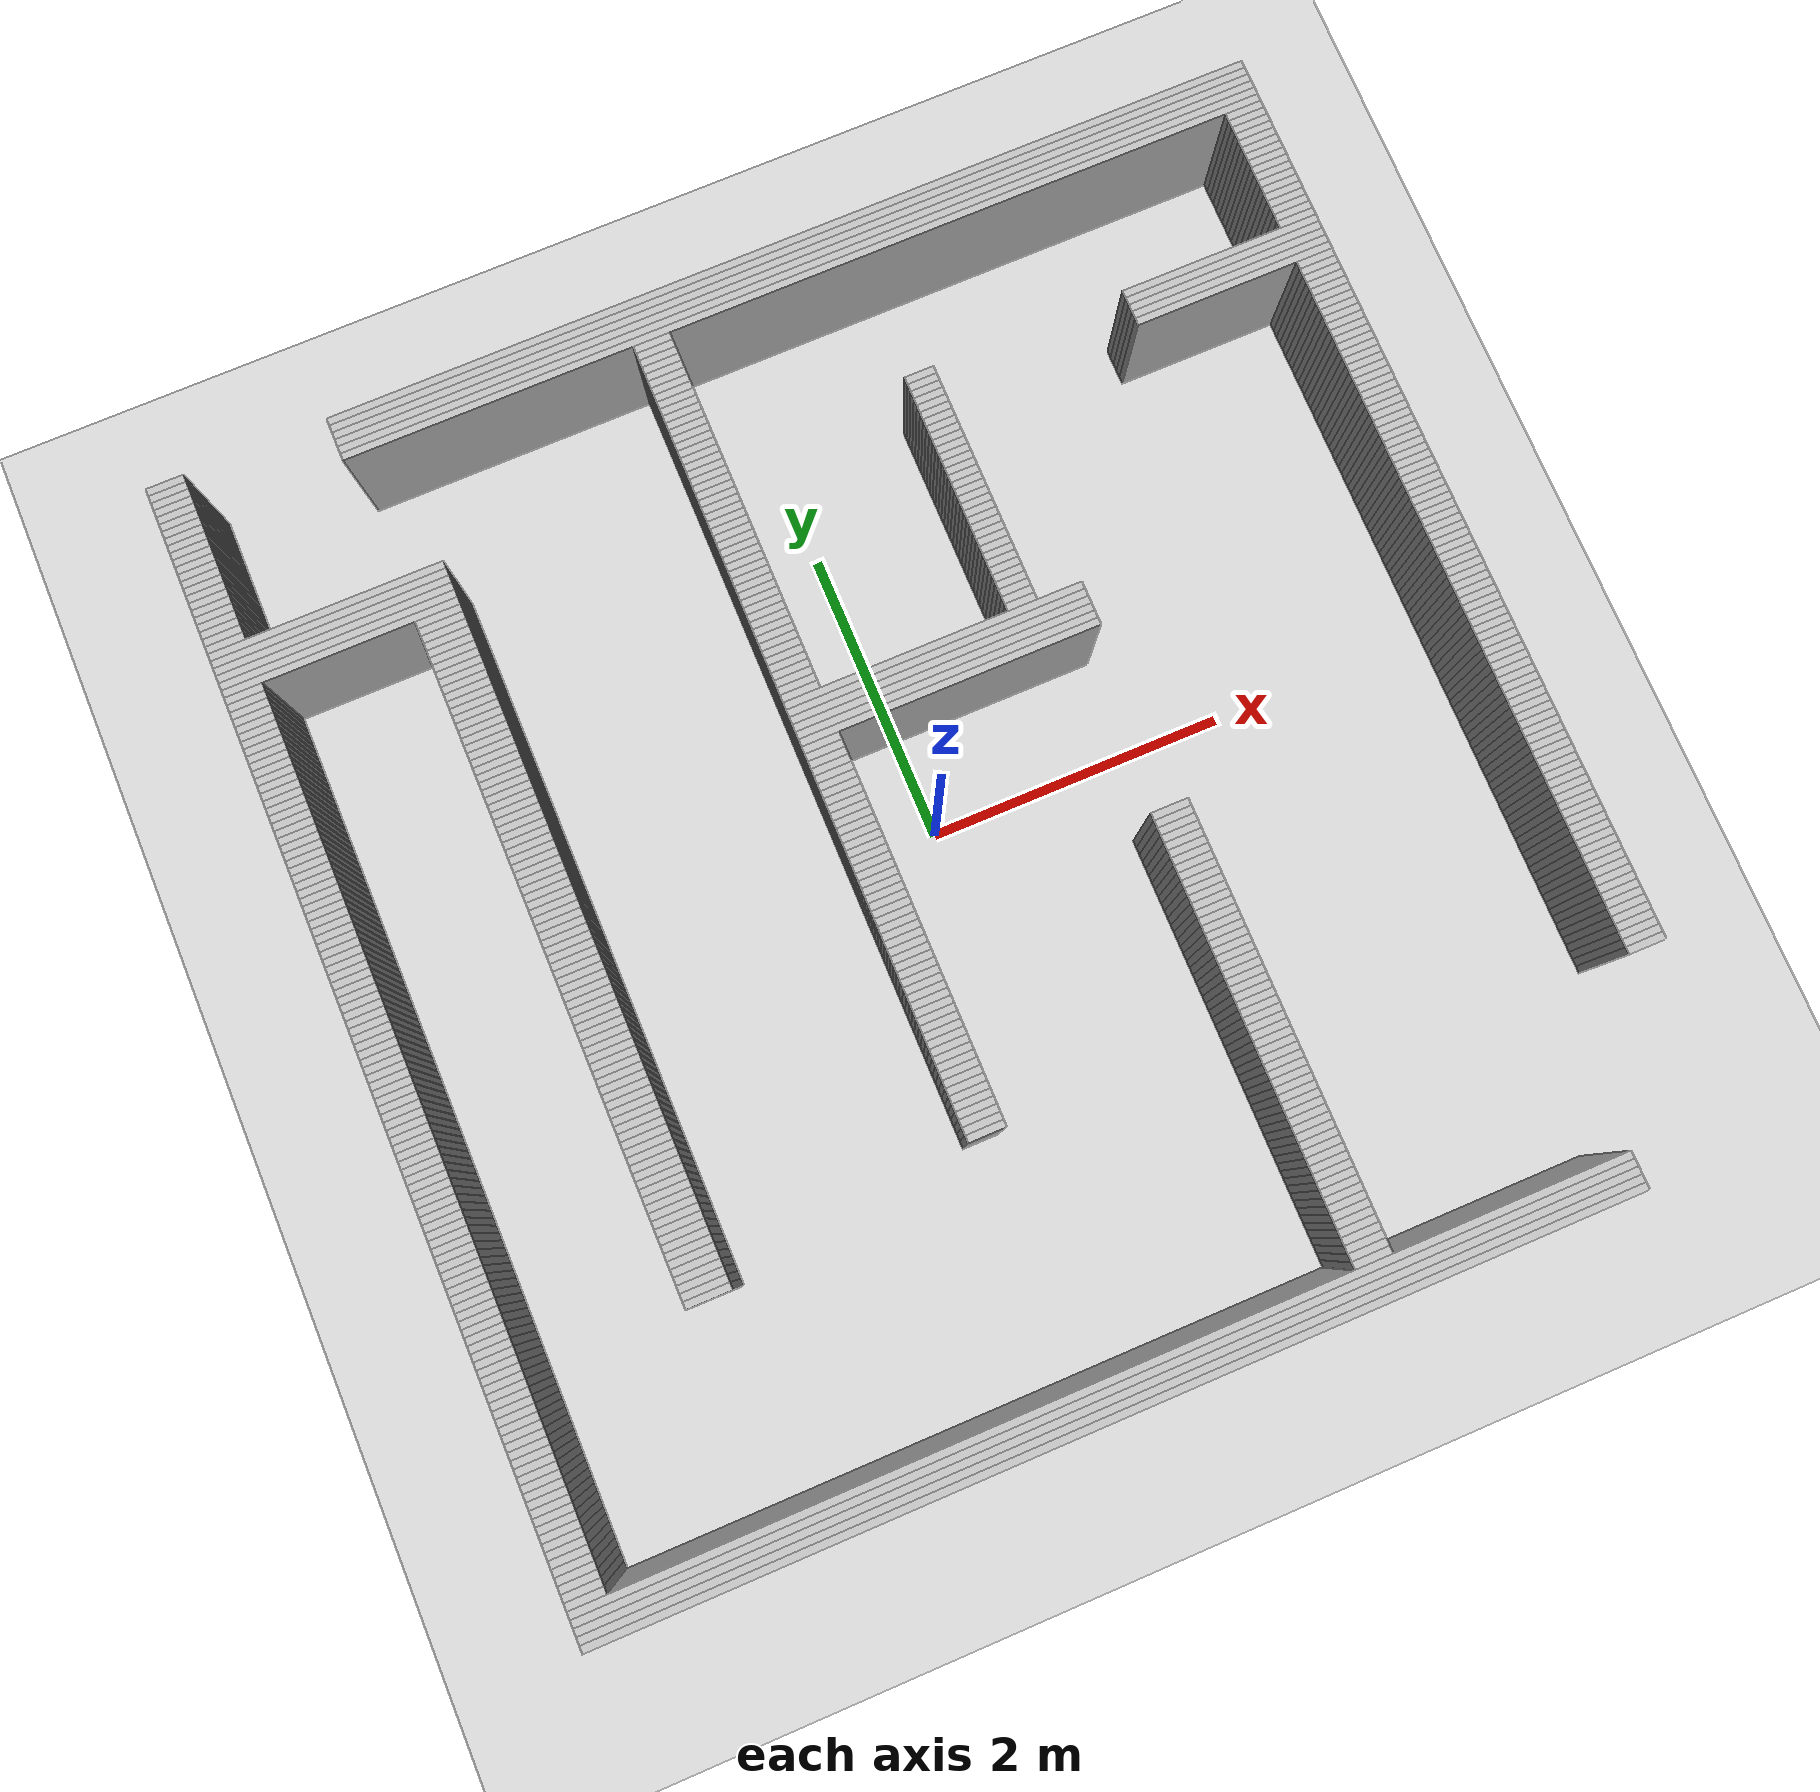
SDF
<?xml version="1.0" ?>
<sdf version="1.6">
  <world name="maze">
    <include>
      <uri>model://ground_plane</uri>
    </include>
    <include>
      <uri>model://sun</uri>
    </include>

    <gui fullscreen='0'>
      <camera name='user_camera'>
        <pose frame=''>0 0 10 0 1.570796 0</pose>
        <view_controller>orbit</view_controller>
        <projection_type>perspective</projection_type>
      </camera>
    </gui>

    <model name="wall_0_0">
      <static>true</static>
      <pose>-3.6500000000000004 3.75 0.5 0 0 0</pose>
      <link name="link">
        <collision name="collision">
          <geometry>
            <box>
              <size>0.25 0.05 1.0</size>
            </box>
          </geometry>
        </collision>
        <visual name="visual">
          <geometry>
            <box>
              <size>0.25 0.05 1.0</size>
            </box>
          </geometry>
        </visual>
      </link>
    </model>

    <model name="wall_24_0">
      <static>true</static>
      <pose>0.5750000000000001 3.75 0.5 0 0 0</pose>
      <link name="link">
        <collision name="collision">
          <geometry>
            <box>
              <size>6.300000000000001 0.05 1.0</size>
            </box>
          </geometry>
        </collision>
        <visual name="visual">
          <geometry>
            <box>
              <size>6.300000000000001 0.05 1.0</size>
            </box>
          </geometry>
        </visual>
      </link>
    </model>

    <model name="wall_0_1">
      <static>true</static>
      <pose>-3.6500000000000004 3.7 0.5 0 0 0</pose>
      <link name="link">
        <collision name="collision">
          <geometry>
            <box>
              <size>0.25 0.05 1.0</size>
            </box>
          </geometry>
        </collision>
        <visual name="visual">
          <geometry>
            <box>
              <size>0.25 0.05 1.0</size>
            </box>
          </geometry>
        </visual>
      </link>
    </model>

    <model name="wall_24_1">
      <static>true</static>
      <pose>0.5750000000000001 3.7 0.5 0 0 0</pose>
      <link name="link">
        <collision name="collision">
          <geometry>
            <box>
              <size>6.300000000000001 0.05 1.0</size>
            </box>
          </geometry>
        </collision>
        <visual name="visual">
          <geometry>
            <box>
              <size>6.300000000000001 0.05 1.0</size>
            </box>
          </geometry>
        </visual>
      </link>
    </model>

    <model name="wall_0_2">
      <static>true</static>
      <pose>-3.6500000000000004 3.6500000000000004 0.5 0 0 0</pose>
      <link name="link">
        <collision name="collision">
          <geometry>
            <box>
              <size>0.25 0.05 1.0</size>
            </box>
          </geometry>
        </collision>
        <visual name="visual">
          <geometry>
            <box>
              <size>0.25 0.05 1.0</size>
            </box>
          </geometry>
        </visual>
      </link>
    </model>

    <model name="wall_24_2">
      <static>true</static>
      <pose>0.5750000000000001 3.6500000000000004 0.5 0 0 0</pose>
      <link name="link">
        <collision name="collision">
          <geometry>
            <box>
              <size>6.300000000000001 0.05 1.0</size>
            </box>
          </geometry>
        </collision>
        <visual name="visual">
          <geometry>
            <box>
              <size>6.300000000000001 0.05 1.0</size>
            </box>
          </geometry>
        </visual>
      </link>
    </model>

    <model name="wall_0_3">
      <static>true</static>
      <pose>-3.6500000000000004 3.6 0.5 0 0 0</pose>
      <link name="link">
        <collision name="collision">
          <geometry>
            <box>
              <size>0.25 0.05 1.0</size>
            </box>
          </geometry>
        </collision>
        <visual name="visual">
          <geometry>
            <box>
              <size>0.25 0.05 1.0</size>
            </box>
          </geometry>
        </visual>
      </link>
    </model>

    <model name="wall_24_3">
      <static>true</static>
      <pose>0.5750000000000001 3.6 0.5 0 0 0</pose>
      <link name="link">
        <collision name="collision">
          <geometry>
            <box>
              <size>6.300000000000001 0.05 1.0</size>
            </box>
          </geometry>
        </collision>
        <visual name="visual">
          <geometry>
            <box>
              <size>6.300000000000001 0.05 1.0</size>
            </box>
          </geometry>
        </visual>
      </link>
    </model>

    <model name="wall_0_4">
      <static>true</static>
      <pose>-3.6500000000000004 3.5500000000000003 0.5 0 0 0</pose>
      <link name="link">
        <collision name="collision">
          <geometry>
            <box>
              <size>0.25 0.05 1.0</size>
            </box>
          </geometry>
        </collision>
        <visual name="visual">
          <geometry>
            <box>
              <size>0.25 0.05 1.0</size>
            </box>
          </geometry>
        </visual>
      </link>
    </model>

    <model name="wall_24_4">
      <static>true</static>
      <pose>0.5750000000000001 3.5500000000000003 0.5 0 0 0</pose>
      <link name="link">
        <collision name="collision">
          <geometry>
            <box>
              <size>6.300000000000001 0.05 1.0</size>
            </box>
          </geometry>
        </collision>
        <visual name="visual">
          <geometry>
            <box>
              <size>6.300000000000001 0.05 1.0</size>
            </box>
          </geometry>
        </visual>
      </link>
    </model>

    <model name="wall_0_5">
      <static>true</static>
      <pose>-3.6500000000000004 3.5 0.5 0 0 0</pose>
      <link name="link">
        <collision name="collision">
          <geometry>
            <box>
              <size>0.25 0.05 1.0</size>
            </box>
          </geometry>
        </collision>
        <visual name="visual">
          <geometry>
            <box>
              <size>0.25 0.05 1.0</size>
            </box>
          </geometry>
        </visual>
      </link>
    </model>

    <model name="wall_24_5">
      <static>true</static>
      <pose>0.5750000000000001 3.5 0.5 0 0 0</pose>
      <link name="link">
        <collision name="collision">
          <geometry>
            <box>
              <size>6.300000000000001 0.05 1.0</size>
            </box>
          </geometry>
        </collision>
        <visual name="visual">
          <geometry>
            <box>
              <size>6.300000000000001 0.05 1.0</size>
            </box>
          </geometry>
        </visual>
      </link>
    </model>

    <model name="wall_0_6">
      <static>true</static>
      <pose>-3.6500000000000004 3.45 0.5 0 0 0</pose>
      <link name="link">
        <collision name="collision">
          <geometry>
            <box>
              <size>0.25 0.05 1.0</size>
            </box>
          </geometry>
        </collision>
        <visual name="visual">
          <geometry>
            <box>
              <size>0.25 0.05 1.0</size>
            </box>
          </geometry>
        </visual>
      </link>
    </model>

    <model name="wall_63_6">
      <static>true</static>
      <pose>-0.5 3.45 0.5 0 0 0</pose>
      <link name="link">
        <collision name="collision">
          <geometry>
            <box>
              <size>0.25 0.05 1.0</size>
            </box>
          </geometry>
        </collision>
        <visual name="visual">
          <geometry>
            <box>
              <size>0.25 0.05 1.0</size>
            </box>
          </geometry>
        </visual>
      </link>
    </model>

    <model name="wall_145_6">
      <static>true</static>
      <pose>3.6 3.45 0.5 0 0 0</pose>
      <link name="link">
        <collision name="collision">
          <geometry>
            <box>
              <size>0.25 0.05 1.0</size>
            </box>
          </geometry>
        </collision>
        <visual name="visual">
          <geometry>
            <box>
              <size>0.25 0.05 1.0</size>
            </box>
          </geometry>
        </visual>
      </link>
    </model>

    <model name="wall_0_7">
      <static>true</static>
      <pose>-3.6500000000000004 3.4000000000000004 0.5 0 0 0</pose>
      <link name="link">
        <collision name="collision">
          <geometry>
            <box>
              <size>0.25 0.05 1.0</size>
            </box>
          </geometry>
        </collision>
        <visual name="visual">
          <geometry>
            <box>
              <size>0.25 0.05 1.0</size>
            </box>
          </geometry>
        </visual>
      </link>
    </model>

    <model name="wall_63_7">
      <static>true</static>
      <pose>-0.5 3.4000000000000004 0.5 0 0 0</pose>
      <link name="link">
        <collision name="collision">
          <geometry>
            <box>
              <size>0.25 0.05 1.0</size>
            </box>
          </geometry>
        </collision>
        <visual name="visual">
          <geometry>
            <box>
              <size>0.25 0.05 1.0</size>
            </box>
          </geometry>
        </visual>
      </link>
    </model>

    <model name="wall_145_7">
      <static>true</static>
      <pose>3.6 3.4000000000000004 0.5 0 0 0</pose>
      <link name="link">
        <collision name="collision">
          <geometry>
            <box>
              <size>0.25 0.05 1.0</size>
            </box>
          </geometry>
        </collision>
        <visual name="visual">
          <geometry>
            <box>
              <size>0.25 0.05 1.0</size>
            </box>
          </geometry>
        </visual>
      </link>
    </model>

    <model name="wall_0_8">
      <static>true</static>
      <pose>-3.6500000000000004 3.35 0.5 0 0 0</pose>
      <link name="link">
        <collision name="collision">
          <geometry>
            <box>
              <size>0.25 0.05 1.0</size>
            </box>
          </geometry>
        </collision>
        <visual name="visual">
          <geometry>
            <box>
              <size>0.25 0.05 1.0</size>
            </box>
          </geometry>
        </visual>
      </link>
    </model>

    <model name="wall_63_8">
      <static>true</static>
      <pose>-0.5 3.35 0.5 0 0 0</pose>
      <link name="link">
        <collision name="collision">
          <geometry>
            <box>
              <size>0.25 0.05 1.0</size>
            </box>
          </geometry>
        </collision>
        <visual name="visual">
          <geometry>
            <box>
              <size>0.25 0.05 1.0</size>
            </box>
          </geometry>
        </visual>
      </link>
    </model>

    <model name="wall_145_8">
      <static>true</static>
      <pose>3.6 3.35 0.5 0 0 0</pose>
      <link name="link">
        <collision name="collision">
          <geometry>
            <box>
              <size>0.25 0.05 1.0</size>
            </box>
          </geometry>
        </collision>
        <visual name="visual">
          <geometry>
            <box>
              <size>0.25 0.05 1.0</size>
            </box>
          </geometry>
        </visual>
      </link>
    </model>

    <model name="wall_0_9">
      <static>true</static>
      <pose>-3.6500000000000004 3.3000000000000003 0.5 0 0 0</pose>
      <link name="link">
        <collision name="collision">
          <geometry>
            <box>
              <size>0.25 0.05 1.0</size>
            </box>
          </geometry>
        </collision>
        <visual name="visual">
          <geometry>
            <box>
              <size>0.25 0.05 1.0</size>
            </box>
          </geometry>
        </visual>
      </link>
    </model>

    <model name="wall_63_9">
      <static>true</static>
      <pose>-0.5 3.3000000000000003 0.5 0 0 0</pose>
      <link name="link">
        <collision name="collision">
          <geometry>
            <box>
              <size>0.25 0.05 1.0</size>
            </box>
          </geometry>
        </collision>
        <visual name="visual">
          <geometry>
            <box>
              <size>0.25 0.05 1.0</size>
            </box>
          </geometry>
        </visual>
      </link>
    </model>

    <model name="wall_145_9">
      <static>true</static>
      <pose>3.6 3.3000000000000003 0.5 0 0 0</pose>
      <link name="link">
        <collision name="collision">
          <geometry>
            <box>
              <size>0.25 0.05 1.0</size>
            </box>
          </geometry>
        </collision>
        <visual name="visual">
          <geometry>
            <box>
              <size>0.25 0.05 1.0</size>
            </box>
          </geometry>
        </visual>
      </link>
    </model>

    <model name="wall_0_10">
      <static>true</static>
      <pose>-3.6500000000000004 3.25 0.5 0 0 0</pose>
      <link name="link">
        <collision name="collision">
          <geometry>
            <box>
              <size>0.25 0.05 1.0</size>
            </box>
          </geometry>
        </collision>
        <visual name="visual">
          <geometry>
            <box>
              <size>0.25 0.05 1.0</size>
            </box>
          </geometry>
        </visual>
      </link>
    </model>

    <model name="wall_63_10">
      <static>true</static>
      <pose>-0.5 3.25 0.5 0 0 0</pose>
      <link name="link">
        <collision name="collision">
          <geometry>
            <box>
              <size>0.25 0.05 1.0</size>
            </box>
          </geometry>
        </collision>
        <visual name="visual">
          <geometry>
            <box>
              <size>0.25 0.05 1.0</size>
            </box>
          </geometry>
        </visual>
      </link>
    </model>

    <model name="wall_145_10">
      <static>true</static>
      <pose>3.6 3.25 0.5 0 0 0</pose>
      <link name="link">
        <collision name="collision">
          <geometry>
            <box>
              <size>0.25 0.05 1.0</size>
            </box>
          </geometry>
        </collision>
        <visual name="visual">
          <geometry>
            <box>
              <size>0.25 0.05 1.0</size>
            </box>
          </geometry>
        </visual>
      </link>
    </model>

    <model name="wall_0_11">
      <static>true</static>
      <pose>-3.6500000000000004 3.2 0.5 0 0 0</pose>
      <link name="link">
        <collision name="collision">
          <geometry>
            <box>
              <size>0.25 0.05 1.0</size>
            </box>
          </geometry>
        </collision>
        <visual name="visual">
          <geometry>
            <box>
              <size>0.25 0.05 1.0</size>
            </box>
          </geometry>
        </visual>
      </link>
    </model>

    <model name="wall_63_11">
      <static>true</static>
      <pose>-0.5 3.2 0.5 0 0 0</pose>
      <link name="link">
        <collision name="collision">
          <geometry>
            <box>
              <size>0.25 0.05 1.0</size>
            </box>
          </geometry>
        </collision>
        <visual name="visual">
          <geometry>
            <box>
              <size>0.25 0.05 1.0</size>
            </box>
          </geometry>
        </visual>
      </link>
    </model>

    <model name="wall_145_11">
      <static>true</static>
      <pose>3.6 3.2 0.5 0 0 0</pose>
      <link name="link">
        <collision name="collision">
          <geometry>
            <box>
              <size>0.25 0.05 1.0</size>
            </box>
          </geometry>
        </collision>
        <visual name="visual">
          <geometry>
            <box>
              <size>0.25 0.05 1.0</size>
            </box>
          </geometry>
        </visual>
      </link>
    </model>

    <model name="wall_0_12">
      <static>true</static>
      <pose>-3.6500000000000004 3.1500000000000004 0.5 0 0 0</pose>
      <link name="link">
        <collision name="collision">
          <geometry>
            <box>
              <size>0.25 0.05 1.0</size>
            </box>
          </geometry>
        </collision>
        <visual name="visual">
          <geometry>
            <box>
              <size>0.25 0.05 1.0</size>
            </box>
          </geometry>
        </visual>
      </link>
    </model>

    <model name="wall_63_12">
      <static>true</static>
      <pose>-0.5 3.1500000000000004 0.5 0 0 0</pose>
      <link name="link">
        <collision name="collision">
          <geometry>
            <box>
              <size>0.25 0.05 1.0</size>
            </box>
          </geometry>
        </collision>
        <visual name="visual">
          <geometry>
            <box>
              <size>0.25 0.05 1.0</size>
            </box>
          </geometry>
        </visual>
      </link>
    </model>

    <model name="wall_145_12">
      <static>true</static>
      <pose>3.6 3.1500000000000004 0.5 0 0 0</pose>
      <link name="link">
        <collision name="collision">
          <geometry>
            <box>
              <size>0.25 0.05 1.0</size>
            </box>
          </geometry>
        </collision>
        <visual name="visual">
          <geometry>
            <box>
              <size>0.25 0.05 1.0</size>
            </box>
          </geometry>
        </visual>
      </link>
    </model>

    <model name="wall_0_13">
      <static>true</static>
      <pose>-3.6500000000000004 3.1 0.5 0 0 0</pose>
      <link name="link">
        <collision name="collision">
          <geometry>
            <box>
              <size>0.25 0.05 1.0</size>
            </box>
          </geometry>
        </collision>
        <visual name="visual">
          <geometry>
            <box>
              <size>0.25 0.05 1.0</size>
            </box>
          </geometry>
        </visual>
      </link>
    </model>

    <model name="wall_63_13">
      <static>true</static>
      <pose>-0.5 3.1 0.5 0 0 0</pose>
      <link name="link">
        <collision name="collision">
          <geometry>
            <box>
              <size>0.25 0.05 1.0</size>
            </box>
          </geometry>
        </collision>
        <visual name="visual">
          <geometry>
            <box>
              <size>0.25 0.05 1.0</size>
            </box>
          </geometry>
        </visual>
      </link>
    </model>

    <model name="wall_145_13">
      <static>true</static>
      <pose>3.6 3.1 0.5 0 0 0</pose>
      <link name="link">
        <collision name="collision">
          <geometry>
            <box>
              <size>0.25 0.05 1.0</size>
            </box>
          </geometry>
        </collision>
        <visual name="visual">
          <geometry>
            <box>
              <size>0.25 0.05 1.0</size>
            </box>
          </geometry>
        </visual>
      </link>
    </model>

    <model name="wall_0_14">
      <static>true</static>
      <pose>-3.6500000000000004 3.0500000000000003 0.5 0 0 0</pose>
      <link name="link">
        <collision name="collision">
          <geometry>
            <box>
              <size>0.25 0.05 1.0</size>
            </box>
          </geometry>
        </collision>
        <visual name="visual">
          <geometry>
            <box>
              <size>0.25 0.05 1.0</size>
            </box>
          </geometry>
        </visual>
      </link>
    </model>

    <model name="wall_63_14">
      <static>true</static>
      <pose>-0.5 3.0500000000000003 0.5 0 0 0</pose>
      <link name="link">
        <collision name="collision">
          <geometry>
            <box>
              <size>0.25 0.05 1.0</size>
            </box>
          </geometry>
        </collision>
        <visual name="visual">
          <geometry>
            <box>
              <size>0.25 0.05 1.0</size>
            </box>
          </geometry>
        </visual>
      </link>
    </model>

    <model name="wall_145_14">
      <static>true</static>
      <pose>3.6 3.0500000000000003 0.5 0 0 0</pose>
      <link name="link">
        <collision name="collision">
          <geometry>
            <box>
              <size>0.25 0.05 1.0</size>
            </box>
          </geometry>
        </collision>
        <visual name="visual">
          <geometry>
            <box>
              <size>0.25 0.05 1.0</size>
            </box>
          </geometry>
        </visual>
      </link>
    </model>

    <model name="wall_0_15">
      <static>true</static>
      <pose>-3.6500000000000004 3.0 0.5 0 0 0</pose>
      <link name="link">
        <collision name="collision">
          <geometry>
            <box>
              <size>0.25 0.05 1.0</size>
            </box>
          </geometry>
        </collision>
        <visual name="visual">
          <geometry>
            <box>
              <size>0.25 0.05 1.0</size>
            </box>
          </geometry>
        </visual>
      </link>
    </model>

    <model name="wall_63_15">
      <static>true</static>
      <pose>-0.5 3.0 0.5 0 0 0</pose>
      <link name="link">
        <collision name="collision">
          <geometry>
            <box>
              <size>0.25 0.05 1.0</size>
            </box>
          </geometry>
        </collision>
        <visual name="visual">
          <geometry>
            <box>
              <size>0.25 0.05 1.0</size>
            </box>
          </geometry>
        </visual>
      </link>
    </model>

    <model name="wall_145_15">
      <static>true</static>
      <pose>3.6 3.0 0.5 0 0 0</pose>
      <link name="link">
        <collision name="collision">
          <geometry>
            <box>
              <size>0.25 0.05 1.0</size>
            </box>
          </geometry>
        </collision>
        <visual name="visual">
          <geometry>
            <box>
              <size>0.25 0.05 1.0</size>
            </box>
          </geometry>
        </visual>
      </link>
    </model>

    <model name="wall_0_16">
      <static>true</static>
      <pose>-3.6500000000000004 2.95 0.5 0 0 0</pose>
      <link name="link">
        <collision name="collision">
          <geometry>
            <box>
              <size>0.25 0.05 1.0</size>
            </box>
          </geometry>
        </collision>
        <visual name="visual">
          <geometry>
            <box>
              <size>0.25 0.05 1.0</size>
            </box>
          </geometry>
        </visual>
      </link>
    </model>

    <model name="wall_63_16">
      <static>true</static>
      <pose>-0.5 2.95 0.5 0 0 0</pose>
      <link name="link">
        <collision name="collision">
          <geometry>
            <box>
              <size>0.25 0.05 1.0</size>
            </box>
          </geometry>
        </collision>
        <visual name="visual">
          <geometry>
            <box>
              <size>0.25 0.05 1.0</size>
            </box>
          </geometry>
        </visual>
      </link>
    </model>

    <model name="wall_145_16">
      <static>true</static>
      <pose>3.6 2.95 0.5 0 0 0</pose>
      <link name="link">
        <collision name="collision">
          <geometry>
            <box>
              <size>0.25 0.05 1.0</size>
            </box>
          </geometry>
        </collision>
        <visual name="visual">
          <geometry>
            <box>
              <size>0.25 0.05 1.0</size>
            </box>
          </geometry>
        </visual>
      </link>
    </model>

    <model name="wall_0_17">
      <static>true</static>
      <pose>-3.6500000000000004 2.9000000000000004 0.5 0 0 0</pose>
      <link name="link">
        <collision name="collision">
          <geometry>
            <box>
              <size>0.25 0.05 1.0</size>
            </box>
          </geometry>
        </collision>
        <visual name="visual">
          <geometry>
            <box>
              <size>0.25 0.05 1.0</size>
            </box>
          </geometry>
        </visual>
      </link>
    </model>

    <model name="wall_63_17">
      <static>true</static>
      <pose>-0.5 2.9000000000000004 0.5 0 0 0</pose>
      <link name="link">
        <collision name="collision">
          <geometry>
            <box>
              <size>0.25 0.05 1.0</size>
            </box>
          </geometry>
        </collision>
        <visual name="visual">
          <geometry>
            <box>
              <size>0.25 0.05 1.0</size>
            </box>
          </geometry>
        </visual>
      </link>
    </model>

    <model name="wall_145_17">
      <static>true</static>
      <pose>3.6 2.9000000000000004 0.5 0 0 0</pose>
      <link name="link">
        <collision name="collision">
          <geometry>
            <box>
              <size>0.25 0.05 1.0</size>
            </box>
          </geometry>
        </collision>
        <visual name="visual">
          <geometry>
            <box>
              <size>0.25 0.05 1.0</size>
            </box>
          </geometry>
        </visual>
      </link>
    </model>

    <model name="wall_0_18">
      <static>true</static>
      <pose>-3.6500000000000004 2.85 0.5 0 0 0</pose>
      <link name="link">
        <collision name="collision">
          <geometry>
            <box>
              <size>0.25 0.05 1.0</size>
            </box>
          </geometry>
        </collision>
        <visual name="visual">
          <geometry>
            <box>
              <size>0.25 0.05 1.0</size>
            </box>
          </geometry>
        </visual>
      </link>
    </model>

    <model name="wall_63_18">
      <static>true</static>
      <pose>-0.5 2.85 0.5 0 0 0</pose>
      <link name="link">
        <collision name="collision">
          <geometry>
            <box>
              <size>0.25 0.05 1.0</size>
            </box>
          </geometry>
        </collision>
        <visual name="visual">
          <geometry>
            <box>
              <size>0.25 0.05 1.0</size>
            </box>
          </geometry>
        </visual>
      </link>
    </model>

    <model name="wall_145_18">
      <static>true</static>
      <pose>3.6 2.85 0.5 0 0 0</pose>
      <link name="link">
        <collision name="collision">
          <geometry>
            <box>
              <size>0.25 0.05 1.0</size>
            </box>
          </geometry>
        </collision>
        <visual name="visual">
          <geometry>
            <box>
              <size>0.25 0.05 1.0</size>
            </box>
          </geometry>
        </visual>
      </link>
    </model>

    <model name="wall_0_19">
      <static>true</static>
      <pose>-3.6500000000000004 2.8000000000000003 0.5 0 0 0</pose>
      <link name="link">
        <collision name="collision">
          <geometry>
            <box>
              <size>0.25 0.05 1.0</size>
            </box>
          </geometry>
        </collision>
        <visual name="visual">
          <geometry>
            <box>
              <size>0.25 0.05 1.0</size>
            </box>
          </geometry>
        </visual>
      </link>
    </model>

    <model name="wall_63_19">
      <static>true</static>
      <pose>-0.5 2.8000000000000003 0.5 0 0 0</pose>
      <link name="link">
        <collision name="collision">
          <geometry>
            <box>
              <size>0.25 0.05 1.0</size>
            </box>
          </geometry>
        </collision>
        <visual name="visual">
          <geometry>
            <box>
              <size>0.25 0.05 1.0</size>
            </box>
          </geometry>
        </visual>
      </link>
    </model>

    <model name="wall_145_19">
      <static>true</static>
      <pose>3.6 2.8000000000000003 0.5 0 0 0</pose>
      <link name="link">
        <collision name="collision">
          <geometry>
            <box>
              <size>0.25 0.05 1.0</size>
            </box>
          </geometry>
        </collision>
        <visual name="visual">
          <geometry>
            <box>
              <size>0.25 0.05 1.0</size>
            </box>
          </geometry>
        </visual>
      </link>
    </model>

    <model name="wall_0_20">
      <static>true</static>
      <pose>-3.6500000000000004 2.75 0.5 0 0 0</pose>
      <link name="link">
        <collision name="collision">
          <geometry>
            <box>
              <size>0.25 0.05 1.0</size>
            </box>
          </geometry>
        </collision>
        <visual name="visual">
          <geometry>
            <box>
              <size>0.25 0.05 1.0</size>
            </box>
          </geometry>
        </visual>
      </link>
    </model>

    <model name="wall_63_20">
      <static>true</static>
      <pose>-0.5 2.75 0.5 0 0 0</pose>
      <link name="link">
        <collision name="collision">
          <geometry>
            <box>
              <size>0.25 0.05 1.0</size>
            </box>
          </geometry>
        </collision>
        <visual name="visual">
          <geometry>
            <box>
              <size>0.25 0.05 1.0</size>
            </box>
          </geometry>
        </visual>
      </link>
    </model>

    <model name="wall_145_20">
      <static>true</static>
      <pose>3.6 2.75 0.5 0 0 0</pose>
      <link name="link">
        <collision name="collision">
          <geometry>
            <box>
              <size>0.25 0.05 1.0</size>
            </box>
          </geometry>
        </collision>
        <visual name="visual">
          <geometry>
            <box>
              <size>0.25 0.05 1.0</size>
            </box>
          </geometry>
        </visual>
      </link>
    </model>

    <model name="wall_0_21">
      <static>true</static>
      <pose>-3.6500000000000004 2.7 0.5 0 0 0</pose>
      <link name="link">
        <collision name="collision">
          <geometry>
            <box>
              <size>0.25 0.05 1.0</size>
            </box>
          </geometry>
        </collision>
        <visual name="visual">
          <geometry>
            <box>
              <size>0.25 0.05 1.0</size>
            </box>
          </geometry>
        </visual>
      </link>
    </model>

    <model name="wall_63_21">
      <static>true</static>
      <pose>-0.5 2.7 0.5 0 0 0</pose>
      <link name="link">
        <collision name="collision">
          <geometry>
            <box>
              <size>0.25 0.05 1.0</size>
            </box>
          </geometry>
        </collision>
        <visual name="visual">
          <geometry>
            <box>
              <size>0.25 0.05 1.0</size>
            </box>
          </geometry>
        </visual>
      </link>
    </model>

    <model name="wall_145_21">
      <static>true</static>
      <pose>3.6 2.7 0.5 0 0 0</pose>
      <link name="link">
        <collision name="collision">
          <geometry>
            <box>
              <size>0.25 0.05 1.0</size>
            </box>
          </geometry>
        </collision>
        <visual name="visual">
          <geometry>
            <box>
              <size>0.25 0.05 1.0</size>
            </box>
          </geometry>
        </visual>
      </link>
    </model>

    <model name="wall_0_22">
      <static>true</static>
      <pose>-3.6500000000000004 2.6500000000000004 0.5 0 0 0</pose>
      <link name="link">
        <collision name="collision">
          <geometry>
            <box>
              <size>0.25 0.05 1.0</size>
            </box>
          </geometry>
        </collision>
        <visual name="visual">
          <geometry>
            <box>
              <size>0.25 0.05 1.0</size>
            </box>
          </geometry>
        </visual>
      </link>
    </model>

    <model name="wall_63_22">
      <static>true</static>
      <pose>-0.5 2.6500000000000004 0.5 0 0 0</pose>
      <link name="link">
        <collision name="collision">
          <geometry>
            <box>
              <size>0.25 0.05 1.0</size>
            </box>
          </geometry>
        </collision>
        <visual name="visual">
          <geometry>
            <box>
              <size>0.25 0.05 1.0</size>
            </box>
          </geometry>
        </visual>
      </link>
    </model>

    <model name="wall_145_22">
      <static>true</static>
      <pose>3.6 2.6500000000000004 0.5 0 0 0</pose>
      <link name="link">
        <collision name="collision">
          <geometry>
            <box>
              <size>0.25 0.05 1.0</size>
            </box>
          </geometry>
        </collision>
        <visual name="visual">
          <geometry>
            <box>
              <size>0.25 0.05 1.0</size>
            </box>
          </geometry>
        </visual>
      </link>
    </model>

    <model name="wall_0_23">
      <static>true</static>
      <pose>-3.0 2.6 0.5 0 0 0</pose>
      <link name="link">
        <collision name="collision">
          <geometry>
            <box>
              <size>1.55 0.05 1.0</size>
            </box>
          </geometry>
        </collision>
        <visual name="visual">
          <geometry>
            <box>
              <size>1.55 0.05 1.0</size>
            </box>
          </geometry>
        </visual>
      </link>
    </model>

    <model name="wall_63_23">
      <static>true</static>
      <pose>-0.5 2.6 0.5 0 0 0</pose>
      <link name="link">
        <collision name="collision">
          <geometry>
            <box>
              <size>0.25 0.05 1.0</size>
            </box>
          </geometry>
        </collision>
        <visual name="visual">
          <geometry>
            <box>
              <size>0.25 0.05 1.0</size>
            </box>
          </geometry>
        </visual>
      </link>
    </model>

    <model name="wall_93_23">
      <static>true</static>
      <pose>0.9750000000000001 2.6 0.5 0 0 0</pose>
      <link name="link">
        <collision name="collision">
          <geometry>
            <box>
              <size>0.2 0.05 1.0</size>
            </box>
          </geometry>
        </collision>
        <visual name="visual">
          <geometry>
            <box>
              <size>0.2 0.05 1.0</size>
            </box>
          </geometry>
        </visual>
      </link>
    </model>

    <model name="wall_123_23">
      <static>true</static>
      <pose>3.0500000000000003 2.6 0.5 0 0 0</pose>
      <link name="link">
        <collision name="collision">
          <geometry>
            <box>
              <size>1.35 0.05 1.0</size>
            </box>
          </geometry>
        </collision>
        <visual name="visual">
          <geometry>
            <box>
              <size>1.35 0.05 1.0</size>
            </box>
          </geometry>
        </visual>
      </link>
    </model>

    <model name="wall_0_24">
      <static>true</static>
      <pose>-3.0 2.5500000000000003 0.5 0 0 0</pose>
      <link name="link">
        <collision name="collision">
          <geometry>
            <box>
              <size>1.55 0.05 1.0</size>
            </box>
          </geometry>
        </collision>
        <visual name="visual">
          <geometry>
            <box>
              <size>1.55 0.05 1.0</size>
            </box>
          </geometry>
        </visual>
      </link>
    </model>

    <model name="wall_63_24">
      <static>true</static>
      <pose>-0.5 2.5500000000000003 0.5 0 0 0</pose>
      <link name="link">
        <collision name="collision">
          <geometry>
            <box>
              <size>0.25 0.05 1.0</size>
            </box>
          </geometry>
        </collision>
        <visual name="visual">
          <geometry>
            <box>
              <size>0.25 0.05 1.0</size>
            </box>
          </geometry>
        </visual>
      </link>
    </model>

    <model name="wall_93_24">
      <static>true</static>
      <pose>0.9750000000000001 2.5500000000000003 0.5 0 0 0</pose>
      <link name="link">
        <collision name="collision">
          <geometry>
            <box>
              <size>0.2 0.05 1.0</size>
            </box>
          </geometry>
        </collision>
        <visual name="visual">
          <geometry>
            <box>
              <size>0.2 0.05 1.0</size>
            </box>
          </geometry>
        </visual>
      </link>
    </model>

    <model name="wall_123_24">
      <static>true</static>
      <pose>3.0500000000000003 2.5500000000000003 0.5 0 0 0</pose>
      <link name="link">
        <collision name="collision">
          <geometry>
            <box>
              <size>1.35 0.05 1.0</size>
            </box>
          </geometry>
        </collision>
        <visual name="visual">
          <geometry>
            <box>
              <size>1.35 0.05 1.0</size>
            </box>
          </geometry>
        </visual>
      </link>
    </model>

    <model name="wall_0_25">
      <static>true</static>
      <pose>-3.0 2.5 0.5 0 0 0</pose>
      <link name="link">
        <collision name="collision">
          <geometry>
            <box>
              <size>1.55 0.05 1.0</size>
            </box>
          </geometry>
        </collision>
        <visual name="visual">
          <geometry>
            <box>
              <size>1.55 0.05 1.0</size>
            </box>
          </geometry>
        </visual>
      </link>
    </model>

    <model name="wall_63_25">
      <static>true</static>
      <pose>-0.5 2.5 0.5 0 0 0</pose>
      <link name="link">
        <collision name="collision">
          <geometry>
            <box>
              <size>0.25 0.05 1.0</size>
            </box>
          </geometry>
        </collision>
        <visual name="visual">
          <geometry>
            <box>
              <size>0.25 0.05 1.0</size>
            </box>
          </geometry>
        </visual>
      </link>
    </model>

    <model name="wall_93_25">
      <static>true</static>
      <pose>0.9750000000000001 2.5 0.5 0 0 0</pose>
      <link name="link">
        <collision name="collision">
          <geometry>
            <box>
              <size>0.2 0.05 1.0</size>
            </box>
          </geometry>
        </collision>
        <visual name="visual">
          <geometry>
            <box>
              <size>0.2 0.05 1.0</size>
            </box>
          </geometry>
        </visual>
      </link>
    </model>

    <model name="wall_123_25">
      <static>true</static>
      <pose>3.0500000000000003 2.5 0.5 0 0 0</pose>
      <link name="link">
        <collision name="collision">
          <geometry>
            <box>
              <size>1.35 0.05 1.0</size>
            </box>
          </geometry>
        </collision>
        <visual name="visual">
          <geometry>
            <box>
              <size>1.35 0.05 1.0</size>
            </box>
          </geometry>
        </visual>
      </link>
    </model>

    <model name="wall_0_26">
      <static>true</static>
      <pose>-3.0 2.45 0.5 0 0 0</pose>
      <link name="link">
        <collision name="collision">
          <geometry>
            <box>
              <size>1.55 0.05 1.0</size>
            </box>
          </geometry>
        </collision>
        <visual name="visual">
          <geometry>
            <box>
              <size>1.55 0.05 1.0</size>
            </box>
          </geometry>
        </visual>
      </link>
    </model>

    <model name="wall_63_26">
      <static>true</static>
      <pose>-0.5 2.45 0.5 0 0 0</pose>
      <link name="link">
        <collision name="collision">
          <geometry>
            <box>
              <size>0.25 0.05 1.0</size>
            </box>
          </geometry>
        </collision>
        <visual name="visual">
          <geometry>
            <box>
              <size>0.25 0.05 1.0</size>
            </box>
          </geometry>
        </visual>
      </link>
    </model>

    <model name="wall_93_26">
      <static>true</static>
      <pose>0.9750000000000001 2.45 0.5 0 0 0</pose>
      <link name="link">
        <collision name="collision">
          <geometry>
            <box>
              <size>0.2 0.05 1.0</size>
            </box>
          </geometry>
        </collision>
        <visual name="visual">
          <geometry>
            <box>
              <size>0.2 0.05 1.0</size>
            </box>
          </geometry>
        </visual>
      </link>
    </model>

    <model name="wall_123_26">
      <static>true</static>
      <pose>3.0500000000000003 2.45 0.5 0 0 0</pose>
      <link name="link">
        <collision name="collision">
          <geometry>
            <box>
              <size>1.35 0.05 1.0</size>
            </box>
          </geometry>
        </collision>
        <visual name="visual">
          <geometry>
            <box>
              <size>1.35 0.05 1.0</size>
            </box>
          </geometry>
        </visual>
      </link>
    </model>

    <model name="wall_0_27">
      <static>true</static>
      <pose>-3.0 2.4000000000000004 0.5 0 0 0</pose>
      <link name="link">
        <collision name="collision">
          <geometry>
            <box>
              <size>1.55 0.05 1.0</size>
            </box>
          </geometry>
        </collision>
        <visual name="visual">
          <geometry>
            <box>
              <size>1.55 0.05 1.0</size>
            </box>
          </geometry>
        </visual>
      </link>
    </model>

    <model name="wall_63_27">
      <static>true</static>
      <pose>-0.5 2.4000000000000004 0.5 0 0 0</pose>
      <link name="link">
        <collision name="collision">
          <geometry>
            <box>
              <size>0.25 0.05 1.0</size>
            </box>
          </geometry>
        </collision>
        <visual name="visual">
          <geometry>
            <box>
              <size>0.25 0.05 1.0</size>
            </box>
          </geometry>
        </visual>
      </link>
    </model>

    <model name="wall_93_27">
      <static>true</static>
      <pose>0.9750000000000001 2.4000000000000004 0.5 0 0 0</pose>
      <link name="link">
        <collision name="collision">
          <geometry>
            <box>
              <size>0.2 0.05 1.0</size>
            </box>
          </geometry>
        </collision>
        <visual name="visual">
          <geometry>
            <box>
              <size>0.2 0.05 1.0</size>
            </box>
          </geometry>
        </visual>
      </link>
    </model>

    <model name="wall_123_27">
      <static>true</static>
      <pose>3.0500000000000003 2.4000000000000004 0.5 0 0 0</pose>
      <link name="link">
        <collision name="collision">
          <geometry>
            <box>
              <size>1.35 0.05 1.0</size>
            </box>
          </geometry>
        </collision>
        <visual name="visual">
          <geometry>
            <box>
              <size>1.35 0.05 1.0</size>
            </box>
          </geometry>
        </visual>
      </link>
    </model>

    <model name="wall_0_28">
      <static>true</static>
      <pose>-3.0 2.35 0.5 0 0 0</pose>
      <link name="link">
        <collision name="collision">
          <geometry>
            <box>
              <size>1.55 0.05 1.0</size>
            </box>
          </geometry>
        </collision>
        <visual name="visual">
          <geometry>
            <box>
              <size>1.55 0.05 1.0</size>
            </box>
          </geometry>
        </visual>
      </link>
    </model>

    <model name="wall_63_28">
      <static>true</static>
      <pose>-0.5 2.35 0.5 0 0 0</pose>
      <link name="link">
        <collision name="collision">
          <geometry>
            <box>
              <size>0.25 0.05 1.0</size>
            </box>
          </geometry>
        </collision>
        <visual name="visual">
          <geometry>
            <box>
              <size>0.25 0.05 1.0</size>
            </box>
          </geometry>
        </visual>
      </link>
    </model>

    <model name="wall_93_28">
      <static>true</static>
      <pose>0.9750000000000001 2.35 0.5 0 0 0</pose>
      <link name="link">
        <collision name="collision">
          <geometry>
            <box>
              <size>0.2 0.05 1.0</size>
            </box>
          </geometry>
        </collision>
        <visual name="visual">
          <geometry>
            <box>
              <size>0.2 0.05 1.0</size>
            </box>
          </geometry>
        </visual>
      </link>
    </model>

    <model name="wall_145_28">
      <static>true</static>
      <pose>3.6 2.35 0.5 0 0 0</pose>
      <link name="link">
        <collision name="collision">
          <geometry>
            <box>
              <size>0.25 0.05 1.0</size>
            </box>
          </geometry>
        </collision>
        <visual name="visual">
          <geometry>
            <box>
              <size>0.25 0.05 1.0</size>
            </box>
          </geometry>
        </visual>
      </link>
    </model>

    <model name="wall_0_29">
      <static>true</static>
      <pose>-3.6500000000000004 2.3000000000000003 0.5 0 0 0</pose>
      <link name="link">
        <collision name="collision">
          <geometry>
            <box>
              <size>0.25 0.05 1.0</size>
            </box>
          </geometry>
        </collision>
        <visual name="visual">
          <geometry>
            <box>
              <size>0.25 0.05 1.0</size>
            </box>
          </geometry>
        </visual>
      </link>
    </model>

    <model name="wall_25_29">
      <static>true</static>
      <pose>-2.375 2.3000000000000003 0.5 0 0 0</pose>
      <link name="link">
        <collision name="collision">
          <geometry>
            <box>
              <size>0.30000000000000004 0.05 1.0</size>
            </box>
          </geometry>
        </collision>
        <visual name="visual">
          <geometry>
            <box>
              <size>0.30000000000000004 0.05 1.0</size>
            </box>
          </geometry>
        </visual>
      </link>
    </model>

    <model name="wall_63_29">
      <static>true</static>
      <pose>-0.5 2.3000000000000003 0.5 0 0 0</pose>
      <link name="link">
        <collision name="collision">
          <geometry>
            <box>
              <size>0.25 0.05 1.0</size>
            </box>
          </geometry>
        </collision>
        <visual name="visual">
          <geometry>
            <box>
              <size>0.25 0.05 1.0</size>
            </box>
          </geometry>
        </visual>
      </link>
    </model>

    <model name="wall_93_29">
      <static>true</static>
      <pose>0.9750000000000001 2.3000000000000003 0.5 0 0 0</pose>
      <link name="link">
        <collision name="collision">
          <geometry>
            <box>
              <size>0.2 0.05 1.0</size>
            </box>
          </geometry>
        </collision>
        <visual name="visual">
          <geometry>
            <box>
              <size>0.2 0.05 1.0</size>
            </box>
          </geometry>
        </visual>
      </link>
    </model>

    <model name="wall_145_29">
      <static>true</static>
      <pose>3.6 2.3000000000000003 0.5 0 0 0</pose>
      <link name="link">
        <collision name="collision">
          <geometry>
            <box>
              <size>0.25 0.05 1.0</size>
            </box>
          </geometry>
        </collision>
        <visual name="visual">
          <geometry>
            <box>
              <size>0.25 0.05 1.0</size>
            </box>
          </geometry>
        </visual>
      </link>
    </model>

    <model name="wall_0_30">
      <static>true</static>
      <pose>-3.6500000000000004 2.25 0.5 0 0 0</pose>
      <link name="link">
        <collision name="collision">
          <geometry>
            <box>
              <size>0.25 0.05 1.0</size>
            </box>
          </geometry>
        </collision>
        <visual name="visual">
          <geometry>
            <box>
              <size>0.25 0.05 1.0</size>
            </box>
          </geometry>
        </visual>
      </link>
    </model>

    <model name="wall_25_30">
      <static>true</static>
      <pose>-2.375 2.25 0.5 0 0 0</pose>
      <link name="link">
        <collision name="collision">
          <geometry>
            <box>
              <size>0.30000000000000004 0.05 1.0</size>
            </box>
          </geometry>
        </collision>
        <visual name="visual">
          <geometry>
            <box>
              <size>0.30000000000000004 0.05 1.0</size>
            </box>
          </geometry>
        </visual>
      </link>
    </model>

    <model name="wall_63_30">
      <static>true</static>
      <pose>-0.5 2.25 0.5 0 0 0</pose>
      <link name="link">
        <collision name="collision">
          <geometry>
            <box>
              <size>0.25 0.05 1.0</size>
            </box>
          </geometry>
        </collision>
        <visual name="visual">
          <geometry>
            <box>
              <size>0.25 0.05 1.0</size>
            </box>
          </geometry>
        </visual>
      </link>
    </model>

    <model name="wall_93_30">
      <static>true</static>
      <pose>0.9750000000000001 2.25 0.5 0 0 0</pose>
      <link name="link">
        <collision name="collision">
          <geometry>
            <box>
              <size>0.2 0.05 1.0</size>
            </box>
          </geometry>
        </collision>
        <visual name="visual">
          <geometry>
            <box>
              <size>0.2 0.05 1.0</size>
            </box>
          </geometry>
        </visual>
      </link>
    </model>

    <model name="wall_145_30">
      <static>true</static>
      <pose>3.6 2.25 0.5 0 0 0</pose>
      <link name="link">
        <collision name="collision">
          <geometry>
            <box>
              <size>0.25 0.05 1.0</size>
            </box>
          </geometry>
        </collision>
        <visual name="visual">
          <geometry>
            <box>
              <size>0.25 0.05 1.0</size>
            </box>
          </geometry>
        </visual>
      </link>
    </model>

    <model name="wall_0_31">
      <static>true</static>
      <pose>-3.6500000000000004 2.2 0.5 0 0 0</pose>
      <link name="link">
        <collision name="collision">
          <geometry>
            <box>
              <size>0.25 0.05 1.0</size>
            </box>
          </geometry>
        </collision>
        <visual name="visual">
          <geometry>
            <box>
              <size>0.25 0.05 1.0</size>
            </box>
          </geometry>
        </visual>
      </link>
    </model>

    <model name="wall_25_31">
      <static>true</static>
      <pose>-2.375 2.2 0.5 0 0 0</pose>
      <link name="link">
        <collision name="collision">
          <geometry>
            <box>
              <size>0.30000000000000004 0.05 1.0</size>
            </box>
          </geometry>
        </collision>
        <visual name="visual">
          <geometry>
            <box>
              <size>0.30000000000000004 0.05 1.0</size>
            </box>
          </geometry>
        </visual>
      </link>
    </model>

    <model name="wall_63_31">
      <static>true</static>
      <pose>-0.5 2.2 0.5 0 0 0</pose>
      <link name="link">
        <collision name="collision">
          <geometry>
            <box>
              <size>0.25 0.05 1.0</size>
            </box>
          </geometry>
        </collision>
        <visual name="visual">
          <geometry>
            <box>
              <size>0.25 0.05 1.0</size>
            </box>
          </geometry>
        </visual>
      </link>
    </model>

    <model name="wall_93_31">
      <static>true</static>
      <pose>0.9750000000000001 2.2 0.5 0 0 0</pose>
      <link name="link">
        <collision name="collision">
          <geometry>
            <box>
              <size>0.2 0.05 1.0</size>
            </box>
          </geometry>
        </collision>
        <visual name="visual">
          <geometry>
            <box>
              <size>0.2 0.05 1.0</size>
            </box>
          </geometry>
        </visual>
      </link>
    </model>

    <model name="wall_145_31">
      <static>true</static>
      <pose>3.6 2.2 0.5 0 0 0</pose>
      <link name="link">
        <collision name="collision">
          <geometry>
            <box>
              <size>0.25 0.05 1.0</size>
            </box>
          </geometry>
        </collision>
        <visual name="visual">
          <geometry>
            <box>
              <size>0.25 0.05 1.0</size>
            </box>
          </geometry>
        </visual>
      </link>
    </model>

    <model name="wall_0_32">
      <static>true</static>
      <pose>-3.6500000000000004 2.15 0.5 0 0 0</pose>
      <link name="link">
        <collision name="collision">
          <geometry>
            <box>
              <size>0.25 0.05 1.0</size>
            </box>
          </geometry>
        </collision>
        <visual name="visual">
          <geometry>
            <box>
              <size>0.25 0.05 1.0</size>
            </box>
          </geometry>
        </visual>
      </link>
    </model>

    <model name="wall_25_32">
      <static>true</static>
      <pose>-2.375 2.15 0.5 0 0 0</pose>
      <link name="link">
        <collision name="collision">
          <geometry>
            <box>
              <size>0.30000000000000004 0.05 1.0</size>
            </box>
          </geometry>
        </collision>
        <visual name="visual">
          <geometry>
            <box>
              <size>0.30000000000000004 0.05 1.0</size>
            </box>
          </geometry>
        </visual>
      </link>
    </model>

    <model name="wall_63_32">
      <static>true</static>
      <pose>-0.5 2.15 0.5 0 0 0</pose>
      <link name="link">
        <collision name="collision">
          <geometry>
            <box>
              <size>0.25 0.05 1.0</size>
            </box>
          </geometry>
        </collision>
        <visual name="visual">
          <geometry>
            <box>
              <size>0.25 0.05 1.0</size>
            </box>
          </geometry>
        </visual>
      </link>
    </model>

    <model name="wall_93_32">
      <static>true</static>
      <pose>0.9750000000000001 2.15 0.5 0 0 0</pose>
      <link name="link">
        <collision name="collision">
          <geometry>
            <box>
              <size>0.2 0.05 1.0</size>
            </box>
          </geometry>
        </collision>
        <visual name="visual">
          <geometry>
            <box>
              <size>0.2 0.05 1.0</size>
            </box>
          </geometry>
        </visual>
      </link>
    </model>

    <model name="wall_145_32">
      <static>true</static>
      <pose>3.6 2.15 0.5 0 0 0</pose>
      <link name="link">
        <collision name="collision">
          <geometry>
            <box>
              <size>0.25 0.05 1.0</size>
            </box>
          </geometry>
        </collision>
        <visual name="visual">
          <geometry>
            <box>
              <size>0.25 0.05 1.0</size>
            </box>
          </geometry>
        </visual>
      </link>
    </model>

    <model name="wall_0_33">
      <static>true</static>
      <pose>-3.6500000000000004 2.1 0.5 0 0 0</pose>
      <link name="link">
        <collision name="collision">
          <geometry>
            <box>
              <size>0.25 0.05 1.0</size>
            </box>
          </geometry>
        </collision>
        <visual name="visual">
          <geometry>
            <box>
              <size>0.25 0.05 1.0</size>
            </box>
          </geometry>
        </visual>
      </link>
    </model>

    <model name="wall_25_33">
      <static>true</static>
      <pose>-2.375 2.1 0.5 0 0 0</pose>
      <link name="link">
        <collision name="collision">
          <geometry>
            <box>
              <size>0.30000000000000004 0.05 1.0</size>
            </box>
          </geometry>
        </collision>
        <visual name="visual">
          <geometry>
            <box>
              <size>0.30000000000000004 0.05 1.0</size>
            </box>
          </geometry>
        </visual>
      </link>
    </model>

    <model name="wall_63_33">
      <static>true</static>
      <pose>-0.5 2.1 0.5 0 0 0</pose>
      <link name="link">
        <collision name="collision">
          <geometry>
            <box>
              <size>0.25 0.05 1.0</size>
            </box>
          </geometry>
        </collision>
        <visual name="visual">
          <geometry>
            <box>
              <size>0.25 0.05 1.0</size>
            </box>
          </geometry>
        </visual>
      </link>
    </model>

    <model name="wall_93_33">
      <static>true</static>
      <pose>0.9750000000000001 2.1 0.5 0 0 0</pose>
      <link name="link">
        <collision name="collision">
          <geometry>
            <box>
              <size>0.2 0.05 1.0</size>
            </box>
          </geometry>
        </collision>
        <visual name="visual">
          <geometry>
            <box>
              <size>0.2 0.05 1.0</size>
            </box>
          </geometry>
        </visual>
      </link>
    </model>

    <model name="wall_145_33">
      <static>true</static>
      <pose>3.6 2.1 0.5 0 0 0</pose>
      <link name="link">
        <collision name="collision">
          <geometry>
            <box>
              <size>0.25 0.05 1.0</size>
            </box>
          </geometry>
        </collision>
        <visual name="visual">
          <geometry>
            <box>
              <size>0.25 0.05 1.0</size>
            </box>
          </geometry>
        </visual>
      </link>
    </model>

    <model name="wall_0_34">
      <static>true</static>
      <pose>-3.6500000000000004 2.0500000000000003 0.5 0 0 0</pose>
      <link name="link">
        <collision name="collision">
          <geometry>
            <box>
              <size>0.25 0.05 1.0</size>
            </box>
          </geometry>
        </collision>
        <visual name="visual">
          <geometry>
            <box>
              <size>0.25 0.05 1.0</size>
            </box>
          </geometry>
        </visual>
      </link>
    </model>

    <model name="wall_25_34">
      <static>true</static>
      <pose>-2.375 2.0500000000000003 0.5 0 0 0</pose>
      <link name="link">
        <collision name="collision">
          <geometry>
            <box>
              <size>0.30000000000000004 0.05 1.0</size>
            </box>
          </geometry>
        </collision>
        <visual name="visual">
          <geometry>
            <box>
              <size>0.30000000000000004 0.05 1.0</size>
            </box>
          </geometry>
        </visual>
      </link>
    </model>

    <model name="wall_63_34">
      <static>true</static>
      <pose>-0.5 2.0500000000000003 0.5 0 0 0</pose>
      <link name="link">
        <collision name="collision">
          <geometry>
            <box>
              <size>0.25 0.05 1.0</size>
            </box>
          </geometry>
        </collision>
        <visual name="visual">
          <geometry>
            <box>
              <size>0.25 0.05 1.0</size>
            </box>
          </geometry>
        </visual>
      </link>
    </model>

    <model name="wall_93_34">
      <static>true</static>
      <pose>0.9750000000000001 2.0500000000000003 0.5 0 0 0</pose>
      <link name="link">
        <collision name="collision">
          <geometry>
            <box>
              <size>0.2 0.05 1.0</size>
            </box>
          </geometry>
        </collision>
        <visual name="visual">
          <geometry>
            <box>
              <size>0.2 0.05 1.0</size>
            </box>
          </geometry>
        </visual>
      </link>
    </model>

    <model name="wall_145_34">
      <static>true</static>
      <pose>3.6 2.0500000000000003 0.5 0 0 0</pose>
      <link name="link">
        <collision name="collision">
          <geometry>
            <box>
              <size>0.25 0.05 1.0</size>
            </box>
          </geometry>
        </collision>
        <visual name="visual">
          <geometry>
            <box>
              <size>0.25 0.05 1.0</size>
            </box>
          </geometry>
        </visual>
      </link>
    </model>

    <model name="wall_0_35">
      <static>true</static>
      <pose>-3.6500000000000004 2.0 0.5 0 0 0</pose>
      <link name="link">
        <collision name="collision">
          <geometry>
            <box>
              <size>0.25 0.05 1.0</size>
            </box>
          </geometry>
        </collision>
        <visual name="visual">
          <geometry>
            <box>
              <size>0.25 0.05 1.0</size>
            </box>
          </geometry>
        </visual>
      </link>
    </model>

    <model name="wall_25_35">
      <static>true</static>
      <pose>-2.375 2.0 0.5 0 0 0</pose>
      <link name="link">
        <collision name="collision">
          <geometry>
            <box>
              <size>0.30000000000000004 0.05 1.0</size>
            </box>
          </geometry>
        </collision>
        <visual name="visual">
          <geometry>
            <box>
              <size>0.30000000000000004 0.05 1.0</size>
            </box>
          </geometry>
        </visual>
      </link>
    </model>

    <model name="wall_63_35">
      <static>true</static>
      <pose>-0.5 2.0 0.5 0 0 0</pose>
      <link name="link">
        <collision name="collision">
          <geometry>
            <box>
              <size>0.25 0.05 1.0</size>
            </box>
          </geometry>
        </collision>
        <visual name="visual">
          <geometry>
            <box>
              <size>0.25 0.05 1.0</size>
            </box>
          </geometry>
        </visual>
      </link>
    </model>

    <model name="wall_93_35">
      <static>true</static>
      <pose>0.9750000000000001 2.0 0.5 0 0 0</pose>
      <link name="link">
        <collision name="collision">
          <geometry>
            <box>
              <size>0.2 0.05 1.0</size>
            </box>
          </geometry>
        </collision>
        <visual name="visual">
          <geometry>
            <box>
              <size>0.2 0.05 1.0</size>
            </box>
          </geometry>
        </visual>
      </link>
    </model>

    <model name="wall_145_35">
      <static>true</static>
      <pose>3.6 2.0 0.5 0 0 0</pose>
      <link name="link">
        <collision name="collision">
          <geometry>
            <box>
              <size>0.25 0.05 1.0</size>
            </box>
          </geometry>
        </collision>
        <visual name="visual">
          <geometry>
            <box>
              <size>0.25 0.05 1.0</size>
            </box>
          </geometry>
        </visual>
      </link>
    </model>

    <model name="wall_0_36">
      <static>true</static>
      <pose>-3.6500000000000004 1.9500000000000002 0.5 0 0 0</pose>
      <link name="link">
        <collision name="collision">
          <geometry>
            <box>
              <size>0.25 0.05 1.0</size>
            </box>
          </geometry>
        </collision>
        <visual name="visual">
          <geometry>
            <box>
              <size>0.25 0.05 1.0</size>
            </box>
          </geometry>
        </visual>
      </link>
    </model>

    <model name="wall_25_36">
      <static>true</static>
      <pose>-2.375 1.9500000000000002 0.5 0 0 0</pose>
      <link name="link">
        <collision name="collision">
          <geometry>
            <box>
              <size>0.30000000000000004 0.05 1.0</size>
            </box>
          </geometry>
        </collision>
        <visual name="visual">
          <geometry>
            <box>
              <size>0.30000000000000004 0.05 1.0</size>
            </box>
          </geometry>
        </visual>
      </link>
    </model>

    <model name="wall_63_36">
      <static>true</static>
      <pose>-0.5 1.9500000000000002 0.5 0 0 0</pose>
      <link name="link">
        <collision name="collision">
          <geometry>
            <box>
              <size>0.25 0.05 1.0</size>
            </box>
          </geometry>
        </collision>
        <visual name="visual">
          <geometry>
            <box>
              <size>0.25 0.05 1.0</size>
            </box>
          </geometry>
        </visual>
      </link>
    </model>

    <model name="wall_93_36">
      <static>true</static>
      <pose>0.9750000000000001 1.9500000000000002 0.5 0 0 0</pose>
      <link name="link">
        <collision name="collision">
          <geometry>
            <box>
              <size>0.2 0.05 1.0</size>
            </box>
          </geometry>
        </collision>
        <visual name="visual">
          <geometry>
            <box>
              <size>0.2 0.05 1.0</size>
            </box>
          </geometry>
        </visual>
      </link>
    </model>

    <model name="wall_145_36">
      <static>true</static>
      <pose>3.6 1.9500000000000002 0.5 0 0 0</pose>
      <link name="link">
        <collision name="collision">
          <geometry>
            <box>
              <size>0.25 0.05 1.0</size>
            </box>
          </geometry>
        </collision>
        <visual name="visual">
          <geometry>
            <box>
              <size>0.25 0.05 1.0</size>
            </box>
          </geometry>
        </visual>
      </link>
    </model>

    <model name="wall_0_37">
      <static>true</static>
      <pose>-3.6500000000000004 1.9000000000000001 0.5 0 0 0</pose>
      <link name="link">
        <collision name="collision">
          <geometry>
            <box>
              <size>0.25 0.05 1.0</size>
            </box>
          </geometry>
        </collision>
        <visual name="visual">
          <geometry>
            <box>
              <size>0.25 0.05 1.0</size>
            </box>
          </geometry>
        </visual>
      </link>
    </model>

    <model name="wall_25_37">
      <static>true</static>
      <pose>-2.375 1.9000000000000001 0.5 0 0 0</pose>
      <link name="link">
        <collision name="collision">
          <geometry>
            <box>
              <size>0.30000000000000004 0.05 1.0</size>
            </box>
          </geometry>
        </collision>
        <visual name="visual">
          <geometry>
            <box>
              <size>0.30000000000000004 0.05 1.0</size>
            </box>
          </geometry>
        </visual>
      </link>
    </model>

    <model name="wall_63_37">
      <static>true</static>
      <pose>-0.5 1.9000000000000001 0.5 0 0 0</pose>
      <link name="link">
        <collision name="collision">
          <geometry>
            <box>
              <size>0.25 0.05 1.0</size>
            </box>
          </geometry>
        </collision>
        <visual name="visual">
          <geometry>
            <box>
              <size>0.25 0.05 1.0</size>
            </box>
          </geometry>
        </visual>
      </link>
    </model>

    <model name="wall_93_37">
      <static>true</static>
      <pose>0.9750000000000001 1.9000000000000001 0.5 0 0 0</pose>
      <link name="link">
        <collision name="collision">
          <geometry>
            <box>
              <size>0.2 0.05 1.0</size>
            </box>
          </geometry>
        </collision>
        <visual name="visual">
          <geometry>
            <box>
              <size>0.2 0.05 1.0</size>
            </box>
          </geometry>
        </visual>
      </link>
    </model>

    <model name="wall_145_37">
      <static>true</static>
      <pose>3.6 1.9000000000000001 0.5 0 0 0</pose>
      <link name="link">
        <collision name="collision">
          <geometry>
            <box>
              <size>0.25 0.05 1.0</size>
            </box>
          </geometry>
        </collision>
        <visual name="visual">
          <geometry>
            <box>
              <size>0.25 0.05 1.0</size>
            </box>
          </geometry>
        </visual>
      </link>
    </model>

    <model name="wall_0_38">
      <static>true</static>
      <pose>-3.6500000000000004 1.85 0.5 0 0 0</pose>
      <link name="link">
        <collision name="collision">
          <geometry>
            <box>
              <size>0.25 0.05 1.0</size>
            </box>
          </geometry>
        </collision>
        <visual name="visual">
          <geometry>
            <box>
              <size>0.25 0.05 1.0</size>
            </box>
          </geometry>
        </visual>
      </link>
    </model>

    <model name="wall_25_38">
      <static>true</static>
      <pose>-2.375 1.85 0.5 0 0 0</pose>
      <link name="link">
        <collision name="collision">
          <geometry>
            <box>
              <size>0.30000000000000004 0.05 1.0</size>
            </box>
          </geometry>
        </collision>
        <visual name="visual">
          <geometry>
            <box>
              <size>0.30000000000000004 0.05 1.0</size>
            </box>
          </geometry>
        </visual>
      </link>
    </model>

    <model name="wall_63_38">
      <static>true</static>
      <pose>-0.5 1.85 0.5 0 0 0</pose>
      <link name="link">
        <collision name="collision">
          <geometry>
            <box>
              <size>0.25 0.05 1.0</size>
            </box>
          </geometry>
        </collision>
        <visual name="visual">
          <geometry>
            <box>
              <size>0.25 0.05 1.0</size>
            </box>
          </geometry>
        </visual>
      </link>
    </model>

    <model name="wall_93_38">
      <static>true</static>
      <pose>0.9750000000000001 1.85 0.5 0 0 0</pose>
      <link name="link">
        <collision name="collision">
          <geometry>
            <box>
              <size>0.2 0.05 1.0</size>
            </box>
          </geometry>
        </collision>
        <visual name="visual">
          <geometry>
            <box>
              <size>0.2 0.05 1.0</size>
            </box>
          </geometry>
        </visual>
      </link>
    </model>

    <model name="wall_145_38">
      <static>true</static>
      <pose>3.6 1.85 0.5 0 0 0</pose>
      <link name="link">
        <collision name="collision">
          <geometry>
            <box>
              <size>0.25 0.05 1.0</size>
            </box>
          </geometry>
        </collision>
        <visual name="visual">
          <geometry>
            <box>
              <size>0.25 0.05 1.0</size>
            </box>
          </geometry>
        </visual>
      </link>
    </model>

    <model name="wall_0_39">
      <static>true</static>
      <pose>-3.6500000000000004 1.8 0.5 0 0 0</pose>
      <link name="link">
        <collision name="collision">
          <geometry>
            <box>
              <size>0.25 0.05 1.0</size>
            </box>
          </geometry>
        </collision>
        <visual name="visual">
          <geometry>
            <box>
              <size>0.25 0.05 1.0</size>
            </box>
          </geometry>
        </visual>
      </link>
    </model>

    <model name="wall_25_39">
      <static>true</static>
      <pose>-2.375 1.8 0.5 0 0 0</pose>
      <link name="link">
        <collision name="collision">
          <geometry>
            <box>
              <size>0.30000000000000004 0.05 1.0</size>
            </box>
          </geometry>
        </collision>
        <visual name="visual">
          <geometry>
            <box>
              <size>0.30000000000000004 0.05 1.0</size>
            </box>
          </geometry>
        </visual>
      </link>
    </model>

    <model name="wall_63_39">
      <static>true</static>
      <pose>-0.5 1.8 0.5 0 0 0</pose>
      <link name="link">
        <collision name="collision">
          <geometry>
            <box>
              <size>0.25 0.05 1.0</size>
            </box>
          </geometry>
        </collision>
        <visual name="visual">
          <geometry>
            <box>
              <size>0.25 0.05 1.0</size>
            </box>
          </geometry>
        </visual>
      </link>
    </model>

    <model name="wall_93_39">
      <static>true</static>
      <pose>0.9750000000000001 1.8 0.5 0 0 0</pose>
      <link name="link">
        <collision name="collision">
          <geometry>
            <box>
              <size>0.2 0.05 1.0</size>
            </box>
          </geometry>
        </collision>
        <visual name="visual">
          <geometry>
            <box>
              <size>0.2 0.05 1.0</size>
            </box>
          </geometry>
        </visual>
      </link>
    </model>

    <model name="wall_145_39">
      <static>true</static>
      <pose>3.6 1.8 0.5 0 0 0</pose>
      <link name="link">
        <collision name="collision">
          <geometry>
            <box>
              <size>0.25 0.05 1.0</size>
            </box>
          </geometry>
        </collision>
        <visual name="visual">
          <geometry>
            <box>
              <size>0.25 0.05 1.0</size>
            </box>
          </geometry>
        </visual>
      </link>
    </model>

    <model name="wall_0_40">
      <static>true</static>
      <pose>-3.6500000000000004 1.75 0.5 0 0 0</pose>
      <link name="link">
        <collision name="collision">
          <geometry>
            <box>
              <size>0.25 0.05 1.0</size>
            </box>
          </geometry>
        </collision>
        <visual name="visual">
          <geometry>
            <box>
              <size>0.25 0.05 1.0</size>
            </box>
          </geometry>
        </visual>
      </link>
    </model>

    <model name="wall_25_40">
      <static>true</static>
      <pose>-2.375 1.75 0.5 0 0 0</pose>
      <link name="link">
        <collision name="collision">
          <geometry>
            <box>
              <size>0.30000000000000004 0.05 1.0</size>
            </box>
          </geometry>
        </collision>
        <visual name="visual">
          <geometry>
            <box>
              <size>0.30000000000000004 0.05 1.0</size>
            </box>
          </geometry>
        </visual>
      </link>
    </model>

    <model name="wall_63_40">
      <static>true</static>
      <pose>-0.5 1.75 0.5 0 0 0</pose>
      <link name="link">
        <collision name="collision">
          <geometry>
            <box>
              <size>0.25 0.05 1.0</size>
            </box>
          </geometry>
        </collision>
        <visual name="visual">
          <geometry>
            <box>
              <size>0.25 0.05 1.0</size>
            </box>
          </geometry>
        </visual>
      </link>
    </model>

    <model name="wall_93_40">
      <static>true</static>
      <pose>0.9750000000000001 1.75 0.5 0 0 0</pose>
      <link name="link">
        <collision name="collision">
          <geometry>
            <box>
              <size>0.2 0.05 1.0</size>
            </box>
          </geometry>
        </collision>
        <visual name="visual">
          <geometry>
            <box>
              <size>0.2 0.05 1.0</size>
            </box>
          </geometry>
        </visual>
      </link>
    </model>

    <model name="wall_145_40">
      <static>true</static>
      <pose>3.6 1.75 0.5 0 0 0</pose>
      <link name="link">
        <collision name="collision">
          <geometry>
            <box>
              <size>0.25 0.05 1.0</size>
            </box>
          </geometry>
        </collision>
        <visual name="visual">
          <geometry>
            <box>
              <size>0.25 0.05 1.0</size>
            </box>
          </geometry>
        </visual>
      </link>
    </model>

    <model name="wall_0_41">
      <static>true</static>
      <pose>-3.6500000000000004 1.7000000000000002 0.5 0 0 0</pose>
      <link name="link">
        <collision name="collision">
          <geometry>
            <box>
              <size>0.25 0.05 1.0</size>
            </box>
          </geometry>
        </collision>
        <visual name="visual">
          <geometry>
            <box>
              <size>0.25 0.05 1.0</size>
            </box>
          </geometry>
        </visual>
      </link>
    </model>

    <model name="wall_25_41">
      <static>true</static>
      <pose>-2.375 1.7000000000000002 0.5 0 0 0</pose>
      <link name="link">
        <collision name="collision">
          <geometry>
            <box>
              <size>0.30000000000000004 0.05 1.0</size>
            </box>
          </geometry>
        </collision>
        <visual name="visual">
          <geometry>
            <box>
              <size>0.30000000000000004 0.05 1.0</size>
            </box>
          </geometry>
        </visual>
      </link>
    </model>

    <model name="wall_63_41">
      <static>true</static>
      <pose>-0.5 1.7000000000000002 0.5 0 0 0</pose>
      <link name="link">
        <collision name="collision">
          <geometry>
            <box>
              <size>0.25 0.05 1.0</size>
            </box>
          </geometry>
        </collision>
        <visual name="visual">
          <geometry>
            <box>
              <size>0.25 0.05 1.0</size>
            </box>
          </geometry>
        </visual>
      </link>
    </model>

    <model name="wall_93_41">
      <static>true</static>
      <pose>0.9750000000000001 1.7000000000000002 0.5 0 0 0</pose>
      <link name="link">
        <collision name="collision">
          <geometry>
            <box>
              <size>0.2 0.05 1.0</size>
            </box>
          </geometry>
        </collision>
        <visual name="visual">
          <geometry>
            <box>
              <size>0.2 0.05 1.0</size>
            </box>
          </geometry>
        </visual>
      </link>
    </model>

    <model name="wall_145_41">
      <static>true</static>
      <pose>3.6 1.7000000000000002 0.5 0 0 0</pose>
      <link name="link">
        <collision name="collision">
          <geometry>
            <box>
              <size>0.25 0.05 1.0</size>
            </box>
          </geometry>
        </collision>
        <visual name="visual">
          <geometry>
            <box>
              <size>0.25 0.05 1.0</size>
            </box>
          </geometry>
        </visual>
      </link>
    </model>

    <model name="wall_0_42">
      <static>true</static>
      <pose>-3.6500000000000004 1.6500000000000001 0.5 0 0 0</pose>
      <link name="link">
        <collision name="collision">
          <geometry>
            <box>
              <size>0.25 0.05 1.0</size>
            </box>
          </geometry>
        </collision>
        <visual name="visual">
          <geometry>
            <box>
              <size>0.25 0.05 1.0</size>
            </box>
          </geometry>
        </visual>
      </link>
    </model>

    <model name="wall_25_42">
      <static>true</static>
      <pose>-2.375 1.6500000000000001 0.5 0 0 0</pose>
      <link name="link">
        <collision name="collision">
          <geometry>
            <box>
              <size>0.30000000000000004 0.05 1.0</size>
            </box>
          </geometry>
        </collision>
        <visual name="visual">
          <geometry>
            <box>
              <size>0.30000000000000004 0.05 1.0</size>
            </box>
          </geometry>
        </visual>
      </link>
    </model>

    <model name="wall_63_42">
      <static>true</static>
      <pose>-0.5 1.6500000000000001 0.5 0 0 0</pose>
      <link name="link">
        <collision name="collision">
          <geometry>
            <box>
              <size>0.25 0.05 1.0</size>
            </box>
          </geometry>
        </collision>
        <visual name="visual">
          <geometry>
            <box>
              <size>0.25 0.05 1.0</size>
            </box>
          </geometry>
        </visual>
      </link>
    </model>

    <model name="wall_93_42">
      <static>true</static>
      <pose>0.9750000000000001 1.6500000000000001 0.5 0 0 0</pose>
      <link name="link">
        <collision name="collision">
          <geometry>
            <box>
              <size>0.2 0.05 1.0</size>
            </box>
          </geometry>
        </collision>
        <visual name="visual">
          <geometry>
            <box>
              <size>0.2 0.05 1.0</size>
            </box>
          </geometry>
        </visual>
      </link>
    </model>

    <model name="wall_145_42">
      <static>true</static>
      <pose>3.6 1.6500000000000001 0.5 0 0 0</pose>
      <link name="link">
        <collision name="collision">
          <geometry>
            <box>
              <size>0.25 0.05 1.0</size>
            </box>
          </geometry>
        </collision>
        <visual name="visual">
          <geometry>
            <box>
              <size>0.25 0.05 1.0</size>
            </box>
          </geometry>
        </visual>
      </link>
    </model>

    <model name="wall_0_43">
      <static>true</static>
      <pose>-3.6500000000000004 1.6 0.5 0 0 0</pose>
      <link name="link">
        <collision name="collision">
          <geometry>
            <box>
              <size>0.25 0.05 1.0</size>
            </box>
          </geometry>
        </collision>
        <visual name="visual">
          <geometry>
            <box>
              <size>0.25 0.05 1.0</size>
            </box>
          </geometry>
        </visual>
      </link>
    </model>

    <model name="wall_25_43">
      <static>true</static>
      <pose>-2.375 1.6 0.5 0 0 0</pose>
      <link name="link">
        <collision name="collision">
          <geometry>
            <box>
              <size>0.30000000000000004 0.05 1.0</size>
            </box>
          </geometry>
        </collision>
        <visual name="visual">
          <geometry>
            <box>
              <size>0.30000000000000004 0.05 1.0</size>
            </box>
          </geometry>
        </visual>
      </link>
    </model>

    <model name="wall_63_43">
      <static>true</static>
      <pose>-0.5 1.6 0.5 0 0 0</pose>
      <link name="link">
        <collision name="collision">
          <geometry>
            <box>
              <size>0.25 0.05 1.0</size>
            </box>
          </geometry>
        </collision>
        <visual name="visual">
          <geometry>
            <box>
              <size>0.25 0.05 1.0</size>
            </box>
          </geometry>
        </visual>
      </link>
    </model>

    <model name="wall_93_43">
      <static>true</static>
      <pose>0.9750000000000001 1.6 0.5 0 0 0</pose>
      <link name="link">
        <collision name="collision">
          <geometry>
            <box>
              <size>0.2 0.05 1.0</size>
            </box>
          </geometry>
        </collision>
        <visual name="visual">
          <geometry>
            <box>
              <size>0.2 0.05 1.0</size>
            </box>
          </geometry>
        </visual>
      </link>
    </model>

    <model name="wall_145_43">
      <static>true</static>
      <pose>3.6 1.6 0.5 0 0 0</pose>
      <link name="link">
        <collision name="collision">
          <geometry>
            <box>
              <size>0.25 0.05 1.0</size>
            </box>
          </geometry>
        </collision>
        <visual name="visual">
          <geometry>
            <box>
              <size>0.25 0.05 1.0</size>
            </box>
          </geometry>
        </visual>
      </link>
    </model>

    <model name="wall_0_44">
      <static>true</static>
      <pose>-3.6500000000000004 1.55 0.5 0 0 0</pose>
      <link name="link">
        <collision name="collision">
          <geometry>
            <box>
              <size>0.25 0.05 1.0</size>
            </box>
          </geometry>
        </collision>
        <visual name="visual">
          <geometry>
            <box>
              <size>0.25 0.05 1.0</size>
            </box>
          </geometry>
        </visual>
      </link>
    </model>

    <model name="wall_25_44">
      <static>true</static>
      <pose>-2.375 1.55 0.5 0 0 0</pose>
      <link name="link">
        <collision name="collision">
          <geometry>
            <box>
              <size>0.30000000000000004 0.05 1.0</size>
            </box>
          </geometry>
        </collision>
        <visual name="visual">
          <geometry>
            <box>
              <size>0.30000000000000004 0.05 1.0</size>
            </box>
          </geometry>
        </visual>
      </link>
    </model>

    <model name="wall_63_44">
      <static>true</static>
      <pose>-0.5 1.55 0.5 0 0 0</pose>
      <link name="link">
        <collision name="collision">
          <geometry>
            <box>
              <size>0.25 0.05 1.0</size>
            </box>
          </geometry>
        </collision>
        <visual name="visual">
          <geometry>
            <box>
              <size>0.25 0.05 1.0</size>
            </box>
          </geometry>
        </visual>
      </link>
    </model>

    <model name="wall_93_44">
      <static>true</static>
      <pose>0.9750000000000001 1.55 0.5 0 0 0</pose>
      <link name="link">
        <collision name="collision">
          <geometry>
            <box>
              <size>0.2 0.05 1.0</size>
            </box>
          </geometry>
        </collision>
        <visual name="visual">
          <geometry>
            <box>
              <size>0.2 0.05 1.0</size>
            </box>
          </geometry>
        </visual>
      </link>
    </model>

    <model name="wall_145_44">
      <static>true</static>
      <pose>3.6 1.55 0.5 0 0 0</pose>
      <link name="link">
        <collision name="collision">
          <geometry>
            <box>
              <size>0.25 0.05 1.0</size>
            </box>
          </geometry>
        </collision>
        <visual name="visual">
          <geometry>
            <box>
              <size>0.25 0.05 1.0</size>
            </box>
          </geometry>
        </visual>
      </link>
    </model>

    <model name="wall_0_45">
      <static>true</static>
      <pose>-3.6500000000000004 1.5 0.5 0 0 0</pose>
      <link name="link">
        <collision name="collision">
          <geometry>
            <box>
              <size>0.25 0.05 1.0</size>
            </box>
          </geometry>
        </collision>
        <visual name="visual">
          <geometry>
            <box>
              <size>0.25 0.05 1.0</size>
            </box>
          </geometry>
        </visual>
      </link>
    </model>

    <model name="wall_25_45">
      <static>true</static>
      <pose>-2.375 1.5 0.5 0 0 0</pose>
      <link name="link">
        <collision name="collision">
          <geometry>
            <box>
              <size>0.30000000000000004 0.05 1.0</size>
            </box>
          </geometry>
        </collision>
        <visual name="visual">
          <geometry>
            <box>
              <size>0.30000000000000004 0.05 1.0</size>
            </box>
          </geometry>
        </visual>
      </link>
    </model>

    <model name="wall_63_45">
      <static>true</static>
      <pose>-0.5 1.5 0.5 0 0 0</pose>
      <link name="link">
        <collision name="collision">
          <geometry>
            <box>
              <size>0.25 0.05 1.0</size>
            </box>
          </geometry>
        </collision>
        <visual name="visual">
          <geometry>
            <box>
              <size>0.25 0.05 1.0</size>
            </box>
          </geometry>
        </visual>
      </link>
    </model>

    <model name="wall_93_45">
      <static>true</static>
      <pose>0.9750000000000001 1.5 0.5 0 0 0</pose>
      <link name="link">
        <collision name="collision">
          <geometry>
            <box>
              <size>0.2 0.05 1.0</size>
            </box>
          </geometry>
        </collision>
        <visual name="visual">
          <geometry>
            <box>
              <size>0.2 0.05 1.0</size>
            </box>
          </geometry>
        </visual>
      </link>
    </model>

    <model name="wall_145_45">
      <static>true</static>
      <pose>3.6 1.5 0.5 0 0 0</pose>
      <link name="link">
        <collision name="collision">
          <geometry>
            <box>
              <size>0.25 0.05 1.0</size>
            </box>
          </geometry>
        </collision>
        <visual name="visual">
          <geometry>
            <box>
              <size>0.25 0.05 1.0</size>
            </box>
          </geometry>
        </visual>
      </link>
    </model>

    <model name="wall_0_46">
      <static>true</static>
      <pose>-3.6500000000000004 1.4500000000000002 0.5 0 0 0</pose>
      <link name="link">
        <collision name="collision">
          <geometry>
            <box>
              <size>0.25 0.05 1.0</size>
            </box>
          </geometry>
        </collision>
        <visual name="visual">
          <geometry>
            <box>
              <size>0.25 0.05 1.0</size>
            </box>
          </geometry>
        </visual>
      </link>
    </model>

    <model name="wall_25_46">
      <static>true</static>
      <pose>-2.375 1.4500000000000002 0.5 0 0 0</pose>
      <link name="link">
        <collision name="collision">
          <geometry>
            <box>
              <size>0.30000000000000004 0.05 1.0</size>
            </box>
          </geometry>
        </collision>
        <visual name="visual">
          <geometry>
            <box>
              <size>0.30000000000000004 0.05 1.0</size>
            </box>
          </geometry>
        </visual>
      </link>
    </model>

    <model name="wall_63_46">
      <static>true</static>
      <pose>-0.5 1.4500000000000002 0.5 0 0 0</pose>
      <link name="link">
        <collision name="collision">
          <geometry>
            <box>
              <size>0.25 0.05 1.0</size>
            </box>
          </geometry>
        </collision>
        <visual name="visual">
          <geometry>
            <box>
              <size>0.25 0.05 1.0</size>
            </box>
          </geometry>
        </visual>
      </link>
    </model>

    <model name="wall_93_46">
      <static>true</static>
      <pose>0.9750000000000001 1.4500000000000002 0.5 0 0 0</pose>
      <link name="link">
        <collision name="collision">
          <geometry>
            <box>
              <size>0.2 0.05 1.0</size>
            </box>
          </geometry>
        </collision>
        <visual name="visual">
          <geometry>
            <box>
              <size>0.2 0.05 1.0</size>
            </box>
          </geometry>
        </visual>
      </link>
    </model>

    <model name="wall_145_46">
      <static>true</static>
      <pose>3.6 1.4500000000000002 0.5 0 0 0</pose>
      <link name="link">
        <collision name="collision">
          <geometry>
            <box>
              <size>0.25 0.05 1.0</size>
            </box>
          </geometry>
        </collision>
        <visual name="visual">
          <geometry>
            <box>
              <size>0.25 0.05 1.0</size>
            </box>
          </geometry>
        </visual>
      </link>
    </model>

    <model name="wall_0_47">
      <static>true</static>
      <pose>-3.6500000000000004 1.4000000000000001 0.5 0 0 0</pose>
      <link name="link">
        <collision name="collision">
          <geometry>
            <box>
              <size>0.25 0.05 1.0</size>
            </box>
          </geometry>
        </collision>
        <visual name="visual">
          <geometry>
            <box>
              <size>0.25 0.05 1.0</size>
            </box>
          </geometry>
        </visual>
      </link>
    </model>

    <model name="wall_25_47">
      <static>true</static>
      <pose>-2.375 1.4000000000000001 0.5 0 0 0</pose>
      <link name="link">
        <collision name="collision">
          <geometry>
            <box>
              <size>0.30000000000000004 0.05 1.0</size>
            </box>
          </geometry>
        </collision>
        <visual name="visual">
          <geometry>
            <box>
              <size>0.30000000000000004 0.05 1.0</size>
            </box>
          </geometry>
        </visual>
      </link>
    </model>

    <model name="wall_63_47">
      <static>true</static>
      <pose>-0.5 1.4000000000000001 0.5 0 0 0</pose>
      <link name="link">
        <collision name="collision">
          <geometry>
            <box>
              <size>0.25 0.05 1.0</size>
            </box>
          </geometry>
        </collision>
        <visual name="visual">
          <geometry>
            <box>
              <size>0.25 0.05 1.0</size>
            </box>
          </geometry>
        </visual>
      </link>
    </model>

    <model name="wall_93_47">
      <static>true</static>
      <pose>0.9750000000000001 1.4000000000000001 0.5 0 0 0</pose>
      <link name="link">
        <collision name="collision">
          <geometry>
            <box>
              <size>0.2 0.05 1.0</size>
            </box>
          </geometry>
        </collision>
        <visual name="visual">
          <geometry>
            <box>
              <size>0.2 0.05 1.0</size>
            </box>
          </geometry>
        </visual>
      </link>
    </model>

    <model name="wall_145_47">
      <static>true</static>
      <pose>3.6 1.4000000000000001 0.5 0 0 0</pose>
      <link name="link">
        <collision name="collision">
          <geometry>
            <box>
              <size>0.25 0.05 1.0</size>
            </box>
          </geometry>
        </collision>
        <visual name="visual">
          <geometry>
            <box>
              <size>0.25 0.05 1.0</size>
            </box>
          </geometry>
        </visual>
      </link>
    </model>

    <model name="wall_0_48">
      <static>true</static>
      <pose>-3.6500000000000004 1.35 0.5 0 0 0</pose>
      <link name="link">
        <collision name="collision">
          <geometry>
            <box>
              <size>0.25 0.05 1.0</size>
            </box>
          </geometry>
        </collision>
        <visual name="visual">
          <geometry>
            <box>
              <size>0.25 0.05 1.0</size>
            </box>
          </geometry>
        </visual>
      </link>
    </model>

    <model name="wall_25_48">
      <static>true</static>
      <pose>-2.375 1.35 0.5 0 0 0</pose>
      <link name="link">
        <collision name="collision">
          <geometry>
            <box>
              <size>0.30000000000000004 0.05 1.0</size>
            </box>
          </geometry>
        </collision>
        <visual name="visual">
          <geometry>
            <box>
              <size>0.30000000000000004 0.05 1.0</size>
            </box>
          </geometry>
        </visual>
      </link>
    </model>

    <model name="wall_63_48">
      <static>true</static>
      <pose>-0.5 1.35 0.5 0 0 0</pose>
      <link name="link">
        <collision name="collision">
          <geometry>
            <box>
              <size>0.25 0.05 1.0</size>
            </box>
          </geometry>
        </collision>
        <visual name="visual">
          <geometry>
            <box>
              <size>0.25 0.05 1.0</size>
            </box>
          </geometry>
        </visual>
      </link>
    </model>

    <model name="wall_93_48">
      <static>true</static>
      <pose>0.9750000000000001 1.35 0.5 0 0 0</pose>
      <link name="link">
        <collision name="collision">
          <geometry>
            <box>
              <size>0.2 0.05 1.0</size>
            </box>
          </geometry>
        </collision>
        <visual name="visual">
          <geometry>
            <box>
              <size>0.2 0.05 1.0</size>
            </box>
          </geometry>
        </visual>
      </link>
    </model>

    <model name="wall_145_48">
      <static>true</static>
      <pose>3.6 1.35 0.5 0 0 0</pose>
      <link name="link">
        <collision name="collision">
          <geometry>
            <box>
              <size>0.25 0.05 1.0</size>
            </box>
          </geometry>
        </collision>
        <visual name="visual">
          <geometry>
            <box>
              <size>0.25 0.05 1.0</size>
            </box>
          </geometry>
        </visual>
      </link>
    </model>

    <model name="wall_0_49">
      <static>true</static>
      <pose>-3.6500000000000004 1.3 0.5 0 0 0</pose>
      <link name="link">
        <collision name="collision">
          <geometry>
            <box>
              <size>0.25 0.05 1.0</size>
            </box>
          </geometry>
        </collision>
        <visual name="visual">
          <geometry>
            <box>
              <size>0.25 0.05 1.0</size>
            </box>
          </geometry>
        </visual>
      </link>
    </model>

    <model name="wall_25_49">
      <static>true</static>
      <pose>-2.375 1.3 0.5 0 0 0</pose>
      <link name="link">
        <collision name="collision">
          <geometry>
            <box>
              <size>0.30000000000000004 0.05 1.0</size>
            </box>
          </geometry>
        </collision>
        <visual name="visual">
          <geometry>
            <box>
              <size>0.30000000000000004 0.05 1.0</size>
            </box>
          </geometry>
        </visual>
      </link>
    </model>

    <model name="wall_63_49">
      <static>true</static>
      <pose>-0.5 1.3 0.5 0 0 0</pose>
      <link name="link">
        <collision name="collision">
          <geometry>
            <box>
              <size>0.25 0.05 1.0</size>
            </box>
          </geometry>
        </collision>
        <visual name="visual">
          <geometry>
            <box>
              <size>0.25 0.05 1.0</size>
            </box>
          </geometry>
        </visual>
      </link>
    </model>

    <model name="wall_93_49">
      <static>true</static>
      <pose>0.9750000000000001 1.3 0.5 0 0 0</pose>
      <link name="link">
        <collision name="collision">
          <geometry>
            <box>
              <size>0.2 0.05 1.0</size>
            </box>
          </geometry>
        </collision>
        <visual name="visual">
          <geometry>
            <box>
              <size>0.2 0.05 1.0</size>
            </box>
          </geometry>
        </visual>
      </link>
    </model>

    <model name="wall_145_49">
      <static>true</static>
      <pose>3.6 1.3 0.5 0 0 0</pose>
      <link name="link">
        <collision name="collision">
          <geometry>
            <box>
              <size>0.25 0.05 1.0</size>
            </box>
          </geometry>
        </collision>
        <visual name="visual">
          <geometry>
            <box>
              <size>0.25 0.05 1.0</size>
            </box>
          </geometry>
        </visual>
      </link>
    </model>

    <model name="wall_0_50">
      <static>true</static>
      <pose>-3.6500000000000004 1.25 0.5 0 0 0</pose>
      <link name="link">
        <collision name="collision">
          <geometry>
            <box>
              <size>0.25 0.05 1.0</size>
            </box>
          </geometry>
        </collision>
        <visual name="visual">
          <geometry>
            <box>
              <size>0.25 0.05 1.0</size>
            </box>
          </geometry>
        </visual>
      </link>
    </model>

    <model name="wall_25_50">
      <static>true</static>
      <pose>-2.375 1.25 0.5 0 0 0</pose>
      <link name="link">
        <collision name="collision">
          <geometry>
            <box>
              <size>0.30000000000000004 0.05 1.0</size>
            </box>
          </geometry>
        </collision>
        <visual name="visual">
          <geometry>
            <box>
              <size>0.30000000000000004 0.05 1.0</size>
            </box>
          </geometry>
        </visual>
      </link>
    </model>

    <model name="wall_63_50">
      <static>true</static>
      <pose>-0.5 1.25 0.5 0 0 0</pose>
      <link name="link">
        <collision name="collision">
          <geometry>
            <box>
              <size>0.25 0.05 1.0</size>
            </box>
          </geometry>
        </collision>
        <visual name="visual">
          <geometry>
            <box>
              <size>0.25 0.05 1.0</size>
            </box>
          </geometry>
        </visual>
      </link>
    </model>

    <model name="wall_93_50">
      <static>true</static>
      <pose>0.9750000000000001 1.25 0.5 0 0 0</pose>
      <link name="link">
        <collision name="collision">
          <geometry>
            <box>
              <size>0.2 0.05 1.0</size>
            </box>
          </geometry>
        </collision>
        <visual name="visual">
          <geometry>
            <box>
              <size>0.2 0.05 1.0</size>
            </box>
          </geometry>
        </visual>
      </link>
    </model>

    <model name="wall_145_50">
      <static>true</static>
      <pose>3.6 1.25 0.5 0 0 0</pose>
      <link name="link">
        <collision name="collision">
          <geometry>
            <box>
              <size>0.25 0.05 1.0</size>
            </box>
          </geometry>
        </collision>
        <visual name="visual">
          <geometry>
            <box>
              <size>0.25 0.05 1.0</size>
            </box>
          </geometry>
        </visual>
      </link>
    </model>

    <model name="wall_0_51">
      <static>true</static>
      <pose>-3.6500000000000004 1.2000000000000002 0.5 0 0 0</pose>
      <link name="link">
        <collision name="collision">
          <geometry>
            <box>
              <size>0.25 0.05 1.0</size>
            </box>
          </geometry>
        </collision>
        <visual name="visual">
          <geometry>
            <box>
              <size>0.25 0.05 1.0</size>
            </box>
          </geometry>
        </visual>
      </link>
    </model>

    <model name="wall_25_51">
      <static>true</static>
      <pose>-2.375 1.2000000000000002 0.5 0 0 0</pose>
      <link name="link">
        <collision name="collision">
          <geometry>
            <box>
              <size>0.30000000000000004 0.05 1.0</size>
            </box>
          </geometry>
        </collision>
        <visual name="visual">
          <geometry>
            <box>
              <size>0.30000000000000004 0.05 1.0</size>
            </box>
          </geometry>
        </visual>
      </link>
    </model>

    <model name="wall_63_51">
      <static>true</static>
      <pose>-0.5 1.2000000000000002 0.5 0 0 0</pose>
      <link name="link">
        <collision name="collision">
          <geometry>
            <box>
              <size>0.25 0.05 1.0</size>
            </box>
          </geometry>
        </collision>
        <visual name="visual">
          <geometry>
            <box>
              <size>0.25 0.05 1.0</size>
            </box>
          </geometry>
        </visual>
      </link>
    </model>

    <model name="wall_93_51">
      <static>true</static>
      <pose>0.9750000000000001 1.2000000000000002 0.5 0 0 0</pose>
      <link name="link">
        <collision name="collision">
          <geometry>
            <box>
              <size>0.2 0.05 1.0</size>
            </box>
          </geometry>
        </collision>
        <visual name="visual">
          <geometry>
            <box>
              <size>0.2 0.05 1.0</size>
            </box>
          </geometry>
        </visual>
      </link>
    </model>

    <model name="wall_145_51">
      <static>true</static>
      <pose>3.6 1.2000000000000002 0.5 0 0 0</pose>
      <link name="link">
        <collision name="collision">
          <geometry>
            <box>
              <size>0.25 0.05 1.0</size>
            </box>
          </geometry>
        </collision>
        <visual name="visual">
          <geometry>
            <box>
              <size>0.25 0.05 1.0</size>
            </box>
          </geometry>
        </visual>
      </link>
    </model>

    <model name="wall_0_52">
      <static>true</static>
      <pose>-3.6500000000000004 1.1500000000000001 0.5 0 0 0</pose>
      <link name="link">
        <collision name="collision">
          <geometry>
            <box>
              <size>0.25 0.05 1.0</size>
            </box>
          </geometry>
        </collision>
        <visual name="visual">
          <geometry>
            <box>
              <size>0.25 0.05 1.0</size>
            </box>
          </geometry>
        </visual>
      </link>
    </model>

    <model name="wall_25_52">
      <static>true</static>
      <pose>-2.375 1.1500000000000001 0.5 0 0 0</pose>
      <link name="link">
        <collision name="collision">
          <geometry>
            <box>
              <size>0.30000000000000004 0.05 1.0</size>
            </box>
          </geometry>
        </collision>
        <visual name="visual">
          <geometry>
            <box>
              <size>0.30000000000000004 0.05 1.0</size>
            </box>
          </geometry>
        </visual>
      </link>
    </model>

    <model name="wall_63_52">
      <static>true</static>
      <pose>-0.5 1.1500000000000001 0.5 0 0 0</pose>
      <link name="link">
        <collision name="collision">
          <geometry>
            <box>
              <size>0.25 0.05 1.0</size>
            </box>
          </geometry>
        </collision>
        <visual name="visual">
          <geometry>
            <box>
              <size>0.25 0.05 1.0</size>
            </box>
          </geometry>
        </visual>
      </link>
    </model>

    <model name="wall_93_52">
      <static>true</static>
      <pose>0.9750000000000001 1.1500000000000001 0.5 0 0 0</pose>
      <link name="link">
        <collision name="collision">
          <geometry>
            <box>
              <size>0.2 0.05 1.0</size>
            </box>
          </geometry>
        </collision>
        <visual name="visual">
          <geometry>
            <box>
              <size>0.2 0.05 1.0</size>
            </box>
          </geometry>
        </visual>
      </link>
    </model>

    <model name="wall_145_52">
      <static>true</static>
      <pose>3.6 1.1500000000000001 0.5 0 0 0</pose>
      <link name="link">
        <collision name="collision">
          <geometry>
            <box>
              <size>0.25 0.05 1.0</size>
            </box>
          </geometry>
        </collision>
        <visual name="visual">
          <geometry>
            <box>
              <size>0.25 0.05 1.0</size>
            </box>
          </geometry>
        </visual>
      </link>
    </model>

    <model name="wall_0_53">
      <static>true</static>
      <pose>-3.6500000000000004 1.1 0.5 0 0 0</pose>
      <link name="link">
        <collision name="collision">
          <geometry>
            <box>
              <size>0.25 0.05 1.0</size>
            </box>
          </geometry>
        </collision>
        <visual name="visual">
          <geometry>
            <box>
              <size>0.25 0.05 1.0</size>
            </box>
          </geometry>
        </visual>
      </link>
    </model>

    <model name="wall_25_53">
      <static>true</static>
      <pose>-2.375 1.1 0.5 0 0 0</pose>
      <link name="link">
        <collision name="collision">
          <geometry>
            <box>
              <size>0.30000000000000004 0.05 1.0</size>
            </box>
          </geometry>
        </collision>
        <visual name="visual">
          <geometry>
            <box>
              <size>0.30000000000000004 0.05 1.0</size>
            </box>
          </geometry>
        </visual>
      </link>
    </model>

    <model name="wall_63_53">
      <static>true</static>
      <pose>-0.5 1.1 0.5 0 0 0</pose>
      <link name="link">
        <collision name="collision">
          <geometry>
            <box>
              <size>0.25 0.05 1.0</size>
            </box>
          </geometry>
        </collision>
        <visual name="visual">
          <geometry>
            <box>
              <size>0.25 0.05 1.0</size>
            </box>
          </geometry>
        </visual>
      </link>
    </model>

    <model name="wall_93_53">
      <static>true</static>
      <pose>0.9750000000000001 1.1 0.5 0 0 0</pose>
      <link name="link">
        <collision name="collision">
          <geometry>
            <box>
              <size>0.2 0.05 1.0</size>
            </box>
          </geometry>
        </collision>
        <visual name="visual">
          <geometry>
            <box>
              <size>0.2 0.05 1.0</size>
            </box>
          </geometry>
        </visual>
      </link>
    </model>

    <model name="wall_145_53">
      <static>true</static>
      <pose>3.6 1.1 0.5 0 0 0</pose>
      <link name="link">
        <collision name="collision">
          <geometry>
            <box>
              <size>0.25 0.05 1.0</size>
            </box>
          </geometry>
        </collision>
        <visual name="visual">
          <geometry>
            <box>
              <size>0.25 0.05 1.0</size>
            </box>
          </geometry>
        </visual>
      </link>
    </model>

    <model name="wall_0_54">
      <static>true</static>
      <pose>-3.6500000000000004 1.05 0.5 0 0 0</pose>
      <link name="link">
        <collision name="collision">
          <geometry>
            <box>
              <size>0.25 0.05 1.0</size>
            </box>
          </geometry>
        </collision>
        <visual name="visual">
          <geometry>
            <box>
              <size>0.25 0.05 1.0</size>
            </box>
          </geometry>
        </visual>
      </link>
    </model>

    <model name="wall_25_54">
      <static>true</static>
      <pose>-2.375 1.05 0.5 0 0 0</pose>
      <link name="link">
        <collision name="collision">
          <geometry>
            <box>
              <size>0.30000000000000004 0.05 1.0</size>
            </box>
          </geometry>
        </collision>
        <visual name="visual">
          <geometry>
            <box>
              <size>0.30000000000000004 0.05 1.0</size>
            </box>
          </geometry>
        </visual>
      </link>
    </model>

    <model name="wall_63_54">
      <static>true</static>
      <pose>-0.5 1.05 0.5 0 0 0</pose>
      <link name="link">
        <collision name="collision">
          <geometry>
            <box>
              <size>0.25 0.05 1.0</size>
            </box>
          </geometry>
        </collision>
        <visual name="visual">
          <geometry>
            <box>
              <size>0.25 0.05 1.0</size>
            </box>
          </geometry>
        </visual>
      </link>
    </model>

    <model name="wall_93_54">
      <static>true</static>
      <pose>0.9750000000000001 1.05 0.5 0 0 0</pose>
      <link name="link">
        <collision name="collision">
          <geometry>
            <box>
              <size>0.2 0.05 1.0</size>
            </box>
          </geometry>
        </collision>
        <visual name="visual">
          <geometry>
            <box>
              <size>0.2 0.05 1.0</size>
            </box>
          </geometry>
        </visual>
      </link>
    </model>

    <model name="wall_145_54">
      <static>true</static>
      <pose>3.6 1.05 0.5 0 0 0</pose>
      <link name="link">
        <collision name="collision">
          <geometry>
            <box>
              <size>0.25 0.05 1.0</size>
            </box>
          </geometry>
        </collision>
        <visual name="visual">
          <geometry>
            <box>
              <size>0.25 0.05 1.0</size>
            </box>
          </geometry>
        </visual>
      </link>
    </model>

    <model name="wall_0_55">
      <static>true</static>
      <pose>-3.6500000000000004 1.0 0.5 0 0 0</pose>
      <link name="link">
        <collision name="collision">
          <geometry>
            <box>
              <size>0.25 0.05 1.0</size>
            </box>
          </geometry>
        </collision>
        <visual name="visual">
          <geometry>
            <box>
              <size>0.25 0.05 1.0</size>
            </box>
          </geometry>
        </visual>
      </link>
    </model>

    <model name="wall_25_55">
      <static>true</static>
      <pose>-2.375 1.0 0.5 0 0 0</pose>
      <link name="link">
        <collision name="collision">
          <geometry>
            <box>
              <size>0.30000000000000004 0.05 1.0</size>
            </box>
          </geometry>
        </collision>
        <visual name="visual">
          <geometry>
            <box>
              <size>0.30000000000000004 0.05 1.0</size>
            </box>
          </geometry>
        </visual>
      </link>
    </model>

    <model name="wall_63_55">
      <static>true</static>
      <pose>-0.5 1.0 0.5 0 0 0</pose>
      <link name="link">
        <collision name="collision">
          <geometry>
            <box>
              <size>0.25 0.05 1.0</size>
            </box>
          </geometry>
        </collision>
        <visual name="visual">
          <geometry>
            <box>
              <size>0.25 0.05 1.0</size>
            </box>
          </geometry>
        </visual>
      </link>
    </model>

    <model name="wall_93_55">
      <static>true</static>
      <pose>0.9750000000000001 1.0 0.5 0 0 0</pose>
      <link name="link">
        <collision name="collision">
          <geometry>
            <box>
              <size>0.2 0.05 1.0</size>
            </box>
          </geometry>
        </collision>
        <visual name="visual">
          <geometry>
            <box>
              <size>0.2 0.05 1.0</size>
            </box>
          </geometry>
        </visual>
      </link>
    </model>

    <model name="wall_145_55">
      <static>true</static>
      <pose>3.6 1.0 0.5 0 0 0</pose>
      <link name="link">
        <collision name="collision">
          <geometry>
            <box>
              <size>0.25 0.05 1.0</size>
            </box>
          </geometry>
        </collision>
        <visual name="visual">
          <geometry>
            <box>
              <size>0.25 0.05 1.0</size>
            </box>
          </geometry>
        </visual>
      </link>
    </model>

    <model name="wall_0_56">
      <static>true</static>
      <pose>-3.6500000000000004 0.9500000000000001 0.5 0 0 0</pose>
      <link name="link">
        <collision name="collision">
          <geometry>
            <box>
              <size>0.25 0.05 1.0</size>
            </box>
          </geometry>
        </collision>
        <visual name="visual">
          <geometry>
            <box>
              <size>0.25 0.05 1.0</size>
            </box>
          </geometry>
        </visual>
      </link>
    </model>

    <model name="wall_25_56">
      <static>true</static>
      <pose>-2.375 0.9500000000000001 0.5 0 0 0</pose>
      <link name="link">
        <collision name="collision">
          <geometry>
            <box>
              <size>0.30000000000000004 0.05 1.0</size>
            </box>
          </geometry>
        </collision>
        <visual name="visual">
          <geometry>
            <box>
              <size>0.30000000000000004 0.05 1.0</size>
            </box>
          </geometry>
        </visual>
      </link>
    </model>

    <model name="wall_63_56">
      <static>true</static>
      <pose>0.375 0.9500000000000001 0.5 0 0 0</pose>
      <link name="link">
        <collision name="collision">
          <geometry>
            <box>
              <size>2.0 0.05 1.0</size>
            </box>
          </geometry>
        </collision>
        <visual name="visual">
          <geometry>
            <box>
              <size>2.0 0.05 1.0</size>
            </box>
          </geometry>
        </visual>
      </link>
    </model>

    <model name="wall_145_56">
      <static>true</static>
      <pose>3.6 0.9500000000000001 0.5 0 0 0</pose>
      <link name="link">
        <collision name="collision">
          <geometry>
            <box>
              <size>0.25 0.05 1.0</size>
            </box>
          </geometry>
        </collision>
        <visual name="visual">
          <geometry>
            <box>
              <size>0.25 0.05 1.0</size>
            </box>
          </geometry>
        </visual>
      </link>
    </model>

    <model name="wall_0_57">
      <static>true</static>
      <pose>-3.6500000000000004 0.9 0.5 0 0 0</pose>
      <link name="link">
        <collision name="collision">
          <geometry>
            <box>
              <size>0.25 0.05 1.0</size>
            </box>
          </geometry>
        </collision>
        <visual name="visual">
          <geometry>
            <box>
              <size>0.25 0.05 1.0</size>
            </box>
          </geometry>
        </visual>
      </link>
    </model>

    <model name="wall_25_57">
      <static>true</static>
      <pose>-2.375 0.9 0.5 0 0 0</pose>
      <link name="link">
        <collision name="collision">
          <geometry>
            <box>
              <size>0.30000000000000004 0.05 1.0</size>
            </box>
          </geometry>
        </collision>
        <visual name="visual">
          <geometry>
            <box>
              <size>0.30000000000000004 0.05 1.0</size>
            </box>
          </geometry>
        </visual>
      </link>
    </model>

    <model name="wall_63_57">
      <static>true</static>
      <pose>0.375 0.9 0.5 0 0 0</pose>
      <link name="link">
        <collision name="collision">
          <geometry>
            <box>
              <size>2.0 0.05 1.0</size>
            </box>
          </geometry>
        </collision>
        <visual name="visual">
          <geometry>
            <box>
              <size>2.0 0.05 1.0</size>
            </box>
          </geometry>
        </visual>
      </link>
    </model>

    <model name="wall_145_57">
      <static>true</static>
      <pose>3.6 0.9 0.5 0 0 0</pose>
      <link name="link">
        <collision name="collision">
          <geometry>
            <box>
              <size>0.25 0.05 1.0</size>
            </box>
          </geometry>
        </collision>
        <visual name="visual">
          <geometry>
            <box>
              <size>0.25 0.05 1.0</size>
            </box>
          </geometry>
        </visual>
      </link>
    </model>

    <model name="wall_0_58">
      <static>true</static>
      <pose>-3.6500000000000004 0.8500000000000001 0.5 0 0 0</pose>
      <link name="link">
        <collision name="collision">
          <geometry>
            <box>
              <size>0.25 0.05 1.0</size>
            </box>
          </geometry>
        </collision>
        <visual name="visual">
          <geometry>
            <box>
              <size>0.25 0.05 1.0</size>
            </box>
          </geometry>
        </visual>
      </link>
    </model>

    <model name="wall_25_58">
      <static>true</static>
      <pose>-2.375 0.8500000000000001 0.5 0 0 0</pose>
      <link name="link">
        <collision name="collision">
          <geometry>
            <box>
              <size>0.30000000000000004 0.05 1.0</size>
            </box>
          </geometry>
        </collision>
        <visual name="visual">
          <geometry>
            <box>
              <size>0.30000000000000004 0.05 1.0</size>
            </box>
          </geometry>
        </visual>
      </link>
    </model>

    <model name="wall_63_58">
      <static>true</static>
      <pose>0.375 0.8500000000000001 0.5 0 0 0</pose>
      <link name="link">
        <collision name="collision">
          <geometry>
            <box>
              <size>2.0 0.05 1.0</size>
            </box>
          </geometry>
        </collision>
        <visual name="visual">
          <geometry>
            <box>
              <size>2.0 0.05 1.0</size>
            </box>
          </geometry>
        </visual>
      </link>
    </model>

    <model name="wall_145_58">
      <static>true</static>
      <pose>3.6 0.8500000000000001 0.5 0 0 0</pose>
      <link name="link">
        <collision name="collision">
          <geometry>
            <box>
              <size>0.25 0.05 1.0</size>
            </box>
          </geometry>
        </collision>
        <visual name="visual">
          <geometry>
            <box>
              <size>0.25 0.05 1.0</size>
            </box>
          </geometry>
        </visual>
      </link>
    </model>

    <model name="wall_0_59">
      <static>true</static>
      <pose>-3.6500000000000004 0.8 0.5 0 0 0</pose>
      <link name="link">
        <collision name="collision">
          <geometry>
            <box>
              <size>0.25 0.05 1.0</size>
            </box>
          </geometry>
        </collision>
        <visual name="visual">
          <geometry>
            <box>
              <size>0.25 0.05 1.0</size>
            </box>
          </geometry>
        </visual>
      </link>
    </model>

    <model name="wall_25_59">
      <static>true</static>
      <pose>-2.375 0.8 0.5 0 0 0</pose>
      <link name="link">
        <collision name="collision">
          <geometry>
            <box>
              <size>0.30000000000000004 0.05 1.0</size>
            </box>
          </geometry>
        </collision>
        <visual name="visual">
          <geometry>
            <box>
              <size>0.30000000000000004 0.05 1.0</size>
            </box>
          </geometry>
        </visual>
      </link>
    </model>

    <model name="wall_63_59">
      <static>true</static>
      <pose>0.375 0.8 0.5 0 0 0</pose>
      <link name="link">
        <collision name="collision">
          <geometry>
            <box>
              <size>2.0 0.05 1.0</size>
            </box>
          </geometry>
        </collision>
        <visual name="visual">
          <geometry>
            <box>
              <size>2.0 0.05 1.0</size>
            </box>
          </geometry>
        </visual>
      </link>
    </model>

    <model name="wall_145_59">
      <static>true</static>
      <pose>3.6 0.8 0.5 0 0 0</pose>
      <link name="link">
        <collision name="collision">
          <geometry>
            <box>
              <size>0.25 0.05 1.0</size>
            </box>
          </geometry>
        </collision>
        <visual name="visual">
          <geometry>
            <box>
              <size>0.25 0.05 1.0</size>
            </box>
          </geometry>
        </visual>
      </link>
    </model>

    <model name="wall_0_60">
      <static>true</static>
      <pose>-3.6500000000000004 0.75 0.5 0 0 0</pose>
      <link name="link">
        <collision name="collision">
          <geometry>
            <box>
              <size>0.25 0.05 1.0</size>
            </box>
          </geometry>
        </collision>
        <visual name="visual">
          <geometry>
            <box>
              <size>0.25 0.05 1.0</size>
            </box>
          </geometry>
        </visual>
      </link>
    </model>

    <model name="wall_25_60">
      <static>true</static>
      <pose>-2.375 0.75 0.5 0 0 0</pose>
      <link name="link">
        <collision name="collision">
          <geometry>
            <box>
              <size>0.30000000000000004 0.05 1.0</size>
            </box>
          </geometry>
        </collision>
        <visual name="visual">
          <geometry>
            <box>
              <size>0.30000000000000004 0.05 1.0</size>
            </box>
          </geometry>
        </visual>
      </link>
    </model>

    <model name="wall_63_60">
      <static>true</static>
      <pose>0.375 0.75 0.5 0 0 0</pose>
      <link name="link">
        <collision name="collision">
          <geometry>
            <box>
              <size>2.0 0.05 1.0</size>
            </box>
          </geometry>
        </collision>
        <visual name="visual">
          <geometry>
            <box>
              <size>2.0 0.05 1.0</size>
            </box>
          </geometry>
        </visual>
      </link>
    </model>

    <model name="wall_145_60">
      <static>true</static>
      <pose>3.6 0.75 0.5 0 0 0</pose>
      <link name="link">
        <collision name="collision">
          <geometry>
            <box>
              <size>0.25 0.05 1.0</size>
            </box>
          </geometry>
        </collision>
        <visual name="visual">
          <geometry>
            <box>
              <size>0.25 0.05 1.0</size>
            </box>
          </geometry>
        </visual>
      </link>
    </model>

    <model name="wall_0_61">
      <static>true</static>
      <pose>-3.6500000000000004 0.7000000000000001 0.5 0 0 0</pose>
      <link name="link">
        <collision name="collision">
          <geometry>
            <box>
              <size>0.25 0.05 1.0</size>
            </box>
          </geometry>
        </collision>
        <visual name="visual">
          <geometry>
            <box>
              <size>0.25 0.05 1.0</size>
            </box>
          </geometry>
        </visual>
      </link>
    </model>

    <model name="wall_25_61">
      <static>true</static>
      <pose>-2.375 0.7000000000000001 0.5 0 0 0</pose>
      <link name="link">
        <collision name="collision">
          <geometry>
            <box>
              <size>0.30000000000000004 0.05 1.0</size>
            </box>
          </geometry>
        </collision>
        <visual name="visual">
          <geometry>
            <box>
              <size>0.30000000000000004 0.05 1.0</size>
            </box>
          </geometry>
        </visual>
      </link>
    </model>

    <model name="wall_63_61">
      <static>true</static>
      <pose>0.375 0.7000000000000001 0.5 0 0 0</pose>
      <link name="link">
        <collision name="collision">
          <geometry>
            <box>
              <size>2.0 0.05 1.0</size>
            </box>
          </geometry>
        </collision>
        <visual name="visual">
          <geometry>
            <box>
              <size>2.0 0.05 1.0</size>
            </box>
          </geometry>
        </visual>
      </link>
    </model>

    <model name="wall_145_61">
      <static>true</static>
      <pose>3.6 0.7000000000000001 0.5 0 0 0</pose>
      <link name="link">
        <collision name="collision">
          <geometry>
            <box>
              <size>0.25 0.05 1.0</size>
            </box>
          </geometry>
        </collision>
        <visual name="visual">
          <geometry>
            <box>
              <size>0.25 0.05 1.0</size>
            </box>
          </geometry>
        </visual>
      </link>
    </model>

    <model name="wall_0_62">
      <static>true</static>
      <pose>-3.6500000000000004 0.65 0.5 0 0 0</pose>
      <link name="link">
        <collision name="collision">
          <geometry>
            <box>
              <size>0.25 0.05 1.0</size>
            </box>
          </geometry>
        </collision>
        <visual name="visual">
          <geometry>
            <box>
              <size>0.25 0.05 1.0</size>
            </box>
          </geometry>
        </visual>
      </link>
    </model>

    <model name="wall_25_62">
      <static>true</static>
      <pose>-2.375 0.65 0.5 0 0 0</pose>
      <link name="link">
        <collision name="collision">
          <geometry>
            <box>
              <size>0.30000000000000004 0.05 1.0</size>
            </box>
          </geometry>
        </collision>
        <visual name="visual">
          <geometry>
            <box>
              <size>0.30000000000000004 0.05 1.0</size>
            </box>
          </geometry>
        </visual>
      </link>
    </model>

    <model name="wall_63_62">
      <static>true</static>
      <pose>-0.5 0.65 0.5 0 0 0</pose>
      <link name="link">
        <collision name="collision">
          <geometry>
            <box>
              <size>0.25 0.05 1.0</size>
            </box>
          </geometry>
        </collision>
        <visual name="visual">
          <geometry>
            <box>
              <size>0.25 0.05 1.0</size>
            </box>
          </geometry>
        </visual>
      </link>
    </model>

    <model name="wall_145_62">
      <static>true</static>
      <pose>3.6 0.65 0.5 0 0 0</pose>
      <link name="link">
        <collision name="collision">
          <geometry>
            <box>
              <size>0.25 0.05 1.0</size>
            </box>
          </geometry>
        </collision>
        <visual name="visual">
          <geometry>
            <box>
              <size>0.25 0.05 1.0</size>
            </box>
          </geometry>
        </visual>
      </link>
    </model>

    <model name="wall_0_63">
      <static>true</static>
      <pose>-3.6500000000000004 0.6000000000000001 0.5 0 0 0</pose>
      <link name="link">
        <collision name="collision">
          <geometry>
            <box>
              <size>0.25 0.05 1.0</size>
            </box>
          </geometry>
        </collision>
        <visual name="visual">
          <geometry>
            <box>
              <size>0.25 0.05 1.0</size>
            </box>
          </geometry>
        </visual>
      </link>
    </model>

    <model name="wall_25_63">
      <static>true</static>
      <pose>-2.375 0.6000000000000001 0.5 0 0 0</pose>
      <link name="link">
        <collision name="collision">
          <geometry>
            <box>
              <size>0.30000000000000004 0.05 1.0</size>
            </box>
          </geometry>
        </collision>
        <visual name="visual">
          <geometry>
            <box>
              <size>0.30000000000000004 0.05 1.0</size>
            </box>
          </geometry>
        </visual>
      </link>
    </model>

    <model name="wall_63_63">
      <static>true</static>
      <pose>-0.5 0.6000000000000001 0.5 0 0 0</pose>
      <link name="link">
        <collision name="collision">
          <geometry>
            <box>
              <size>0.25 0.05 1.0</size>
            </box>
          </geometry>
        </collision>
        <visual name="visual">
          <geometry>
            <box>
              <size>0.25 0.05 1.0</size>
            </box>
          </geometry>
        </visual>
      </link>
    </model>

    <model name="wall_145_63">
      <static>true</static>
      <pose>3.6 0.6000000000000001 0.5 0 0 0</pose>
      <link name="link">
        <collision name="collision">
          <geometry>
            <box>
              <size>0.25 0.05 1.0</size>
            </box>
          </geometry>
        </collision>
        <visual name="visual">
          <geometry>
            <box>
              <size>0.25 0.05 1.0</size>
            </box>
          </geometry>
        </visual>
      </link>
    </model>

    <model name="wall_0_64">
      <static>true</static>
      <pose>-3.6500000000000004 0.55 0.5 0 0 0</pose>
      <link name="link">
        <collision name="collision">
          <geometry>
            <box>
              <size>0.25 0.05 1.0</size>
            </box>
          </geometry>
        </collision>
        <visual name="visual">
          <geometry>
            <box>
              <size>0.25 0.05 1.0</size>
            </box>
          </geometry>
        </visual>
      </link>
    </model>

    <model name="wall_25_64">
      <static>true</static>
      <pose>-2.375 0.55 0.5 0 0 0</pose>
      <link name="link">
        <collision name="collision">
          <geometry>
            <box>
              <size>0.30000000000000004 0.05 1.0</size>
            </box>
          </geometry>
        </collision>
        <visual name="visual">
          <geometry>
            <box>
              <size>0.30000000000000004 0.05 1.0</size>
            </box>
          </geometry>
        </visual>
      </link>
    </model>

    <model name="wall_63_64">
      <static>true</static>
      <pose>-0.5 0.55 0.5 0 0 0</pose>
      <link name="link">
        <collision name="collision">
          <geometry>
            <box>
              <size>0.25 0.05 1.0</size>
            </box>
          </geometry>
        </collision>
        <visual name="visual">
          <geometry>
            <box>
              <size>0.25 0.05 1.0</size>
            </box>
          </geometry>
        </visual>
      </link>
    </model>

    <model name="wall_145_64">
      <static>true</static>
      <pose>3.6 0.55 0.5 0 0 0</pose>
      <link name="link">
        <collision name="collision">
          <geometry>
            <box>
              <size>0.25 0.05 1.0</size>
            </box>
          </geometry>
        </collision>
        <visual name="visual">
          <geometry>
            <box>
              <size>0.25 0.05 1.0</size>
            </box>
          </geometry>
        </visual>
      </link>
    </model>

    <model name="wall_0_65">
      <static>true</static>
      <pose>-3.6500000000000004 0.5 0.5 0 0 0</pose>
      <link name="link">
        <collision name="collision">
          <geometry>
            <box>
              <size>0.25 0.05 1.0</size>
            </box>
          </geometry>
        </collision>
        <visual name="visual">
          <geometry>
            <box>
              <size>0.25 0.05 1.0</size>
            </box>
          </geometry>
        </visual>
      </link>
    </model>

    <model name="wall_25_65">
      <static>true</static>
      <pose>-2.375 0.5 0.5 0 0 0</pose>
      <link name="link">
        <collision name="collision">
          <geometry>
            <box>
              <size>0.30000000000000004 0.05 1.0</size>
            </box>
          </geometry>
        </collision>
        <visual name="visual">
          <geometry>
            <box>
              <size>0.30000000000000004 0.05 1.0</size>
            </box>
          </geometry>
        </visual>
      </link>
    </model>

    <model name="wall_63_65">
      <static>true</static>
      <pose>-0.5 0.5 0.5 0 0 0</pose>
      <link name="link">
        <collision name="collision">
          <geometry>
            <box>
              <size>0.25 0.05 1.0</size>
            </box>
          </geometry>
        </collision>
        <visual name="visual">
          <geometry>
            <box>
              <size>0.25 0.05 1.0</size>
            </box>
          </geometry>
        </visual>
      </link>
    </model>

    <model name="wall_145_65">
      <static>true</static>
      <pose>3.6 0.5 0.5 0 0 0</pose>
      <link name="link">
        <collision name="collision">
          <geometry>
            <box>
              <size>0.25 0.05 1.0</size>
            </box>
          </geometry>
        </collision>
        <visual name="visual">
          <geometry>
            <box>
              <size>0.25 0.05 1.0</size>
            </box>
          </geometry>
        </visual>
      </link>
    </model>

    <model name="wall_0_66">
      <static>true</static>
      <pose>-3.6500000000000004 0.45 0.5 0 0 0</pose>
      <link name="link">
        <collision name="collision">
          <geometry>
            <box>
              <size>0.25 0.05 1.0</size>
            </box>
          </geometry>
        </collision>
        <visual name="visual">
          <geometry>
            <box>
              <size>0.25 0.05 1.0</size>
            </box>
          </geometry>
        </visual>
      </link>
    </model>

    <model name="wall_25_66">
      <static>true</static>
      <pose>-2.375 0.45 0.5 0 0 0</pose>
      <link name="link">
        <collision name="collision">
          <geometry>
            <box>
              <size>0.30000000000000004 0.05 1.0</size>
            </box>
          </geometry>
        </collision>
        <visual name="visual">
          <geometry>
            <box>
              <size>0.30000000000000004 0.05 1.0</size>
            </box>
          </geometry>
        </visual>
      </link>
    </model>

    <model name="wall_63_66">
      <static>true</static>
      <pose>-0.5 0.45 0.5 0 0 0</pose>
      <link name="link">
        <collision name="collision">
          <geometry>
            <box>
              <size>0.25 0.05 1.0</size>
            </box>
          </geometry>
        </collision>
        <visual name="visual">
          <geometry>
            <box>
              <size>0.25 0.05 1.0</size>
            </box>
          </geometry>
        </visual>
      </link>
    </model>

    <model name="wall_145_66">
      <static>true</static>
      <pose>3.6 0.45 0.5 0 0 0</pose>
      <link name="link">
        <collision name="collision">
          <geometry>
            <box>
              <size>0.25 0.05 1.0</size>
            </box>
          </geometry>
        </collision>
        <visual name="visual">
          <geometry>
            <box>
              <size>0.25 0.05 1.0</size>
            </box>
          </geometry>
        </visual>
      </link>
    </model>

    <model name="wall_0_67">
      <static>true</static>
      <pose>-3.6500000000000004 0.4 0.5 0 0 0</pose>
      <link name="link">
        <collision name="collision">
          <geometry>
            <box>
              <size>0.25 0.05 1.0</size>
            </box>
          </geometry>
        </collision>
        <visual name="visual">
          <geometry>
            <box>
              <size>0.25 0.05 1.0</size>
            </box>
          </geometry>
        </visual>
      </link>
    </model>

    <model name="wall_25_67">
      <static>true</static>
      <pose>-2.375 0.4 0.5 0 0 0</pose>
      <link name="link">
        <collision name="collision">
          <geometry>
            <box>
              <size>0.30000000000000004 0.05 1.0</size>
            </box>
          </geometry>
        </collision>
        <visual name="visual">
          <geometry>
            <box>
              <size>0.30000000000000004 0.05 1.0</size>
            </box>
          </geometry>
        </visual>
      </link>
    </model>

    <model name="wall_63_67">
      <static>true</static>
      <pose>-0.5 0.4 0.5 0 0 0</pose>
      <link name="link">
        <collision name="collision">
          <geometry>
            <box>
              <size>0.25 0.05 1.0</size>
            </box>
          </geometry>
        </collision>
        <visual name="visual">
          <geometry>
            <box>
              <size>0.25 0.05 1.0</size>
            </box>
          </geometry>
        </visual>
      </link>
    </model>

    <model name="wall_145_67">
      <static>true</static>
      <pose>3.6 0.4 0.5 0 0 0</pose>
      <link name="link">
        <collision name="collision">
          <geometry>
            <box>
              <size>0.25 0.05 1.0</size>
            </box>
          </geometry>
        </collision>
        <visual name="visual">
          <geometry>
            <box>
              <size>0.25 0.05 1.0</size>
            </box>
          </geometry>
        </visual>
      </link>
    </model>

    <model name="wall_0_68">
      <static>true</static>
      <pose>-3.6500000000000004 0.35000000000000003 0.5 0 0 0</pose>
      <link name="link">
        <collision name="collision">
          <geometry>
            <box>
              <size>0.25 0.05 1.0</size>
            </box>
          </geometry>
        </collision>
        <visual name="visual">
          <geometry>
            <box>
              <size>0.25 0.05 1.0</size>
            </box>
          </geometry>
        </visual>
      </link>
    </model>

    <model name="wall_25_68">
      <static>true</static>
      <pose>-2.375 0.35000000000000003 0.5 0 0 0</pose>
      <link name="link">
        <collision name="collision">
          <geometry>
            <box>
              <size>0.30000000000000004 0.05 1.0</size>
            </box>
          </geometry>
        </collision>
        <visual name="visual">
          <geometry>
            <box>
              <size>0.30000000000000004 0.05 1.0</size>
            </box>
          </geometry>
        </visual>
      </link>
    </model>

    <model name="wall_63_68">
      <static>true</static>
      <pose>-0.5 0.35000000000000003 0.5 0 0 0</pose>
      <link name="link">
        <collision name="collision">
          <geometry>
            <box>
              <size>0.25 0.05 1.0</size>
            </box>
          </geometry>
        </collision>
        <visual name="visual">
          <geometry>
            <box>
              <size>0.25 0.05 1.0</size>
            </box>
          </geometry>
        </visual>
      </link>
    </model>

    <model name="wall_145_68">
      <static>true</static>
      <pose>3.6 0.35000000000000003 0.5 0 0 0</pose>
      <link name="link">
        <collision name="collision">
          <geometry>
            <box>
              <size>0.25 0.05 1.0</size>
            </box>
          </geometry>
        </collision>
        <visual name="visual">
          <geometry>
            <box>
              <size>0.25 0.05 1.0</size>
            </box>
          </geometry>
        </visual>
      </link>
    </model>

    <model name="wall_0_69">
      <static>true</static>
      <pose>-3.6500000000000004 0.30000000000000004 0.5 0 0 0</pose>
      <link name="link">
        <collision name="collision">
          <geometry>
            <box>
              <size>0.25 0.05 1.0</size>
            </box>
          </geometry>
        </collision>
        <visual name="visual">
          <geometry>
            <box>
              <size>0.25 0.05 1.0</size>
            </box>
          </geometry>
        </visual>
      </link>
    </model>

    <model name="wall_25_69">
      <static>true</static>
      <pose>-2.375 0.30000000000000004 0.5 0 0 0</pose>
      <link name="link">
        <collision name="collision">
          <geometry>
            <box>
              <size>0.30000000000000004 0.05 1.0</size>
            </box>
          </geometry>
        </collision>
        <visual name="visual">
          <geometry>
            <box>
              <size>0.30000000000000004 0.05 1.0</size>
            </box>
          </geometry>
        </visual>
      </link>
    </model>

    <model name="wall_63_69">
      <static>true</static>
      <pose>-0.5 0.30000000000000004 0.5 0 0 0</pose>
      <link name="link">
        <collision name="collision">
          <geometry>
            <box>
              <size>0.25 0.05 1.0</size>
            </box>
          </geometry>
        </collision>
        <visual name="visual">
          <geometry>
            <box>
              <size>0.25 0.05 1.0</size>
            </box>
          </geometry>
        </visual>
      </link>
    </model>

    <model name="wall_145_69">
      <static>true</static>
      <pose>3.6 0.30000000000000004 0.5 0 0 0</pose>
      <link name="link">
        <collision name="collision">
          <geometry>
            <box>
              <size>0.25 0.05 1.0</size>
            </box>
          </geometry>
        </collision>
        <visual name="visual">
          <geometry>
            <box>
              <size>0.25 0.05 1.0</size>
            </box>
          </geometry>
        </visual>
      </link>
    </model>

    <model name="wall_0_70">
      <static>true</static>
      <pose>-3.6500000000000004 0.25 0.5 0 0 0</pose>
      <link name="link">
        <collision name="collision">
          <geometry>
            <box>
              <size>0.25 0.05 1.0</size>
            </box>
          </geometry>
        </collision>
        <visual name="visual">
          <geometry>
            <box>
              <size>0.25 0.05 1.0</size>
            </box>
          </geometry>
        </visual>
      </link>
    </model>

    <model name="wall_25_70">
      <static>true</static>
      <pose>-2.375 0.25 0.5 0 0 0</pose>
      <link name="link">
        <collision name="collision">
          <geometry>
            <box>
              <size>0.30000000000000004 0.05 1.0</size>
            </box>
          </geometry>
        </collision>
        <visual name="visual">
          <geometry>
            <box>
              <size>0.30000000000000004 0.05 1.0</size>
            </box>
          </geometry>
        </visual>
      </link>
    </model>

    <model name="wall_63_70">
      <static>true</static>
      <pose>-0.5 0.25 0.5 0 0 0</pose>
      <link name="link">
        <collision name="collision">
          <geometry>
            <box>
              <size>0.25 0.05 1.0</size>
            </box>
          </geometry>
        </collision>
        <visual name="visual">
          <geometry>
            <box>
              <size>0.25 0.05 1.0</size>
            </box>
          </geometry>
        </visual>
      </link>
    </model>

    <model name="wall_145_70">
      <static>true</static>
      <pose>3.6 0.25 0.5 0 0 0</pose>
      <link name="link">
        <collision name="collision">
          <geometry>
            <box>
              <size>0.25 0.05 1.0</size>
            </box>
          </geometry>
        </collision>
        <visual name="visual">
          <geometry>
            <box>
              <size>0.25 0.05 1.0</size>
            </box>
          </geometry>
        </visual>
      </link>
    </model>

    <model name="wall_0_71">
      <static>true</static>
      <pose>-3.6500000000000004 0.2 0.5 0 0 0</pose>
      <link name="link">
        <collision name="collision">
          <geometry>
            <box>
              <size>0.25 0.05 1.0</size>
            </box>
          </geometry>
        </collision>
        <visual name="visual">
          <geometry>
            <box>
              <size>0.25 0.05 1.0</size>
            </box>
          </geometry>
        </visual>
      </link>
    </model>

    <model name="wall_25_71">
      <static>true</static>
      <pose>-2.375 0.2 0.5 0 0 0</pose>
      <link name="link">
        <collision name="collision">
          <geometry>
            <box>
              <size>0.30000000000000004 0.05 1.0</size>
            </box>
          </geometry>
        </collision>
        <visual name="visual">
          <geometry>
            <box>
              <size>0.30000000000000004 0.05 1.0</size>
            </box>
          </geometry>
        </visual>
      </link>
    </model>

    <model name="wall_63_71">
      <static>true</static>
      <pose>-0.5 0.2 0.5 0 0 0</pose>
      <link name="link">
        <collision name="collision">
          <geometry>
            <box>
              <size>0.25 0.05 1.0</size>
            </box>
          </geometry>
        </collision>
        <visual name="visual">
          <geometry>
            <box>
              <size>0.25 0.05 1.0</size>
            </box>
          </geometry>
        </visual>
      </link>
    </model>

    <model name="wall_145_71">
      <static>true</static>
      <pose>3.6 0.2 0.5 0 0 0</pose>
      <link name="link">
        <collision name="collision">
          <geometry>
            <box>
              <size>0.25 0.05 1.0</size>
            </box>
          </geometry>
        </collision>
        <visual name="visual">
          <geometry>
            <box>
              <size>0.25 0.05 1.0</size>
            </box>
          </geometry>
        </visual>
      </link>
    </model>

    <model name="wall_0_72">
      <static>true</static>
      <pose>-3.6500000000000004 0.15000000000000002 0.5 0 0 0</pose>
      <link name="link">
        <collision name="collision">
          <geometry>
            <box>
              <size>0.25 0.05 1.0</size>
            </box>
          </geometry>
        </collision>
        <visual name="visual">
          <geometry>
            <box>
              <size>0.25 0.05 1.0</size>
            </box>
          </geometry>
        </visual>
      </link>
    </model>

    <model name="wall_25_72">
      <static>true</static>
      <pose>-2.375 0.15000000000000002 0.5 0 0 0</pose>
      <link name="link">
        <collision name="collision">
          <geometry>
            <box>
              <size>0.30000000000000004 0.05 1.0</size>
            </box>
          </geometry>
        </collision>
        <visual name="visual">
          <geometry>
            <box>
              <size>0.30000000000000004 0.05 1.0</size>
            </box>
          </geometry>
        </visual>
      </link>
    </model>

    <model name="wall_63_72">
      <static>true</static>
      <pose>-0.5 0.15000000000000002 0.5 0 0 0</pose>
      <link name="link">
        <collision name="collision">
          <geometry>
            <box>
              <size>0.25 0.05 1.0</size>
            </box>
          </geometry>
        </collision>
        <visual name="visual">
          <geometry>
            <box>
              <size>0.25 0.05 1.0</size>
            </box>
          </geometry>
        </visual>
      </link>
    </model>

    <model name="wall_145_72">
      <static>true</static>
      <pose>3.6 0.15000000000000002 0.5 0 0 0</pose>
      <link name="link">
        <collision name="collision">
          <geometry>
            <box>
              <size>0.25 0.05 1.0</size>
            </box>
          </geometry>
        </collision>
        <visual name="visual">
          <geometry>
            <box>
              <size>0.25 0.05 1.0</size>
            </box>
          </geometry>
        </visual>
      </link>
    </model>

    <model name="wall_0_73">
      <static>true</static>
      <pose>-3.6500000000000004 0.1 0.5 0 0 0</pose>
      <link name="link">
        <collision name="collision">
          <geometry>
            <box>
              <size>0.25 0.05 1.0</size>
            </box>
          </geometry>
        </collision>
        <visual name="visual">
          <geometry>
            <box>
              <size>0.25 0.05 1.0</size>
            </box>
          </geometry>
        </visual>
      </link>
    </model>

    <model name="wall_25_73">
      <static>true</static>
      <pose>-2.375 0.1 0.5 0 0 0</pose>
      <link name="link">
        <collision name="collision">
          <geometry>
            <box>
              <size>0.30000000000000004 0.05 1.0</size>
            </box>
          </geometry>
        </collision>
        <visual name="visual">
          <geometry>
            <box>
              <size>0.30000000000000004 0.05 1.0</size>
            </box>
          </geometry>
        </visual>
      </link>
    </model>

    <model name="wall_63_73">
      <static>true</static>
      <pose>-0.5 0.1 0.5 0 0 0</pose>
      <link name="link">
        <collision name="collision">
          <geometry>
            <box>
              <size>0.25 0.05 1.0</size>
            </box>
          </geometry>
        </collision>
        <visual name="visual">
          <geometry>
            <box>
              <size>0.25 0.05 1.0</size>
            </box>
          </geometry>
        </visual>
      </link>
    </model>

    <model name="wall_145_73">
      <static>true</static>
      <pose>3.6 0.1 0.5 0 0 0</pose>
      <link name="link">
        <collision name="collision">
          <geometry>
            <box>
              <size>0.25 0.05 1.0</size>
            </box>
          </geometry>
        </collision>
        <visual name="visual">
          <geometry>
            <box>
              <size>0.25 0.05 1.0</size>
            </box>
          </geometry>
        </visual>
      </link>
    </model>

    <model name="wall_0_74">
      <static>true</static>
      <pose>-3.6500000000000004 0.05 0.5 0 0 0</pose>
      <link name="link">
        <collision name="collision">
          <geometry>
            <box>
              <size>0.25 0.05 1.0</size>
            </box>
          </geometry>
        </collision>
        <visual name="visual">
          <geometry>
            <box>
              <size>0.25 0.05 1.0</size>
            </box>
          </geometry>
        </visual>
      </link>
    </model>

    <model name="wall_25_74">
      <static>true</static>
      <pose>-2.375 0.05 0.5 0 0 0</pose>
      <link name="link">
        <collision name="collision">
          <geometry>
            <box>
              <size>0.30000000000000004 0.05 1.0</size>
            </box>
          </geometry>
        </collision>
        <visual name="visual">
          <geometry>
            <box>
              <size>0.30000000000000004 0.05 1.0</size>
            </box>
          </geometry>
        </visual>
      </link>
    </model>

    <model name="wall_63_74">
      <static>true</static>
      <pose>-0.5 0.05 0.5 0 0 0</pose>
      <link name="link">
        <collision name="collision">
          <geometry>
            <box>
              <size>0.25 0.05 1.0</size>
            </box>
          </geometry>
        </collision>
        <visual name="visual">
          <geometry>
            <box>
              <size>0.25 0.05 1.0</size>
            </box>
          </geometry>
        </visual>
      </link>
    </model>

    <model name="wall_145_74">
      <static>true</static>
      <pose>3.6 0.05 0.5 0 0 0</pose>
      <link name="link">
        <collision name="collision">
          <geometry>
            <box>
              <size>0.25 0.05 1.0</size>
            </box>
          </geometry>
        </collision>
        <visual name="visual">
          <geometry>
            <box>
              <size>0.25 0.05 1.0</size>
            </box>
          </geometry>
        </visual>
      </link>
    </model>

    <model name="wall_0_75">
      <static>true</static>
      <pose>-3.6500000000000004 0.0 0.5 0 0 0</pose>
      <link name="link">
        <collision name="collision">
          <geometry>
            <box>
              <size>0.25 0.05 1.0</size>
            </box>
          </geometry>
        </collision>
        <visual name="visual">
          <geometry>
            <box>
              <size>0.25 0.05 1.0</size>
            </box>
          </geometry>
        </visual>
      </link>
    </model>

    <model name="wall_25_75">
      <static>true</static>
      <pose>-2.375 0.0 0.5 0 0 0</pose>
      <link name="link">
        <collision name="collision">
          <geometry>
            <box>
              <size>0.30000000000000004 0.05 1.0</size>
            </box>
          </geometry>
        </collision>
        <visual name="visual">
          <geometry>
            <box>
              <size>0.30000000000000004 0.05 1.0</size>
            </box>
          </geometry>
        </visual>
      </link>
    </model>

    <model name="wall_63_75">
      <static>true</static>
      <pose>-0.5 0.0 0.5 0 0 0</pose>
      <link name="link">
        <collision name="collision">
          <geometry>
            <box>
              <size>0.25 0.05 1.0</size>
            </box>
          </geometry>
        </collision>
        <visual name="visual">
          <geometry>
            <box>
              <size>0.25 0.05 1.0</size>
            </box>
          </geometry>
        </visual>
      </link>
    </model>

    <model name="wall_145_75">
      <static>true</static>
      <pose>3.6 0.0 0.5 0 0 0</pose>
      <link name="link">
        <collision name="collision">
          <geometry>
            <box>
              <size>0.25 0.05 1.0</size>
            </box>
          </geometry>
        </collision>
        <visual name="visual">
          <geometry>
            <box>
              <size>0.25 0.05 1.0</size>
            </box>
          </geometry>
        </visual>
      </link>
    </model>

    <model name="wall_0_76">
      <static>true</static>
      <pose>-3.6500000000000004 -0.05 0.5 0 0 0</pose>
      <link name="link">
        <collision name="collision">
          <geometry>
            <box>
              <size>0.25 0.05 1.0</size>
            </box>
          </geometry>
        </collision>
        <visual name="visual">
          <geometry>
            <box>
              <size>0.25 0.05 1.0</size>
            </box>
          </geometry>
        </visual>
      </link>
    </model>

    <model name="wall_25_76">
      <static>true</static>
      <pose>-2.375 -0.05 0.5 0 0 0</pose>
      <link name="link">
        <collision name="collision">
          <geometry>
            <box>
              <size>0.30000000000000004 0.05 1.0</size>
            </box>
          </geometry>
        </collision>
        <visual name="visual">
          <geometry>
            <box>
              <size>0.30000000000000004 0.05 1.0</size>
            </box>
          </geometry>
        </visual>
      </link>
    </model>

    <model name="wall_63_76">
      <static>true</static>
      <pose>-0.5 -0.05 0.5 0 0 0</pose>
      <link name="link">
        <collision name="collision">
          <geometry>
            <box>
              <size>0.25 0.05 1.0</size>
            </box>
          </geometry>
        </collision>
        <visual name="visual">
          <geometry>
            <box>
              <size>0.25 0.05 1.0</size>
            </box>
          </geometry>
        </visual>
      </link>
    </model>

    <model name="wall_145_76">
      <static>true</static>
      <pose>3.6 -0.05 0.5 0 0 0</pose>
      <link name="link">
        <collision name="collision">
          <geometry>
            <box>
              <size>0.25 0.05 1.0</size>
            </box>
          </geometry>
        </collision>
        <visual name="visual">
          <geometry>
            <box>
              <size>0.25 0.05 1.0</size>
            </box>
          </geometry>
        </visual>
      </link>
    </model>

    <model name="wall_0_77">
      <static>true</static>
      <pose>-3.6500000000000004 -0.1 0.5 0 0 0</pose>
      <link name="link">
        <collision name="collision">
          <geometry>
            <box>
              <size>0.25 0.05 1.0</size>
            </box>
          </geometry>
        </collision>
        <visual name="visual">
          <geometry>
            <box>
              <size>0.25 0.05 1.0</size>
            </box>
          </geometry>
        </visual>
      </link>
    </model>

    <model name="wall_25_77">
      <static>true</static>
      <pose>-2.375 -0.1 0.5 0 0 0</pose>
      <link name="link">
        <collision name="collision">
          <geometry>
            <box>
              <size>0.30000000000000004 0.05 1.0</size>
            </box>
          </geometry>
        </collision>
        <visual name="visual">
          <geometry>
            <box>
              <size>0.30000000000000004 0.05 1.0</size>
            </box>
          </geometry>
        </visual>
      </link>
    </model>

    <model name="wall_63_77">
      <static>true</static>
      <pose>-0.5 -0.1 0.5 0 0 0</pose>
      <link name="link">
        <collision name="collision">
          <geometry>
            <box>
              <size>0.25 0.05 1.0</size>
            </box>
          </geometry>
        </collision>
        <visual name="visual">
          <geometry>
            <box>
              <size>0.25 0.05 1.0</size>
            </box>
          </geometry>
        </visual>
      </link>
    </model>

    <model name="wall_145_77">
      <static>true</static>
      <pose>3.6 -0.1 0.5 0 0 0</pose>
      <link name="link">
        <collision name="collision">
          <geometry>
            <box>
              <size>0.25 0.05 1.0</size>
            </box>
          </geometry>
        </collision>
        <visual name="visual">
          <geometry>
            <box>
              <size>0.25 0.05 1.0</size>
            </box>
          </geometry>
        </visual>
      </link>
    </model>

    <model name="wall_0_78">
      <static>true</static>
      <pose>-3.6500000000000004 -0.15000000000000002 0.5 0 0 0</pose>
      <link name="link">
        <collision name="collision">
          <geometry>
            <box>
              <size>0.25 0.05 1.0</size>
            </box>
          </geometry>
        </collision>
        <visual name="visual">
          <geometry>
            <box>
              <size>0.25 0.05 1.0</size>
            </box>
          </geometry>
        </visual>
      </link>
    </model>

    <model name="wall_25_78">
      <static>true</static>
      <pose>-2.375 -0.15000000000000002 0.5 0 0 0</pose>
      <link name="link">
        <collision name="collision">
          <geometry>
            <box>
              <size>0.30000000000000004 0.05 1.0</size>
            </box>
          </geometry>
        </collision>
        <visual name="visual">
          <geometry>
            <box>
              <size>0.30000000000000004 0.05 1.0</size>
            </box>
          </geometry>
        </visual>
      </link>
    </model>

    <model name="wall_63_78">
      <static>true</static>
      <pose>-0.5 -0.15000000000000002 0.5 0 0 0</pose>
      <link name="link">
        <collision name="collision">
          <geometry>
            <box>
              <size>0.25 0.05 1.0</size>
            </box>
          </geometry>
        </collision>
        <visual name="visual">
          <geometry>
            <box>
              <size>0.25 0.05 1.0</size>
            </box>
          </geometry>
        </visual>
      </link>
    </model>

    <model name="wall_145_78">
      <static>true</static>
      <pose>3.6 -0.15000000000000002 0.5 0 0 0</pose>
      <link name="link">
        <collision name="collision">
          <geometry>
            <box>
              <size>0.25 0.05 1.0</size>
            </box>
          </geometry>
        </collision>
        <visual name="visual">
          <geometry>
            <box>
              <size>0.25 0.05 1.0</size>
            </box>
          </geometry>
        </visual>
      </link>
    </model>

    <model name="wall_0_79">
      <static>true</static>
      <pose>-3.6500000000000004 -0.2 0.5 0 0 0</pose>
      <link name="link">
        <collision name="collision">
          <geometry>
            <box>
              <size>0.25 0.05 1.0</size>
            </box>
          </geometry>
        </collision>
        <visual name="visual">
          <geometry>
            <box>
              <size>0.25 0.05 1.0</size>
            </box>
          </geometry>
        </visual>
      </link>
    </model>

    <model name="wall_25_79">
      <static>true</static>
      <pose>-2.375 -0.2 0.5 0 0 0</pose>
      <link name="link">
        <collision name="collision">
          <geometry>
            <box>
              <size>0.30000000000000004 0.05 1.0</size>
            </box>
          </geometry>
        </collision>
        <visual name="visual">
          <geometry>
            <box>
              <size>0.30000000000000004 0.05 1.0</size>
            </box>
          </geometry>
        </visual>
      </link>
    </model>

    <model name="wall_63_79">
      <static>true</static>
      <pose>-0.5 -0.2 0.5 0 0 0</pose>
      <link name="link">
        <collision name="collision">
          <geometry>
            <box>
              <size>0.25 0.05 1.0</size>
            </box>
          </geometry>
        </collision>
        <visual name="visual">
          <geometry>
            <box>
              <size>0.25 0.05 1.0</size>
            </box>
          </geometry>
        </visual>
      </link>
    </model>

    <model name="wall_145_79">
      <static>true</static>
      <pose>3.6 -0.2 0.5 0 0 0</pose>
      <link name="link">
        <collision name="collision">
          <geometry>
            <box>
              <size>0.25 0.05 1.0</size>
            </box>
          </geometry>
        </collision>
        <visual name="visual">
          <geometry>
            <box>
              <size>0.25 0.05 1.0</size>
            </box>
          </geometry>
        </visual>
      </link>
    </model>

    <model name="wall_0_80">
      <static>true</static>
      <pose>-3.6500000000000004 -0.25 0.5 0 0 0</pose>
      <link name="link">
        <collision name="collision">
          <geometry>
            <box>
              <size>0.25 0.05 1.0</size>
            </box>
          </geometry>
        </collision>
        <visual name="visual">
          <geometry>
            <box>
              <size>0.25 0.05 1.0</size>
            </box>
          </geometry>
        </visual>
      </link>
    </model>

    <model name="wall_25_80">
      <static>true</static>
      <pose>-2.375 -0.25 0.5 0 0 0</pose>
      <link name="link">
        <collision name="collision">
          <geometry>
            <box>
              <size>0.30000000000000004 0.05 1.0</size>
            </box>
          </geometry>
        </collision>
        <visual name="visual">
          <geometry>
            <box>
              <size>0.30000000000000004 0.05 1.0</size>
            </box>
          </geometry>
        </visual>
      </link>
    </model>

    <model name="wall_63_80">
      <static>true</static>
      <pose>-0.5 -0.25 0.5 0 0 0</pose>
      <link name="link">
        <collision name="collision">
          <geometry>
            <box>
              <size>0.25 0.05 1.0</size>
            </box>
          </geometry>
        </collision>
        <visual name="visual">
          <geometry>
            <box>
              <size>0.25 0.05 1.0</size>
            </box>
          </geometry>
        </visual>
      </link>
    </model>

    <model name="wall_145_80">
      <static>true</static>
      <pose>3.6 -0.25 0.5 0 0 0</pose>
      <link name="link">
        <collision name="collision">
          <geometry>
            <box>
              <size>0.25 0.05 1.0</size>
            </box>
          </geometry>
        </collision>
        <visual name="visual">
          <geometry>
            <box>
              <size>0.25 0.05 1.0</size>
            </box>
          </geometry>
        </visual>
      </link>
    </model>

    <model name="wall_0_81">
      <static>true</static>
      <pose>-3.6500000000000004 -0.30000000000000004 0.5 0 0 0</pose>
      <link name="link">
        <collision name="collision">
          <geometry>
            <box>
              <size>0.25 0.05 1.0</size>
            </box>
          </geometry>
        </collision>
        <visual name="visual">
          <geometry>
            <box>
              <size>0.25 0.05 1.0</size>
            </box>
          </geometry>
        </visual>
      </link>
    </model>

    <model name="wall_25_81">
      <static>true</static>
      <pose>-2.375 -0.30000000000000004 0.5 0 0 0</pose>
      <link name="link">
        <collision name="collision">
          <geometry>
            <box>
              <size>0.30000000000000004 0.05 1.0</size>
            </box>
          </geometry>
        </collision>
        <visual name="visual">
          <geometry>
            <box>
              <size>0.30000000000000004 0.05 1.0</size>
            </box>
          </geometry>
        </visual>
      </link>
    </model>

    <model name="wall_63_81">
      <static>true</static>
      <pose>-0.5 -0.30000000000000004 0.5 0 0 0</pose>
      <link name="link">
        <collision name="collision">
          <geometry>
            <box>
              <size>0.25 0.05 1.0</size>
            </box>
          </geometry>
        </collision>
        <visual name="visual">
          <geometry>
            <box>
              <size>0.25 0.05 1.0</size>
            </box>
          </geometry>
        </visual>
      </link>
    </model>

    <model name="wall_145_81">
      <static>true</static>
      <pose>3.6 -0.30000000000000004 0.5 0 0 0</pose>
      <link name="link">
        <collision name="collision">
          <geometry>
            <box>
              <size>0.25 0.05 1.0</size>
            </box>
          </geometry>
        </collision>
        <visual name="visual">
          <geometry>
            <box>
              <size>0.25 0.05 1.0</size>
            </box>
          </geometry>
        </visual>
      </link>
    </model>

    <model name="wall_0_82">
      <static>true</static>
      <pose>-3.6500000000000004 -0.35000000000000003 0.5 0 0 0</pose>
      <link name="link">
        <collision name="collision">
          <geometry>
            <box>
              <size>0.25 0.05 1.0</size>
            </box>
          </geometry>
        </collision>
        <visual name="visual">
          <geometry>
            <box>
              <size>0.25 0.05 1.0</size>
            </box>
          </geometry>
        </visual>
      </link>
    </model>

    <model name="wall_25_82">
      <static>true</static>
      <pose>-2.375 -0.35000000000000003 0.5 0 0 0</pose>
      <link name="link">
        <collision name="collision">
          <geometry>
            <box>
              <size>0.30000000000000004 0.05 1.0</size>
            </box>
          </geometry>
        </collision>
        <visual name="visual">
          <geometry>
            <box>
              <size>0.30000000000000004 0.05 1.0</size>
            </box>
          </geometry>
        </visual>
      </link>
    </model>

    <model name="wall_63_82">
      <static>true</static>
      <pose>-0.5 -0.35000000000000003 0.5 0 0 0</pose>
      <link name="link">
        <collision name="collision">
          <geometry>
            <box>
              <size>0.25 0.05 1.0</size>
            </box>
          </geometry>
        </collision>
        <visual name="visual">
          <geometry>
            <box>
              <size>0.25 0.05 1.0</size>
            </box>
          </geometry>
        </visual>
      </link>
    </model>

    <model name="wall_145_82">
      <static>true</static>
      <pose>3.6 -0.35000000000000003 0.5 0 0 0</pose>
      <link name="link">
        <collision name="collision">
          <geometry>
            <box>
              <size>0.25 0.05 1.0</size>
            </box>
          </geometry>
        </collision>
        <visual name="visual">
          <geometry>
            <box>
              <size>0.25 0.05 1.0</size>
            </box>
          </geometry>
        </visual>
      </link>
    </model>

    <model name="wall_0_83">
      <static>true</static>
      <pose>-3.6500000000000004 -0.4 0.5 0 0 0</pose>
      <link name="link">
        <collision name="collision">
          <geometry>
            <box>
              <size>0.25 0.05 1.0</size>
            </box>
          </geometry>
        </collision>
        <visual name="visual">
          <geometry>
            <box>
              <size>0.25 0.05 1.0</size>
            </box>
          </geometry>
        </visual>
      </link>
    </model>

    <model name="wall_25_83">
      <static>true</static>
      <pose>-2.375 -0.4 0.5 0 0 0</pose>
      <link name="link">
        <collision name="collision">
          <geometry>
            <box>
              <size>0.30000000000000004 0.05 1.0</size>
            </box>
          </geometry>
        </collision>
        <visual name="visual">
          <geometry>
            <box>
              <size>0.30000000000000004 0.05 1.0</size>
            </box>
          </geometry>
        </visual>
      </link>
    </model>

    <model name="wall_63_83">
      <static>true</static>
      <pose>-0.5 -0.4 0.5 0 0 0</pose>
      <link name="link">
        <collision name="collision">
          <geometry>
            <box>
              <size>0.25 0.05 1.0</size>
            </box>
          </geometry>
        </collision>
        <visual name="visual">
          <geometry>
            <box>
              <size>0.25 0.05 1.0</size>
            </box>
          </geometry>
        </visual>
      </link>
    </model>

    <model name="wall_145_83">
      <static>true</static>
      <pose>3.6 -0.4 0.5 0 0 0</pose>
      <link name="link">
        <collision name="collision">
          <geometry>
            <box>
              <size>0.25 0.05 1.0</size>
            </box>
          </geometry>
        </collision>
        <visual name="visual">
          <geometry>
            <box>
              <size>0.25 0.05 1.0</size>
            </box>
          </geometry>
        </visual>
      </link>
    </model>

    <model name="wall_0_84">
      <static>true</static>
      <pose>-3.6500000000000004 -0.45 0.5 0 0 0</pose>
      <link name="link">
        <collision name="collision">
          <geometry>
            <box>
              <size>0.25 0.05 1.0</size>
            </box>
          </geometry>
        </collision>
        <visual name="visual">
          <geometry>
            <box>
              <size>0.25 0.05 1.0</size>
            </box>
          </geometry>
        </visual>
      </link>
    </model>

    <model name="wall_25_84">
      <static>true</static>
      <pose>-2.375 -0.45 0.5 0 0 0</pose>
      <link name="link">
        <collision name="collision">
          <geometry>
            <box>
              <size>0.30000000000000004 0.05 1.0</size>
            </box>
          </geometry>
        </collision>
        <visual name="visual">
          <geometry>
            <box>
              <size>0.30000000000000004 0.05 1.0</size>
            </box>
          </geometry>
        </visual>
      </link>
    </model>

    <model name="wall_63_84">
      <static>true</static>
      <pose>-0.5 -0.45 0.5 0 0 0</pose>
      <link name="link">
        <collision name="collision">
          <geometry>
            <box>
              <size>0.25 0.05 1.0</size>
            </box>
          </geometry>
        </collision>
        <visual name="visual">
          <geometry>
            <box>
              <size>0.25 0.05 1.0</size>
            </box>
          </geometry>
        </visual>
      </link>
    </model>

    <model name="wall_145_84">
      <static>true</static>
      <pose>3.6 -0.45 0.5 0 0 0</pose>
      <link name="link">
        <collision name="collision">
          <geometry>
            <box>
              <size>0.25 0.05 1.0</size>
            </box>
          </geometry>
        </collision>
        <visual name="visual">
          <geometry>
            <box>
              <size>0.25 0.05 1.0</size>
            </box>
          </geometry>
        </visual>
      </link>
    </model>

    <model name="wall_0_85">
      <static>true</static>
      <pose>-3.6500000000000004 -0.5 0.5 0 0 0</pose>
      <link name="link">
        <collision name="collision">
          <geometry>
            <box>
              <size>0.25 0.05 1.0</size>
            </box>
          </geometry>
        </collision>
        <visual name="visual">
          <geometry>
            <box>
              <size>0.25 0.05 1.0</size>
            </box>
          </geometry>
        </visual>
      </link>
    </model>

    <model name="wall_25_85">
      <static>true</static>
      <pose>-2.375 -0.5 0.5 0 0 0</pose>
      <link name="link">
        <collision name="collision">
          <geometry>
            <box>
              <size>0.30000000000000004 0.05 1.0</size>
            </box>
          </geometry>
        </collision>
        <visual name="visual">
          <geometry>
            <box>
              <size>0.30000000000000004 0.05 1.0</size>
            </box>
          </geometry>
        </visual>
      </link>
    </model>

    <model name="wall_63_85">
      <static>true</static>
      <pose>-0.5 -0.5 0.5 0 0 0</pose>
      <link name="link">
        <collision name="collision">
          <geometry>
            <box>
              <size>0.25 0.05 1.0</size>
            </box>
          </geometry>
        </collision>
        <visual name="visual">
          <geometry>
            <box>
              <size>0.25 0.05 1.0</size>
            </box>
          </geometry>
        </visual>
      </link>
    </model>

    <model name="wall_145_85">
      <static>true</static>
      <pose>3.6 -0.5 0.5 0 0 0</pose>
      <link name="link">
        <collision name="collision">
          <geometry>
            <box>
              <size>0.25 0.05 1.0</size>
            </box>
          </geometry>
        </collision>
        <visual name="visual">
          <geometry>
            <box>
              <size>0.25 0.05 1.0</size>
            </box>
          </geometry>
        </visual>
      </link>
    </model>

    <model name="wall_0_86">
      <static>true</static>
      <pose>-3.6500000000000004 -0.55 0.5 0 0 0</pose>
      <link name="link">
        <collision name="collision">
          <geometry>
            <box>
              <size>0.25 0.05 1.0</size>
            </box>
          </geometry>
        </collision>
        <visual name="visual">
          <geometry>
            <box>
              <size>0.25 0.05 1.0</size>
            </box>
          </geometry>
        </visual>
      </link>
    </model>

    <model name="wall_25_86">
      <static>true</static>
      <pose>-2.375 -0.55 0.5 0 0 0</pose>
      <link name="link">
        <collision name="collision">
          <geometry>
            <box>
              <size>0.30000000000000004 0.05 1.0</size>
            </box>
          </geometry>
        </collision>
        <visual name="visual">
          <geometry>
            <box>
              <size>0.30000000000000004 0.05 1.0</size>
            </box>
          </geometry>
        </visual>
      </link>
    </model>

    <model name="wall_63_86">
      <static>true</static>
      <pose>-0.5 -0.55 0.5 0 0 0</pose>
      <link name="link">
        <collision name="collision">
          <geometry>
            <box>
              <size>0.25 0.05 1.0</size>
            </box>
          </geometry>
        </collision>
        <visual name="visual">
          <geometry>
            <box>
              <size>0.25 0.05 1.0</size>
            </box>
          </geometry>
        </visual>
      </link>
    </model>

    <model name="wall_99_86">
      <static>true</static>
      <pose>1.3 -0.55 0.5 0 0 0</pose>
      <link name="link">
        <collision name="collision">
          <geometry>
            <box>
              <size>0.25 0.05 1.0</size>
            </box>
          </geometry>
        </collision>
        <visual name="visual">
          <geometry>
            <box>
              <size>0.25 0.05 1.0</size>
            </box>
          </geometry>
        </visual>
      </link>
    </model>

    <model name="wall_145_86">
      <static>true</static>
      <pose>3.6 -0.55 0.5 0 0 0</pose>
      <link name="link">
        <collision name="collision">
          <geometry>
            <box>
              <size>0.25 0.05 1.0</size>
            </box>
          </geometry>
        </collision>
        <visual name="visual">
          <geometry>
            <box>
              <size>0.25 0.05 1.0</size>
            </box>
          </geometry>
        </visual>
      </link>
    </model>

    <model name="wall_0_87">
      <static>true</static>
      <pose>-3.6500000000000004 -0.6000000000000001 0.5 0 0 0</pose>
      <link name="link">
        <collision name="collision">
          <geometry>
            <box>
              <size>0.25 0.05 1.0</size>
            </box>
          </geometry>
        </collision>
        <visual name="visual">
          <geometry>
            <box>
              <size>0.25 0.05 1.0</size>
            </box>
          </geometry>
        </visual>
      </link>
    </model>

    <model name="wall_25_87">
      <static>true</static>
      <pose>-2.375 -0.6000000000000001 0.5 0 0 0</pose>
      <link name="link">
        <collision name="collision">
          <geometry>
            <box>
              <size>0.30000000000000004 0.05 1.0</size>
            </box>
          </geometry>
        </collision>
        <visual name="visual">
          <geometry>
            <box>
              <size>0.30000000000000004 0.05 1.0</size>
            </box>
          </geometry>
        </visual>
      </link>
    </model>

    <model name="wall_63_87">
      <static>true</static>
      <pose>-0.5 -0.6000000000000001 0.5 0 0 0</pose>
      <link name="link">
        <collision name="collision">
          <geometry>
            <box>
              <size>0.25 0.05 1.0</size>
            </box>
          </geometry>
        </collision>
        <visual name="visual">
          <geometry>
            <box>
              <size>0.25 0.05 1.0</size>
            </box>
          </geometry>
        </visual>
      </link>
    </model>

    <model name="wall_99_87">
      <static>true</static>
      <pose>1.3 -0.6000000000000001 0.5 0 0 0</pose>
      <link name="link">
        <collision name="collision">
          <geometry>
            <box>
              <size>0.25 0.05 1.0</size>
            </box>
          </geometry>
        </collision>
        <visual name="visual">
          <geometry>
            <box>
              <size>0.25 0.05 1.0</size>
            </box>
          </geometry>
        </visual>
      </link>
    </model>

    <model name="wall_145_87">
      <static>true</static>
      <pose>3.6 -0.6000000000000001 0.5 0 0 0</pose>
      <link name="link">
        <collision name="collision">
          <geometry>
            <box>
              <size>0.25 0.05 1.0</size>
            </box>
          </geometry>
        </collision>
        <visual name="visual">
          <geometry>
            <box>
              <size>0.25 0.05 1.0</size>
            </box>
          </geometry>
        </visual>
      </link>
    </model>

    <model name="wall_0_88">
      <static>true</static>
      <pose>-3.6500000000000004 -0.65 0.5 0 0 0</pose>
      <link name="link">
        <collision name="collision">
          <geometry>
            <box>
              <size>0.25 0.05 1.0</size>
            </box>
          </geometry>
        </collision>
        <visual name="visual">
          <geometry>
            <box>
              <size>0.25 0.05 1.0</size>
            </box>
          </geometry>
        </visual>
      </link>
    </model>

    <model name="wall_25_88">
      <static>true</static>
      <pose>-2.375 -0.65 0.5 0 0 0</pose>
      <link name="link">
        <collision name="collision">
          <geometry>
            <box>
              <size>0.30000000000000004 0.05 1.0</size>
            </box>
          </geometry>
        </collision>
        <visual name="visual">
          <geometry>
            <box>
              <size>0.30000000000000004 0.05 1.0</size>
            </box>
          </geometry>
        </visual>
      </link>
    </model>

    <model name="wall_63_88">
      <static>true</static>
      <pose>-0.5 -0.65 0.5 0 0 0</pose>
      <link name="link">
        <collision name="collision">
          <geometry>
            <box>
              <size>0.25 0.05 1.0</size>
            </box>
          </geometry>
        </collision>
        <visual name="visual">
          <geometry>
            <box>
              <size>0.25 0.05 1.0</size>
            </box>
          </geometry>
        </visual>
      </link>
    </model>

    <model name="wall_99_88">
      <static>true</static>
      <pose>1.3 -0.65 0.5 0 0 0</pose>
      <link name="link">
        <collision name="collision">
          <geometry>
            <box>
              <size>0.25 0.05 1.0</size>
            </box>
          </geometry>
        </collision>
        <visual name="visual">
          <geometry>
            <box>
              <size>0.25 0.05 1.0</size>
            </box>
          </geometry>
        </visual>
      </link>
    </model>

    <model name="wall_145_88">
      <static>true</static>
      <pose>3.6 -0.65 0.5 0 0 0</pose>
      <link name="link">
        <collision name="collision">
          <geometry>
            <box>
              <size>0.25 0.05 1.0</size>
            </box>
          </geometry>
        </collision>
        <visual name="visual">
          <geometry>
            <box>
              <size>0.25 0.05 1.0</size>
            </box>
          </geometry>
        </visual>
      </link>
    </model>

    <model name="wall_0_89">
      <static>true</static>
      <pose>-3.6500000000000004 -0.7000000000000001 0.5 0 0 0</pose>
      <link name="link">
        <collision name="collision">
          <geometry>
            <box>
              <size>0.25 0.05 1.0</size>
            </box>
          </geometry>
        </collision>
        <visual name="visual">
          <geometry>
            <box>
              <size>0.25 0.05 1.0</size>
            </box>
          </geometry>
        </visual>
      </link>
    </model>

    <model name="wall_25_89">
      <static>true</static>
      <pose>-2.375 -0.7000000000000001 0.5 0 0 0</pose>
      <link name="link">
        <collision name="collision">
          <geometry>
            <box>
              <size>0.30000000000000004 0.05 1.0</size>
            </box>
          </geometry>
        </collision>
        <visual name="visual">
          <geometry>
            <box>
              <size>0.30000000000000004 0.05 1.0</size>
            </box>
          </geometry>
        </visual>
      </link>
    </model>

    <model name="wall_63_89">
      <static>true</static>
      <pose>-0.5 -0.7000000000000001 0.5 0 0 0</pose>
      <link name="link">
        <collision name="collision">
          <geometry>
            <box>
              <size>0.25 0.05 1.0</size>
            </box>
          </geometry>
        </collision>
        <visual name="visual">
          <geometry>
            <box>
              <size>0.25 0.05 1.0</size>
            </box>
          </geometry>
        </visual>
      </link>
    </model>

    <model name="wall_99_89">
      <static>true</static>
      <pose>1.3 -0.7000000000000001 0.5 0 0 0</pose>
      <link name="link">
        <collision name="collision">
          <geometry>
            <box>
              <size>0.25 0.05 1.0</size>
            </box>
          </geometry>
        </collision>
        <visual name="visual">
          <geometry>
            <box>
              <size>0.25 0.05 1.0</size>
            </box>
          </geometry>
        </visual>
      </link>
    </model>

    <model name="wall_145_89">
      <static>true</static>
      <pose>3.6 -0.7000000000000001 0.5 0 0 0</pose>
      <link name="link">
        <collision name="collision">
          <geometry>
            <box>
              <size>0.25 0.05 1.0</size>
            </box>
          </geometry>
        </collision>
        <visual name="visual">
          <geometry>
            <box>
              <size>0.25 0.05 1.0</size>
            </box>
          </geometry>
        </visual>
      </link>
    </model>

    <model name="wall_0_90">
      <static>true</static>
      <pose>-3.6500000000000004 -0.75 0.5 0 0 0</pose>
      <link name="link">
        <collision name="collision">
          <geometry>
            <box>
              <size>0.25 0.05 1.0</size>
            </box>
          </geometry>
        </collision>
        <visual name="visual">
          <geometry>
            <box>
              <size>0.25 0.05 1.0</size>
            </box>
          </geometry>
        </visual>
      </link>
    </model>

    <model name="wall_25_90">
      <static>true</static>
      <pose>-2.375 -0.75 0.5 0 0 0</pose>
      <link name="link">
        <collision name="collision">
          <geometry>
            <box>
              <size>0.30000000000000004 0.05 1.0</size>
            </box>
          </geometry>
        </collision>
        <visual name="visual">
          <geometry>
            <box>
              <size>0.30000000000000004 0.05 1.0</size>
            </box>
          </geometry>
        </visual>
      </link>
    </model>

    <model name="wall_63_90">
      <static>true</static>
      <pose>-0.5 -0.75 0.5 0 0 0</pose>
      <link name="link">
        <collision name="collision">
          <geometry>
            <box>
              <size>0.25 0.05 1.0</size>
            </box>
          </geometry>
        </collision>
        <visual name="visual">
          <geometry>
            <box>
              <size>0.25 0.05 1.0</size>
            </box>
          </geometry>
        </visual>
      </link>
    </model>

    <model name="wall_99_90">
      <static>true</static>
      <pose>1.3 -0.75 0.5 0 0 0</pose>
      <link name="link">
        <collision name="collision">
          <geometry>
            <box>
              <size>0.25 0.05 1.0</size>
            </box>
          </geometry>
        </collision>
        <visual name="visual">
          <geometry>
            <box>
              <size>0.25 0.05 1.0</size>
            </box>
          </geometry>
        </visual>
      </link>
    </model>

    <model name="wall_145_90">
      <static>true</static>
      <pose>3.6 -0.75 0.5 0 0 0</pose>
      <link name="link">
        <collision name="collision">
          <geometry>
            <box>
              <size>0.25 0.05 1.0</size>
            </box>
          </geometry>
        </collision>
        <visual name="visual">
          <geometry>
            <box>
              <size>0.25 0.05 1.0</size>
            </box>
          </geometry>
        </visual>
      </link>
    </model>

    <model name="wall_0_91">
      <static>true</static>
      <pose>-3.6500000000000004 -0.8 0.5 0 0 0</pose>
      <link name="link">
        <collision name="collision">
          <geometry>
            <box>
              <size>0.25 0.05 1.0</size>
            </box>
          </geometry>
        </collision>
        <visual name="visual">
          <geometry>
            <box>
              <size>0.25 0.05 1.0</size>
            </box>
          </geometry>
        </visual>
      </link>
    </model>

    <model name="wall_25_91">
      <static>true</static>
      <pose>-2.375 -0.8 0.5 0 0 0</pose>
      <link name="link">
        <collision name="collision">
          <geometry>
            <box>
              <size>0.30000000000000004 0.05 1.0</size>
            </box>
          </geometry>
        </collision>
        <visual name="visual">
          <geometry>
            <box>
              <size>0.30000000000000004 0.05 1.0</size>
            </box>
          </geometry>
        </visual>
      </link>
    </model>

    <model name="wall_63_91">
      <static>true</static>
      <pose>-0.5 -0.8 0.5 0 0 0</pose>
      <link name="link">
        <collision name="collision">
          <geometry>
            <box>
              <size>0.25 0.05 1.0</size>
            </box>
          </geometry>
        </collision>
        <visual name="visual">
          <geometry>
            <box>
              <size>0.25 0.05 1.0</size>
            </box>
          </geometry>
        </visual>
      </link>
    </model>

    <model name="wall_99_91">
      <static>true</static>
      <pose>1.3 -0.8 0.5 0 0 0</pose>
      <link name="link">
        <collision name="collision">
          <geometry>
            <box>
              <size>0.25 0.05 1.0</size>
            </box>
          </geometry>
        </collision>
        <visual name="visual">
          <geometry>
            <box>
              <size>0.25 0.05 1.0</size>
            </box>
          </geometry>
        </visual>
      </link>
    </model>

    <model name="wall_145_91">
      <static>true</static>
      <pose>3.6 -0.8 0.5 0 0 0</pose>
      <link name="link">
        <collision name="collision">
          <geometry>
            <box>
              <size>0.25 0.05 1.0</size>
            </box>
          </geometry>
        </collision>
        <visual name="visual">
          <geometry>
            <box>
              <size>0.25 0.05 1.0</size>
            </box>
          </geometry>
        </visual>
      </link>
    </model>

    <model name="wall_0_92">
      <static>true</static>
      <pose>-3.6500000000000004 -0.8500000000000001 0.5 0 0 0</pose>
      <link name="link">
        <collision name="collision">
          <geometry>
            <box>
              <size>0.25 0.05 1.0</size>
            </box>
          </geometry>
        </collision>
        <visual name="visual">
          <geometry>
            <box>
              <size>0.25 0.05 1.0</size>
            </box>
          </geometry>
        </visual>
      </link>
    </model>

    <model name="wall_25_92">
      <static>true</static>
      <pose>-2.375 -0.8500000000000001 0.5 0 0 0</pose>
      <link name="link">
        <collision name="collision">
          <geometry>
            <box>
              <size>0.30000000000000004 0.05 1.0</size>
            </box>
          </geometry>
        </collision>
        <visual name="visual">
          <geometry>
            <box>
              <size>0.30000000000000004 0.05 1.0</size>
            </box>
          </geometry>
        </visual>
      </link>
    </model>

    <model name="wall_63_92">
      <static>true</static>
      <pose>-0.5 -0.8500000000000001 0.5 0 0 0</pose>
      <link name="link">
        <collision name="collision">
          <geometry>
            <box>
              <size>0.25 0.05 1.0</size>
            </box>
          </geometry>
        </collision>
        <visual name="visual">
          <geometry>
            <box>
              <size>0.25 0.05 1.0</size>
            </box>
          </geometry>
        </visual>
      </link>
    </model>

    <model name="wall_99_92">
      <static>true</static>
      <pose>1.3 -0.8500000000000001 0.5 0 0 0</pose>
      <link name="link">
        <collision name="collision">
          <geometry>
            <box>
              <size>0.25 0.05 1.0</size>
            </box>
          </geometry>
        </collision>
        <visual name="visual">
          <geometry>
            <box>
              <size>0.25 0.05 1.0</size>
            </box>
          </geometry>
        </visual>
      </link>
    </model>

    <model name="wall_145_92">
      <static>true</static>
      <pose>3.6 -0.8500000000000001 0.5 0 0 0</pose>
      <link name="link">
        <collision name="collision">
          <geometry>
            <box>
              <size>0.25 0.05 1.0</size>
            </box>
          </geometry>
        </collision>
        <visual name="visual">
          <geometry>
            <box>
              <size>0.25 0.05 1.0</size>
            </box>
          </geometry>
        </visual>
      </link>
    </model>

    <model name="wall_0_93">
      <static>true</static>
      <pose>-3.6500000000000004 -0.9 0.5 0 0 0</pose>
      <link name="link">
        <collision name="collision">
          <geometry>
            <box>
              <size>0.25 0.05 1.0</size>
            </box>
          </geometry>
        </collision>
        <visual name="visual">
          <geometry>
            <box>
              <size>0.25 0.05 1.0</size>
            </box>
          </geometry>
        </visual>
      </link>
    </model>

    <model name="wall_25_93">
      <static>true</static>
      <pose>-2.375 -0.9 0.5 0 0 0</pose>
      <link name="link">
        <collision name="collision">
          <geometry>
            <box>
              <size>0.30000000000000004 0.05 1.0</size>
            </box>
          </geometry>
        </collision>
        <visual name="visual">
          <geometry>
            <box>
              <size>0.30000000000000004 0.05 1.0</size>
            </box>
          </geometry>
        </visual>
      </link>
    </model>

    <model name="wall_63_93">
      <static>true</static>
      <pose>-0.5 -0.9 0.5 0 0 0</pose>
      <link name="link">
        <collision name="collision">
          <geometry>
            <box>
              <size>0.25 0.05 1.0</size>
            </box>
          </geometry>
        </collision>
        <visual name="visual">
          <geometry>
            <box>
              <size>0.25 0.05 1.0</size>
            </box>
          </geometry>
        </visual>
      </link>
    </model>

    <model name="wall_99_93">
      <static>true</static>
      <pose>1.3 -0.9 0.5 0 0 0</pose>
      <link name="link">
        <collision name="collision">
          <geometry>
            <box>
              <size>0.25 0.05 1.0</size>
            </box>
          </geometry>
        </collision>
        <visual name="visual">
          <geometry>
            <box>
              <size>0.25 0.05 1.0</size>
            </box>
          </geometry>
        </visual>
      </link>
    </model>

    <model name="wall_145_93">
      <static>true</static>
      <pose>3.6 -0.9 0.5 0 0 0</pose>
      <link name="link">
        <collision name="collision">
          <geometry>
            <box>
              <size>0.25 0.05 1.0</size>
            </box>
          </geometry>
        </collision>
        <visual name="visual">
          <geometry>
            <box>
              <size>0.25 0.05 1.0</size>
            </box>
          </geometry>
        </visual>
      </link>
    </model>

    <model name="wall_0_94">
      <static>true</static>
      <pose>-3.6500000000000004 -0.9500000000000001 0.5 0 0 0</pose>
      <link name="link">
        <collision name="collision">
          <geometry>
            <box>
              <size>0.25 0.05 1.0</size>
            </box>
          </geometry>
        </collision>
        <visual name="visual">
          <geometry>
            <box>
              <size>0.25 0.05 1.0</size>
            </box>
          </geometry>
        </visual>
      </link>
    </model>

    <model name="wall_25_94">
      <static>true</static>
      <pose>-2.375 -0.9500000000000001 0.5 0 0 0</pose>
      <link name="link">
        <collision name="collision">
          <geometry>
            <box>
              <size>0.30000000000000004 0.05 1.0</size>
            </box>
          </geometry>
        </collision>
        <visual name="visual">
          <geometry>
            <box>
              <size>0.30000000000000004 0.05 1.0</size>
            </box>
          </geometry>
        </visual>
      </link>
    </model>

    <model name="wall_63_94">
      <static>true</static>
      <pose>-0.5 -0.9500000000000001 0.5 0 0 0</pose>
      <link name="link">
        <collision name="collision">
          <geometry>
            <box>
              <size>0.25 0.05 1.0</size>
            </box>
          </geometry>
        </collision>
        <visual name="visual">
          <geometry>
            <box>
              <size>0.25 0.05 1.0</size>
            </box>
          </geometry>
        </visual>
      </link>
    </model>

    <model name="wall_99_94">
      <static>true</static>
      <pose>1.3 -0.9500000000000001 0.5 0 0 0</pose>
      <link name="link">
        <collision name="collision">
          <geometry>
            <box>
              <size>0.25 0.05 1.0</size>
            </box>
          </geometry>
        </collision>
        <visual name="visual">
          <geometry>
            <box>
              <size>0.25 0.05 1.0</size>
            </box>
          </geometry>
        </visual>
      </link>
    </model>

    <model name="wall_145_94">
      <static>true</static>
      <pose>3.6 -0.9500000000000001 0.5 0 0 0</pose>
      <link name="link">
        <collision name="collision">
          <geometry>
            <box>
              <size>0.25 0.05 1.0</size>
            </box>
          </geometry>
        </collision>
        <visual name="visual">
          <geometry>
            <box>
              <size>0.25 0.05 1.0</size>
            </box>
          </geometry>
        </visual>
      </link>
    </model>

    <model name="wall_0_95">
      <static>true</static>
      <pose>-3.6500000000000004 -1.0 0.5 0 0 0</pose>
      <link name="link">
        <collision name="collision">
          <geometry>
            <box>
              <size>0.25 0.05 1.0</size>
            </box>
          </geometry>
        </collision>
        <visual name="visual">
          <geometry>
            <box>
              <size>0.25 0.05 1.0</size>
            </box>
          </geometry>
        </visual>
      </link>
    </model>

    <model name="wall_25_95">
      <static>true</static>
      <pose>-2.375 -1.0 0.5 0 0 0</pose>
      <link name="link">
        <collision name="collision">
          <geometry>
            <box>
              <size>0.30000000000000004 0.05 1.0</size>
            </box>
          </geometry>
        </collision>
        <visual name="visual">
          <geometry>
            <box>
              <size>0.30000000000000004 0.05 1.0</size>
            </box>
          </geometry>
        </visual>
      </link>
    </model>

    <model name="wall_63_95">
      <static>true</static>
      <pose>-0.5 -1.0 0.5 0 0 0</pose>
      <link name="link">
        <collision name="collision">
          <geometry>
            <box>
              <size>0.25 0.05 1.0</size>
            </box>
          </geometry>
        </collision>
        <visual name="visual">
          <geometry>
            <box>
              <size>0.25 0.05 1.0</size>
            </box>
          </geometry>
        </visual>
      </link>
    </model>

    <model name="wall_99_95">
      <static>true</static>
      <pose>1.3 -1.0 0.5 0 0 0</pose>
      <link name="link">
        <collision name="collision">
          <geometry>
            <box>
              <size>0.25 0.05 1.0</size>
            </box>
          </geometry>
        </collision>
        <visual name="visual">
          <geometry>
            <box>
              <size>0.25 0.05 1.0</size>
            </box>
          </geometry>
        </visual>
      </link>
    </model>

    <model name="wall_145_95">
      <static>true</static>
      <pose>3.6 -1.0 0.5 0 0 0</pose>
      <link name="link">
        <collision name="collision">
          <geometry>
            <box>
              <size>0.25 0.05 1.0</size>
            </box>
          </geometry>
        </collision>
        <visual name="visual">
          <geometry>
            <box>
              <size>0.25 0.05 1.0</size>
            </box>
          </geometry>
        </visual>
      </link>
    </model>

    <model name="wall_0_96">
      <static>true</static>
      <pose>-3.6500000000000004 -1.05 0.5 0 0 0</pose>
      <link name="link">
        <collision name="collision">
          <geometry>
            <box>
              <size>0.25 0.05 1.0</size>
            </box>
          </geometry>
        </collision>
        <visual name="visual">
          <geometry>
            <box>
              <size>0.25 0.05 1.0</size>
            </box>
          </geometry>
        </visual>
      </link>
    </model>

    <model name="wall_25_96">
      <static>true</static>
      <pose>-2.375 -1.05 0.5 0 0 0</pose>
      <link name="link">
        <collision name="collision">
          <geometry>
            <box>
              <size>0.30000000000000004 0.05 1.0</size>
            </box>
          </geometry>
        </collision>
        <visual name="visual">
          <geometry>
            <box>
              <size>0.30000000000000004 0.05 1.0</size>
            </box>
          </geometry>
        </visual>
      </link>
    </model>

    <model name="wall_63_96">
      <static>true</static>
      <pose>-0.5 -1.05 0.5 0 0 0</pose>
      <link name="link">
        <collision name="collision">
          <geometry>
            <box>
              <size>0.25 0.05 1.0</size>
            </box>
          </geometry>
        </collision>
        <visual name="visual">
          <geometry>
            <box>
              <size>0.25 0.05 1.0</size>
            </box>
          </geometry>
        </visual>
      </link>
    </model>

    <model name="wall_99_96">
      <static>true</static>
      <pose>1.3 -1.05 0.5 0 0 0</pose>
      <link name="link">
        <collision name="collision">
          <geometry>
            <box>
              <size>0.25 0.05 1.0</size>
            </box>
          </geometry>
        </collision>
        <visual name="visual">
          <geometry>
            <box>
              <size>0.25 0.05 1.0</size>
            </box>
          </geometry>
        </visual>
      </link>
    </model>

    <model name="wall_145_96">
      <static>true</static>
      <pose>3.6 -1.05 0.5 0 0 0</pose>
      <link name="link">
        <collision name="collision">
          <geometry>
            <box>
              <size>0.25 0.05 1.0</size>
            </box>
          </geometry>
        </collision>
        <visual name="visual">
          <geometry>
            <box>
              <size>0.25 0.05 1.0</size>
            </box>
          </geometry>
        </visual>
      </link>
    </model>

    <model name="wall_0_97">
      <static>true</static>
      <pose>-3.6500000000000004 -1.1 0.5 0 0 0</pose>
      <link name="link">
        <collision name="collision">
          <geometry>
            <box>
              <size>0.25 0.05 1.0</size>
            </box>
          </geometry>
        </collision>
        <visual name="visual">
          <geometry>
            <box>
              <size>0.25 0.05 1.0</size>
            </box>
          </geometry>
        </visual>
      </link>
    </model>

    <model name="wall_25_97">
      <static>true</static>
      <pose>-2.375 -1.1 0.5 0 0 0</pose>
      <link name="link">
        <collision name="collision">
          <geometry>
            <box>
              <size>0.30000000000000004 0.05 1.0</size>
            </box>
          </geometry>
        </collision>
        <visual name="visual">
          <geometry>
            <box>
              <size>0.30000000000000004 0.05 1.0</size>
            </box>
          </geometry>
        </visual>
      </link>
    </model>

    <model name="wall_63_97">
      <static>true</static>
      <pose>-0.5 -1.1 0.5 0 0 0</pose>
      <link name="link">
        <collision name="collision">
          <geometry>
            <box>
              <size>0.25 0.05 1.0</size>
            </box>
          </geometry>
        </collision>
        <visual name="visual">
          <geometry>
            <box>
              <size>0.25 0.05 1.0</size>
            </box>
          </geometry>
        </visual>
      </link>
    </model>

    <model name="wall_99_97">
      <static>true</static>
      <pose>1.3 -1.1 0.5 0 0 0</pose>
      <link name="link">
        <collision name="collision">
          <geometry>
            <box>
              <size>0.25 0.05 1.0</size>
            </box>
          </geometry>
        </collision>
        <visual name="visual">
          <geometry>
            <box>
              <size>0.25 0.05 1.0</size>
            </box>
          </geometry>
        </visual>
      </link>
    </model>

    <model name="wall_145_97">
      <static>true</static>
      <pose>3.6 -1.1 0.5 0 0 0</pose>
      <link name="link">
        <collision name="collision">
          <geometry>
            <box>
              <size>0.25 0.05 1.0</size>
            </box>
          </geometry>
        </collision>
        <visual name="visual">
          <geometry>
            <box>
              <size>0.25 0.05 1.0</size>
            </box>
          </geometry>
        </visual>
      </link>
    </model>

    <model name="wall_0_98">
      <static>true</static>
      <pose>-3.6500000000000004 -1.1500000000000001 0.5 0 0 0</pose>
      <link name="link">
        <collision name="collision">
          <geometry>
            <box>
              <size>0.25 0.05 1.0</size>
            </box>
          </geometry>
        </collision>
        <visual name="visual">
          <geometry>
            <box>
              <size>0.25 0.05 1.0</size>
            </box>
          </geometry>
        </visual>
      </link>
    </model>

    <model name="wall_25_98">
      <static>true</static>
      <pose>-2.375 -1.1500000000000001 0.5 0 0 0</pose>
      <link name="link">
        <collision name="collision">
          <geometry>
            <box>
              <size>0.30000000000000004 0.05 1.0</size>
            </box>
          </geometry>
        </collision>
        <visual name="visual">
          <geometry>
            <box>
              <size>0.30000000000000004 0.05 1.0</size>
            </box>
          </geometry>
        </visual>
      </link>
    </model>

    <model name="wall_63_98">
      <static>true</static>
      <pose>-0.5 -1.1500000000000001 0.5 0 0 0</pose>
      <link name="link">
        <collision name="collision">
          <geometry>
            <box>
              <size>0.25 0.05 1.0</size>
            </box>
          </geometry>
        </collision>
        <visual name="visual">
          <geometry>
            <box>
              <size>0.25 0.05 1.0</size>
            </box>
          </geometry>
        </visual>
      </link>
    </model>

    <model name="wall_99_98">
      <static>true</static>
      <pose>1.3 -1.1500000000000001 0.5 0 0 0</pose>
      <link name="link">
        <collision name="collision">
          <geometry>
            <box>
              <size>0.25 0.05 1.0</size>
            </box>
          </geometry>
        </collision>
        <visual name="visual">
          <geometry>
            <box>
              <size>0.25 0.05 1.0</size>
            </box>
          </geometry>
        </visual>
      </link>
    </model>

    <model name="wall_145_98">
      <static>true</static>
      <pose>3.6 -1.1500000000000001 0.5 0 0 0</pose>
      <link name="link">
        <collision name="collision">
          <geometry>
            <box>
              <size>0.25 0.05 1.0</size>
            </box>
          </geometry>
        </collision>
        <visual name="visual">
          <geometry>
            <box>
              <size>0.25 0.05 1.0</size>
            </box>
          </geometry>
        </visual>
      </link>
    </model>

    <model name="wall_0_99">
      <static>true</static>
      <pose>-3.6500000000000004 -1.2000000000000002 0.5 0 0 0</pose>
      <link name="link">
        <collision name="collision">
          <geometry>
            <box>
              <size>0.25 0.05 1.0</size>
            </box>
          </geometry>
        </collision>
        <visual name="visual">
          <geometry>
            <box>
              <size>0.25 0.05 1.0</size>
            </box>
          </geometry>
        </visual>
      </link>
    </model>

    <model name="wall_25_99">
      <static>true</static>
      <pose>-2.375 -1.2000000000000002 0.5 0 0 0</pose>
      <link name="link">
        <collision name="collision">
          <geometry>
            <box>
              <size>0.30000000000000004 0.05 1.0</size>
            </box>
          </geometry>
        </collision>
        <visual name="visual">
          <geometry>
            <box>
              <size>0.30000000000000004 0.05 1.0</size>
            </box>
          </geometry>
        </visual>
      </link>
    </model>

    <model name="wall_63_99">
      <static>true</static>
      <pose>-0.5 -1.2000000000000002 0.5 0 0 0</pose>
      <link name="link">
        <collision name="collision">
          <geometry>
            <box>
              <size>0.25 0.05 1.0</size>
            </box>
          </geometry>
        </collision>
        <visual name="visual">
          <geometry>
            <box>
              <size>0.25 0.05 1.0</size>
            </box>
          </geometry>
        </visual>
      </link>
    </model>

    <model name="wall_99_99">
      <static>true</static>
      <pose>1.3 -1.2000000000000002 0.5 0 0 0</pose>
      <link name="link">
        <collision name="collision">
          <geometry>
            <box>
              <size>0.25 0.05 1.0</size>
            </box>
          </geometry>
        </collision>
        <visual name="visual">
          <geometry>
            <box>
              <size>0.25 0.05 1.0</size>
            </box>
          </geometry>
        </visual>
      </link>
    </model>

    <model name="wall_145_99">
      <static>true</static>
      <pose>3.6 -1.2000000000000002 0.5 0 0 0</pose>
      <link name="link">
        <collision name="collision">
          <geometry>
            <box>
              <size>0.25 0.05 1.0</size>
            </box>
          </geometry>
        </collision>
        <visual name="visual">
          <geometry>
            <box>
              <size>0.25 0.05 1.0</size>
            </box>
          </geometry>
        </visual>
      </link>
    </model>

    <model name="wall_0_100">
      <static>true</static>
      <pose>-3.6500000000000004 -1.25 0.5 0 0 0</pose>
      <link name="link">
        <collision name="collision">
          <geometry>
            <box>
              <size>0.25 0.05 1.0</size>
            </box>
          </geometry>
        </collision>
        <visual name="visual">
          <geometry>
            <box>
              <size>0.25 0.05 1.0</size>
            </box>
          </geometry>
        </visual>
      </link>
    </model>

    <model name="wall_25_100">
      <static>true</static>
      <pose>-2.375 -1.25 0.5 0 0 0</pose>
      <link name="link">
        <collision name="collision">
          <geometry>
            <box>
              <size>0.30000000000000004 0.05 1.0</size>
            </box>
          </geometry>
        </collision>
        <visual name="visual">
          <geometry>
            <box>
              <size>0.30000000000000004 0.05 1.0</size>
            </box>
          </geometry>
        </visual>
      </link>
    </model>

    <model name="wall_63_100">
      <static>true</static>
      <pose>-0.5 -1.25 0.5 0 0 0</pose>
      <link name="link">
        <collision name="collision">
          <geometry>
            <box>
              <size>0.25 0.05 1.0</size>
            </box>
          </geometry>
        </collision>
        <visual name="visual">
          <geometry>
            <box>
              <size>0.25 0.05 1.0</size>
            </box>
          </geometry>
        </visual>
      </link>
    </model>

    <model name="wall_99_100">
      <static>true</static>
      <pose>1.3 -1.25 0.5 0 0 0</pose>
      <link name="link">
        <collision name="collision">
          <geometry>
            <box>
              <size>0.25 0.05 1.0</size>
            </box>
          </geometry>
        </collision>
        <visual name="visual">
          <geometry>
            <box>
              <size>0.25 0.05 1.0</size>
            </box>
          </geometry>
        </visual>
      </link>
    </model>

    <model name="wall_145_100">
      <static>true</static>
      <pose>3.6 -1.25 0.5 0 0 0</pose>
      <link name="link">
        <collision name="collision">
          <geometry>
            <box>
              <size>0.25 0.05 1.0</size>
            </box>
          </geometry>
        </collision>
        <visual name="visual">
          <geometry>
            <box>
              <size>0.25 0.05 1.0</size>
            </box>
          </geometry>
        </visual>
      </link>
    </model>

    <model name="wall_0_101">
      <static>true</static>
      <pose>-3.6500000000000004 -1.3 0.5 0 0 0</pose>
      <link name="link">
        <collision name="collision">
          <geometry>
            <box>
              <size>0.25 0.05 1.0</size>
            </box>
          </geometry>
        </collision>
        <visual name="visual">
          <geometry>
            <box>
              <size>0.25 0.05 1.0</size>
            </box>
          </geometry>
        </visual>
      </link>
    </model>

    <model name="wall_25_101">
      <static>true</static>
      <pose>-2.375 -1.3 0.5 0 0 0</pose>
      <link name="link">
        <collision name="collision">
          <geometry>
            <box>
              <size>0.30000000000000004 0.05 1.0</size>
            </box>
          </geometry>
        </collision>
        <visual name="visual">
          <geometry>
            <box>
              <size>0.30000000000000004 0.05 1.0</size>
            </box>
          </geometry>
        </visual>
      </link>
    </model>

    <model name="wall_63_101">
      <static>true</static>
      <pose>-0.5 -1.3 0.5 0 0 0</pose>
      <link name="link">
        <collision name="collision">
          <geometry>
            <box>
              <size>0.25 0.05 1.0</size>
            </box>
          </geometry>
        </collision>
        <visual name="visual">
          <geometry>
            <box>
              <size>0.25 0.05 1.0</size>
            </box>
          </geometry>
        </visual>
      </link>
    </model>

    <model name="wall_99_101">
      <static>true</static>
      <pose>1.3 -1.3 0.5 0 0 0</pose>
      <link name="link">
        <collision name="collision">
          <geometry>
            <box>
              <size>0.25 0.05 1.0</size>
            </box>
          </geometry>
        </collision>
        <visual name="visual">
          <geometry>
            <box>
              <size>0.25 0.05 1.0</size>
            </box>
          </geometry>
        </visual>
      </link>
    </model>

    <model name="wall_145_101">
      <static>true</static>
      <pose>3.6 -1.3 0.5 0 0 0</pose>
      <link name="link">
        <collision name="collision">
          <geometry>
            <box>
              <size>0.25 0.05 1.0</size>
            </box>
          </geometry>
        </collision>
        <visual name="visual">
          <geometry>
            <box>
              <size>0.25 0.05 1.0</size>
            </box>
          </geometry>
        </visual>
      </link>
    </model>

    <model name="wall_0_102">
      <static>true</static>
      <pose>-3.6500000000000004 -1.35 0.5 0 0 0</pose>
      <link name="link">
        <collision name="collision">
          <geometry>
            <box>
              <size>0.25 0.05 1.0</size>
            </box>
          </geometry>
        </collision>
        <visual name="visual">
          <geometry>
            <box>
              <size>0.25 0.05 1.0</size>
            </box>
          </geometry>
        </visual>
      </link>
    </model>

    <model name="wall_25_102">
      <static>true</static>
      <pose>-2.375 -1.35 0.5 0 0 0</pose>
      <link name="link">
        <collision name="collision">
          <geometry>
            <box>
              <size>0.30000000000000004 0.05 1.0</size>
            </box>
          </geometry>
        </collision>
        <visual name="visual">
          <geometry>
            <box>
              <size>0.30000000000000004 0.05 1.0</size>
            </box>
          </geometry>
        </visual>
      </link>
    </model>

    <model name="wall_63_102">
      <static>true</static>
      <pose>-0.5 -1.35 0.5 0 0 0</pose>
      <link name="link">
        <collision name="collision">
          <geometry>
            <box>
              <size>0.25 0.05 1.0</size>
            </box>
          </geometry>
        </collision>
        <visual name="visual">
          <geometry>
            <box>
              <size>0.25 0.05 1.0</size>
            </box>
          </geometry>
        </visual>
      </link>
    </model>

    <model name="wall_99_102">
      <static>true</static>
      <pose>1.3 -1.35 0.5 0 0 0</pose>
      <link name="link">
        <collision name="collision">
          <geometry>
            <box>
              <size>0.25 0.05 1.0</size>
            </box>
          </geometry>
        </collision>
        <visual name="visual">
          <geometry>
            <box>
              <size>0.25 0.05 1.0</size>
            </box>
          </geometry>
        </visual>
      </link>
    </model>

    <model name="wall_145_102">
      <static>true</static>
      <pose>3.6 -1.35 0.5 0 0 0</pose>
      <link name="link">
        <collision name="collision">
          <geometry>
            <box>
              <size>0.25 0.05 1.0</size>
            </box>
          </geometry>
        </collision>
        <visual name="visual">
          <geometry>
            <box>
              <size>0.25 0.05 1.0</size>
            </box>
          </geometry>
        </visual>
      </link>
    </model>

    <model name="wall_0_103">
      <static>true</static>
      <pose>-3.6500000000000004 -1.4000000000000001 0.5 0 0 0</pose>
      <link name="link">
        <collision name="collision">
          <geometry>
            <box>
              <size>0.25 0.05 1.0</size>
            </box>
          </geometry>
        </collision>
        <visual name="visual">
          <geometry>
            <box>
              <size>0.25 0.05 1.0</size>
            </box>
          </geometry>
        </visual>
      </link>
    </model>

    <model name="wall_25_103">
      <static>true</static>
      <pose>-2.375 -1.4000000000000001 0.5 0 0 0</pose>
      <link name="link">
        <collision name="collision">
          <geometry>
            <box>
              <size>0.30000000000000004 0.05 1.0</size>
            </box>
          </geometry>
        </collision>
        <visual name="visual">
          <geometry>
            <box>
              <size>0.30000000000000004 0.05 1.0</size>
            </box>
          </geometry>
        </visual>
      </link>
    </model>

    <model name="wall_63_103">
      <static>true</static>
      <pose>-0.5 -1.4000000000000001 0.5 0 0 0</pose>
      <link name="link">
        <collision name="collision">
          <geometry>
            <box>
              <size>0.25 0.05 1.0</size>
            </box>
          </geometry>
        </collision>
        <visual name="visual">
          <geometry>
            <box>
              <size>0.25 0.05 1.0</size>
            </box>
          </geometry>
        </visual>
      </link>
    </model>

    <model name="wall_99_103">
      <static>true</static>
      <pose>1.3 -1.4000000000000001 0.5 0 0 0</pose>
      <link name="link">
        <collision name="collision">
          <geometry>
            <box>
              <size>0.25 0.05 1.0</size>
            </box>
          </geometry>
        </collision>
        <visual name="visual">
          <geometry>
            <box>
              <size>0.25 0.05 1.0</size>
            </box>
          </geometry>
        </visual>
      </link>
    </model>

    <model name="wall_145_103">
      <static>true</static>
      <pose>3.6 -1.4000000000000001 0.5 0 0 0</pose>
      <link name="link">
        <collision name="collision">
          <geometry>
            <box>
              <size>0.25 0.05 1.0</size>
            </box>
          </geometry>
        </collision>
        <visual name="visual">
          <geometry>
            <box>
              <size>0.25 0.05 1.0</size>
            </box>
          </geometry>
        </visual>
      </link>
    </model>

    <model name="wall_0_104">
      <static>true</static>
      <pose>-3.6500000000000004 -1.4500000000000002 0.5 0 0 0</pose>
      <link name="link">
        <collision name="collision">
          <geometry>
            <box>
              <size>0.25 0.05 1.0</size>
            </box>
          </geometry>
        </collision>
        <visual name="visual">
          <geometry>
            <box>
              <size>0.25 0.05 1.0</size>
            </box>
          </geometry>
        </visual>
      </link>
    </model>

    <model name="wall_25_104">
      <static>true</static>
      <pose>-2.375 -1.4500000000000002 0.5 0 0 0</pose>
      <link name="link">
        <collision name="collision">
          <geometry>
            <box>
              <size>0.30000000000000004 0.05 1.0</size>
            </box>
          </geometry>
        </collision>
        <visual name="visual">
          <geometry>
            <box>
              <size>0.30000000000000004 0.05 1.0</size>
            </box>
          </geometry>
        </visual>
      </link>
    </model>

    <model name="wall_63_104">
      <static>true</static>
      <pose>-0.5 -1.4500000000000002 0.5 0 0 0</pose>
      <link name="link">
        <collision name="collision">
          <geometry>
            <box>
              <size>0.25 0.05 1.0</size>
            </box>
          </geometry>
        </collision>
        <visual name="visual">
          <geometry>
            <box>
              <size>0.25 0.05 1.0</size>
            </box>
          </geometry>
        </visual>
      </link>
    </model>

    <model name="wall_99_104">
      <static>true</static>
      <pose>1.3 -1.4500000000000002 0.5 0 0 0</pose>
      <link name="link">
        <collision name="collision">
          <geometry>
            <box>
              <size>0.25 0.05 1.0</size>
            </box>
          </geometry>
        </collision>
        <visual name="visual">
          <geometry>
            <box>
              <size>0.25 0.05 1.0</size>
            </box>
          </geometry>
        </visual>
      </link>
    </model>

    <model name="wall_145_104">
      <static>true</static>
      <pose>3.6 -1.4500000000000002 0.5 0 0 0</pose>
      <link name="link">
        <collision name="collision">
          <geometry>
            <box>
              <size>0.25 0.05 1.0</size>
            </box>
          </geometry>
        </collision>
        <visual name="visual">
          <geometry>
            <box>
              <size>0.25 0.05 1.0</size>
            </box>
          </geometry>
        </visual>
      </link>
    </model>

    <model name="wall_0_105">
      <static>true</static>
      <pose>-3.6500000000000004 -1.5 0.5 0 0 0</pose>
      <link name="link">
        <collision name="collision">
          <geometry>
            <box>
              <size>0.25 0.05 1.0</size>
            </box>
          </geometry>
        </collision>
        <visual name="visual">
          <geometry>
            <box>
              <size>0.25 0.05 1.0</size>
            </box>
          </geometry>
        </visual>
      </link>
    </model>

    <model name="wall_25_105">
      <static>true</static>
      <pose>-2.375 -1.5 0.5 0 0 0</pose>
      <link name="link">
        <collision name="collision">
          <geometry>
            <box>
              <size>0.30000000000000004 0.05 1.0</size>
            </box>
          </geometry>
        </collision>
        <visual name="visual">
          <geometry>
            <box>
              <size>0.30000000000000004 0.05 1.0</size>
            </box>
          </geometry>
        </visual>
      </link>
    </model>

    <model name="wall_63_105">
      <static>true</static>
      <pose>-0.5 -1.5 0.5 0 0 0</pose>
      <link name="link">
        <collision name="collision">
          <geometry>
            <box>
              <size>0.25 0.05 1.0</size>
            </box>
          </geometry>
        </collision>
        <visual name="visual">
          <geometry>
            <box>
              <size>0.25 0.05 1.0</size>
            </box>
          </geometry>
        </visual>
      </link>
    </model>

    <model name="wall_99_105">
      <static>true</static>
      <pose>1.3 -1.5 0.5 0 0 0</pose>
      <link name="link">
        <collision name="collision">
          <geometry>
            <box>
              <size>0.25 0.05 1.0</size>
            </box>
          </geometry>
        </collision>
        <visual name="visual">
          <geometry>
            <box>
              <size>0.25 0.05 1.0</size>
            </box>
          </geometry>
        </visual>
      </link>
    </model>

    <model name="wall_145_105">
      <static>true</static>
      <pose>3.6 -1.5 0.5 0 0 0</pose>
      <link name="link">
        <collision name="collision">
          <geometry>
            <box>
              <size>0.25 0.05 1.0</size>
            </box>
          </geometry>
        </collision>
        <visual name="visual">
          <geometry>
            <box>
              <size>0.25 0.05 1.0</size>
            </box>
          </geometry>
        </visual>
      </link>
    </model>

    <model name="wall_0_106">
      <static>true</static>
      <pose>-3.6500000000000004 -1.55 0.5 0 0 0</pose>
      <link name="link">
        <collision name="collision">
          <geometry>
            <box>
              <size>0.25 0.05 1.0</size>
            </box>
          </geometry>
        </collision>
        <visual name="visual">
          <geometry>
            <box>
              <size>0.25 0.05 1.0</size>
            </box>
          </geometry>
        </visual>
      </link>
    </model>

    <model name="wall_25_106">
      <static>true</static>
      <pose>-2.375 -1.55 0.5 0 0 0</pose>
      <link name="link">
        <collision name="collision">
          <geometry>
            <box>
              <size>0.30000000000000004 0.05 1.0</size>
            </box>
          </geometry>
        </collision>
        <visual name="visual">
          <geometry>
            <box>
              <size>0.30000000000000004 0.05 1.0</size>
            </box>
          </geometry>
        </visual>
      </link>
    </model>

    <model name="wall_63_106">
      <static>true</static>
      <pose>-0.5 -1.55 0.5 0 0 0</pose>
      <link name="link">
        <collision name="collision">
          <geometry>
            <box>
              <size>0.25 0.05 1.0</size>
            </box>
          </geometry>
        </collision>
        <visual name="visual">
          <geometry>
            <box>
              <size>0.25 0.05 1.0</size>
            </box>
          </geometry>
        </visual>
      </link>
    </model>

    <model name="wall_99_106">
      <static>true</static>
      <pose>1.3 -1.55 0.5 0 0 0</pose>
      <link name="link">
        <collision name="collision">
          <geometry>
            <box>
              <size>0.25 0.05 1.0</size>
            </box>
          </geometry>
        </collision>
        <visual name="visual">
          <geometry>
            <box>
              <size>0.25 0.05 1.0</size>
            </box>
          </geometry>
        </visual>
      </link>
    </model>

    <model name="wall_145_106">
      <static>true</static>
      <pose>3.6 -1.55 0.5 0 0 0</pose>
      <link name="link">
        <collision name="collision">
          <geometry>
            <box>
              <size>0.25 0.05 1.0</size>
            </box>
          </geometry>
        </collision>
        <visual name="visual">
          <geometry>
            <box>
              <size>0.25 0.05 1.0</size>
            </box>
          </geometry>
        </visual>
      </link>
    </model>

    <model name="wall_0_107">
      <static>true</static>
      <pose>-3.6500000000000004 -1.6 0.5 0 0 0</pose>
      <link name="link">
        <collision name="collision">
          <geometry>
            <box>
              <size>0.25 0.05 1.0</size>
            </box>
          </geometry>
        </collision>
        <visual name="visual">
          <geometry>
            <box>
              <size>0.25 0.05 1.0</size>
            </box>
          </geometry>
        </visual>
      </link>
    </model>

    <model name="wall_25_107">
      <static>true</static>
      <pose>-2.375 -1.6 0.5 0 0 0</pose>
      <link name="link">
        <collision name="collision">
          <geometry>
            <box>
              <size>0.30000000000000004 0.05 1.0</size>
            </box>
          </geometry>
        </collision>
        <visual name="visual">
          <geometry>
            <box>
              <size>0.30000000000000004 0.05 1.0</size>
            </box>
          </geometry>
        </visual>
      </link>
    </model>

    <model name="wall_63_107">
      <static>true</static>
      <pose>-0.5 -1.6 0.5 0 0 0</pose>
      <link name="link">
        <collision name="collision">
          <geometry>
            <box>
              <size>0.25 0.05 1.0</size>
            </box>
          </geometry>
        </collision>
        <visual name="visual">
          <geometry>
            <box>
              <size>0.25 0.05 1.0</size>
            </box>
          </geometry>
        </visual>
      </link>
    </model>

    <model name="wall_99_107">
      <static>true</static>
      <pose>1.3 -1.6 0.5 0 0 0</pose>
      <link name="link">
        <collision name="collision">
          <geometry>
            <box>
              <size>0.25 0.05 1.0</size>
            </box>
          </geometry>
        </collision>
        <visual name="visual">
          <geometry>
            <box>
              <size>0.25 0.05 1.0</size>
            </box>
          </geometry>
        </visual>
      </link>
    </model>

    <model name="wall_145_107">
      <static>true</static>
      <pose>3.6 -1.6 0.5 0 0 0</pose>
      <link name="link">
        <collision name="collision">
          <geometry>
            <box>
              <size>0.25 0.05 1.0</size>
            </box>
          </geometry>
        </collision>
        <visual name="visual">
          <geometry>
            <box>
              <size>0.25 0.05 1.0</size>
            </box>
          </geometry>
        </visual>
      </link>
    </model>

    <model name="wall_0_108">
      <static>true</static>
      <pose>-3.6500000000000004 -1.6500000000000001 0.5 0 0 0</pose>
      <link name="link">
        <collision name="collision">
          <geometry>
            <box>
              <size>0.25 0.05 1.0</size>
            </box>
          </geometry>
        </collision>
        <visual name="visual">
          <geometry>
            <box>
              <size>0.25 0.05 1.0</size>
            </box>
          </geometry>
        </visual>
      </link>
    </model>

    <model name="wall_25_108">
      <static>true</static>
      <pose>-2.375 -1.6500000000000001 0.5 0 0 0</pose>
      <link name="link">
        <collision name="collision">
          <geometry>
            <box>
              <size>0.30000000000000004 0.05 1.0</size>
            </box>
          </geometry>
        </collision>
        <visual name="visual">
          <geometry>
            <box>
              <size>0.30000000000000004 0.05 1.0</size>
            </box>
          </geometry>
        </visual>
      </link>
    </model>

    <model name="wall_63_108">
      <static>true</static>
      <pose>-0.5 -1.6500000000000001 0.5 0 0 0</pose>
      <link name="link">
        <collision name="collision">
          <geometry>
            <box>
              <size>0.25 0.05 1.0</size>
            </box>
          </geometry>
        </collision>
        <visual name="visual">
          <geometry>
            <box>
              <size>0.25 0.05 1.0</size>
            </box>
          </geometry>
        </visual>
      </link>
    </model>

    <model name="wall_99_108">
      <static>true</static>
      <pose>1.3 -1.6500000000000001 0.5 0 0 0</pose>
      <link name="link">
        <collision name="collision">
          <geometry>
            <box>
              <size>0.25 0.05 1.0</size>
            </box>
          </geometry>
        </collision>
        <visual name="visual">
          <geometry>
            <box>
              <size>0.25 0.05 1.0</size>
            </box>
          </geometry>
        </visual>
      </link>
    </model>

    <model name="wall_145_108">
      <static>true</static>
      <pose>3.6 -1.6500000000000001 0.5 0 0 0</pose>
      <link name="link">
        <collision name="collision">
          <geometry>
            <box>
              <size>0.25 0.05 1.0</size>
            </box>
          </geometry>
        </collision>
        <visual name="visual">
          <geometry>
            <box>
              <size>0.25 0.05 1.0</size>
            </box>
          </geometry>
        </visual>
      </link>
    </model>

    <model name="wall_0_109">
      <static>true</static>
      <pose>-3.6500000000000004 -1.7000000000000002 0.5 0 0 0</pose>
      <link name="link">
        <collision name="collision">
          <geometry>
            <box>
              <size>0.25 0.05 1.0</size>
            </box>
          </geometry>
        </collision>
        <visual name="visual">
          <geometry>
            <box>
              <size>0.25 0.05 1.0</size>
            </box>
          </geometry>
        </visual>
      </link>
    </model>

    <model name="wall_25_109">
      <static>true</static>
      <pose>-2.375 -1.7000000000000002 0.5 0 0 0</pose>
      <link name="link">
        <collision name="collision">
          <geometry>
            <box>
              <size>0.30000000000000004 0.05 1.0</size>
            </box>
          </geometry>
        </collision>
        <visual name="visual">
          <geometry>
            <box>
              <size>0.30000000000000004 0.05 1.0</size>
            </box>
          </geometry>
        </visual>
      </link>
    </model>

    <model name="wall_63_109">
      <static>true</static>
      <pose>-0.5 -1.7000000000000002 0.5 0 0 0</pose>
      <link name="link">
        <collision name="collision">
          <geometry>
            <box>
              <size>0.25 0.05 1.0</size>
            </box>
          </geometry>
        </collision>
        <visual name="visual">
          <geometry>
            <box>
              <size>0.25 0.05 1.0</size>
            </box>
          </geometry>
        </visual>
      </link>
    </model>

    <model name="wall_99_109">
      <static>true</static>
      <pose>1.3 -1.7000000000000002 0.5 0 0 0</pose>
      <link name="link">
        <collision name="collision">
          <geometry>
            <box>
              <size>0.25 0.05 1.0</size>
            </box>
          </geometry>
        </collision>
        <visual name="visual">
          <geometry>
            <box>
              <size>0.25 0.05 1.0</size>
            </box>
          </geometry>
        </visual>
      </link>
    </model>

    <model name="wall_145_109">
      <static>true</static>
      <pose>3.6 -1.7000000000000002 0.5 0 0 0</pose>
      <link name="link">
        <collision name="collision">
          <geometry>
            <box>
              <size>0.25 0.05 1.0</size>
            </box>
          </geometry>
        </collision>
        <visual name="visual">
          <geometry>
            <box>
              <size>0.25 0.05 1.0</size>
            </box>
          </geometry>
        </visual>
      </link>
    </model>

    <model name="wall_0_110">
      <static>true</static>
      <pose>-3.6500000000000004 -1.75 0.5 0 0 0</pose>
      <link name="link">
        <collision name="collision">
          <geometry>
            <box>
              <size>0.25 0.05 1.0</size>
            </box>
          </geometry>
        </collision>
        <visual name="visual">
          <geometry>
            <box>
              <size>0.25 0.05 1.0</size>
            </box>
          </geometry>
        </visual>
      </link>
    </model>

    <model name="wall_25_110">
      <static>true</static>
      <pose>-2.375 -1.75 0.5 0 0 0</pose>
      <link name="link">
        <collision name="collision">
          <geometry>
            <box>
              <size>0.30000000000000004 0.05 1.0</size>
            </box>
          </geometry>
        </collision>
        <visual name="visual">
          <geometry>
            <box>
              <size>0.30000000000000004 0.05 1.0</size>
            </box>
          </geometry>
        </visual>
      </link>
    </model>

    <model name="wall_63_110">
      <static>true</static>
      <pose>-0.5 -1.75 0.5 0 0 0</pose>
      <link name="link">
        <collision name="collision">
          <geometry>
            <box>
              <size>0.25 0.05 1.0</size>
            </box>
          </geometry>
        </collision>
        <visual name="visual">
          <geometry>
            <box>
              <size>0.25 0.05 1.0</size>
            </box>
          </geometry>
        </visual>
      </link>
    </model>

    <model name="wall_99_110">
      <static>true</static>
      <pose>1.3 -1.75 0.5 0 0 0</pose>
      <link name="link">
        <collision name="collision">
          <geometry>
            <box>
              <size>0.25 0.05 1.0</size>
            </box>
          </geometry>
        </collision>
        <visual name="visual">
          <geometry>
            <box>
              <size>0.25 0.05 1.0</size>
            </box>
          </geometry>
        </visual>
      </link>
    </model>

    <model name="wall_145_110">
      <static>true</static>
      <pose>3.6 -1.75 0.5 0 0 0</pose>
      <link name="link">
        <collision name="collision">
          <geometry>
            <box>
              <size>0.25 0.05 1.0</size>
            </box>
          </geometry>
        </collision>
        <visual name="visual">
          <geometry>
            <box>
              <size>0.25 0.05 1.0</size>
            </box>
          </geometry>
        </visual>
      </link>
    </model>

    <model name="wall_0_111">
      <static>true</static>
      <pose>-3.6500000000000004 -1.8 0.5 0 0 0</pose>
      <link name="link">
        <collision name="collision">
          <geometry>
            <box>
              <size>0.25 0.05 1.0</size>
            </box>
          </geometry>
        </collision>
        <visual name="visual">
          <geometry>
            <box>
              <size>0.25 0.05 1.0</size>
            </box>
          </geometry>
        </visual>
      </link>
    </model>

    <model name="wall_25_111">
      <static>true</static>
      <pose>-2.375 -1.8 0.5 0 0 0</pose>
      <link name="link">
        <collision name="collision">
          <geometry>
            <box>
              <size>0.30000000000000004 0.05 1.0</size>
            </box>
          </geometry>
        </collision>
        <visual name="visual">
          <geometry>
            <box>
              <size>0.30000000000000004 0.05 1.0</size>
            </box>
          </geometry>
        </visual>
      </link>
    </model>

    <model name="wall_63_111">
      <static>true</static>
      <pose>-0.5 -1.8 0.5 0 0 0</pose>
      <link name="link">
        <collision name="collision">
          <geometry>
            <box>
              <size>0.25 0.05 1.0</size>
            </box>
          </geometry>
        </collision>
        <visual name="visual">
          <geometry>
            <box>
              <size>0.25 0.05 1.0</size>
            </box>
          </geometry>
        </visual>
      </link>
    </model>

    <model name="wall_99_111">
      <static>true</static>
      <pose>1.3 -1.8 0.5 0 0 0</pose>
      <link name="link">
        <collision name="collision">
          <geometry>
            <box>
              <size>0.25 0.05 1.0</size>
            </box>
          </geometry>
        </collision>
        <visual name="visual">
          <geometry>
            <box>
              <size>0.25 0.05 1.0</size>
            </box>
          </geometry>
        </visual>
      </link>
    </model>

    <model name="wall_145_111">
      <static>true</static>
      <pose>3.6 -1.8 0.5 0 0 0</pose>
      <link name="link">
        <collision name="collision">
          <geometry>
            <box>
              <size>0.25 0.05 1.0</size>
            </box>
          </geometry>
        </collision>
        <visual name="visual">
          <geometry>
            <box>
              <size>0.25 0.05 1.0</size>
            </box>
          </geometry>
        </visual>
      </link>
    </model>

    <model name="wall_0_112">
      <static>true</static>
      <pose>-3.6500000000000004 -1.85 0.5 0 0 0</pose>
      <link name="link">
        <collision name="collision">
          <geometry>
            <box>
              <size>0.25 0.05 1.0</size>
            </box>
          </geometry>
        </collision>
        <visual name="visual">
          <geometry>
            <box>
              <size>0.25 0.05 1.0</size>
            </box>
          </geometry>
        </visual>
      </link>
    </model>

    <model name="wall_25_112">
      <static>true</static>
      <pose>-2.375 -1.85 0.5 0 0 0</pose>
      <link name="link">
        <collision name="collision">
          <geometry>
            <box>
              <size>0.30000000000000004 0.05 1.0</size>
            </box>
          </geometry>
        </collision>
        <visual name="visual">
          <geometry>
            <box>
              <size>0.30000000000000004 0.05 1.0</size>
            </box>
          </geometry>
        </visual>
      </link>
    </model>

    <model name="wall_63_112">
      <static>true</static>
      <pose>-0.5 -1.85 0.5 0 0 0</pose>
      <link name="link">
        <collision name="collision">
          <geometry>
            <box>
              <size>0.25 0.05 1.0</size>
            </box>
          </geometry>
        </collision>
        <visual name="visual">
          <geometry>
            <box>
              <size>0.25 0.05 1.0</size>
            </box>
          </geometry>
        </visual>
      </link>
    </model>

    <model name="wall_99_112">
      <static>true</static>
      <pose>1.3 -1.85 0.5 0 0 0</pose>
      <link name="link">
        <collision name="collision">
          <geometry>
            <box>
              <size>0.25 0.05 1.0</size>
            </box>
          </geometry>
        </collision>
        <visual name="visual">
          <geometry>
            <box>
              <size>0.25 0.05 1.0</size>
            </box>
          </geometry>
        </visual>
      </link>
    </model>

    <model name="wall_145_112">
      <static>true</static>
      <pose>3.6 -1.85 0.5 0 0 0</pose>
      <link name="link">
        <collision name="collision">
          <geometry>
            <box>
              <size>0.25 0.05 1.0</size>
            </box>
          </geometry>
        </collision>
        <visual name="visual">
          <geometry>
            <box>
              <size>0.25 0.05 1.0</size>
            </box>
          </geometry>
        </visual>
      </link>
    </model>

    <model name="wall_0_113">
      <static>true</static>
      <pose>-3.6500000000000004 -1.9000000000000001 0.5 0 0 0</pose>
      <link name="link">
        <collision name="collision">
          <geometry>
            <box>
              <size>0.25 0.05 1.0</size>
            </box>
          </geometry>
        </collision>
        <visual name="visual">
          <geometry>
            <box>
              <size>0.25 0.05 1.0</size>
            </box>
          </geometry>
        </visual>
      </link>
    </model>

    <model name="wall_25_113">
      <static>true</static>
      <pose>-2.375 -1.9000000000000001 0.5 0 0 0</pose>
      <link name="link">
        <collision name="collision">
          <geometry>
            <box>
              <size>0.30000000000000004 0.05 1.0</size>
            </box>
          </geometry>
        </collision>
        <visual name="visual">
          <geometry>
            <box>
              <size>0.30000000000000004 0.05 1.0</size>
            </box>
          </geometry>
        </visual>
      </link>
    </model>

    <model name="wall_63_113">
      <static>true</static>
      <pose>-0.5 -1.9000000000000001 0.5 0 0 0</pose>
      <link name="link">
        <collision name="collision">
          <geometry>
            <box>
              <size>0.25 0.05 1.0</size>
            </box>
          </geometry>
        </collision>
        <visual name="visual">
          <geometry>
            <box>
              <size>0.25 0.05 1.0</size>
            </box>
          </geometry>
        </visual>
      </link>
    </model>

    <model name="wall_99_113">
      <static>true</static>
      <pose>1.3 -1.9000000000000001 0.5 0 0 0</pose>
      <link name="link">
        <collision name="collision">
          <geometry>
            <box>
              <size>0.25 0.05 1.0</size>
            </box>
          </geometry>
        </collision>
        <visual name="visual">
          <geometry>
            <box>
              <size>0.25 0.05 1.0</size>
            </box>
          </geometry>
        </visual>
      </link>
    </model>

    <model name="wall_145_113">
      <static>true</static>
      <pose>3.6 -1.9000000000000001 0.5 0 0 0</pose>
      <link name="link">
        <collision name="collision">
          <geometry>
            <box>
              <size>0.25 0.05 1.0</size>
            </box>
          </geometry>
        </collision>
        <visual name="visual">
          <geometry>
            <box>
              <size>0.25 0.05 1.0</size>
            </box>
          </geometry>
        </visual>
      </link>
    </model>

    <model name="wall_0_114">
      <static>true</static>
      <pose>-3.6500000000000004 -1.9500000000000002 0.5 0 0 0</pose>
      <link name="link">
        <collision name="collision">
          <geometry>
            <box>
              <size>0.25 0.05 1.0</size>
            </box>
          </geometry>
        </collision>
        <visual name="visual">
          <geometry>
            <box>
              <size>0.25 0.05 1.0</size>
            </box>
          </geometry>
        </visual>
      </link>
    </model>

    <model name="wall_25_114">
      <static>true</static>
      <pose>-2.375 -1.9500000000000002 0.5 0 0 0</pose>
      <link name="link">
        <collision name="collision">
          <geometry>
            <box>
              <size>0.30000000000000004 0.05 1.0</size>
            </box>
          </geometry>
        </collision>
        <visual name="visual">
          <geometry>
            <box>
              <size>0.30000000000000004 0.05 1.0</size>
            </box>
          </geometry>
        </visual>
      </link>
    </model>

    <model name="wall_99_114">
      <static>true</static>
      <pose>1.3 -1.9500000000000002 0.5 0 0 0</pose>
      <link name="link">
        <collision name="collision">
          <geometry>
            <box>
              <size>0.25 0.05 1.0</size>
            </box>
          </geometry>
        </collision>
        <visual name="visual">
          <geometry>
            <box>
              <size>0.25 0.05 1.0</size>
            </box>
          </geometry>
        </visual>
      </link>
    </model>

    <model name="wall_145_114">
      <static>true</static>
      <pose>3.6 -1.9500000000000002 0.5 0 0 0</pose>
      <link name="link">
        <collision name="collision">
          <geometry>
            <box>
              <size>0.25 0.05 1.0</size>
            </box>
          </geometry>
        </collision>
        <visual name="visual">
          <geometry>
            <box>
              <size>0.25 0.05 1.0</size>
            </box>
          </geometry>
        </visual>
      </link>
    </model>

    <model name="wall_0_115">
      <static>true</static>
      <pose>-3.6500000000000004 -2.0 0.5 0 0 0</pose>
      <link name="link">
        <collision name="collision">
          <geometry>
            <box>
              <size>0.25 0.05 1.0</size>
            </box>
          </geometry>
        </collision>
        <visual name="visual">
          <geometry>
            <box>
              <size>0.25 0.05 1.0</size>
            </box>
          </geometry>
        </visual>
      </link>
    </model>

    <model name="wall_25_115">
      <static>true</static>
      <pose>-2.375 -2.0 0.5 0 0 0</pose>
      <link name="link">
        <collision name="collision">
          <geometry>
            <box>
              <size>0.30000000000000004 0.05 1.0</size>
            </box>
          </geometry>
        </collision>
        <visual name="visual">
          <geometry>
            <box>
              <size>0.30000000000000004 0.05 1.0</size>
            </box>
          </geometry>
        </visual>
      </link>
    </model>

    <model name="wall_99_115">
      <static>true</static>
      <pose>1.3 -2.0 0.5 0 0 0</pose>
      <link name="link">
        <collision name="collision">
          <geometry>
            <box>
              <size>0.25 0.05 1.0</size>
            </box>
          </geometry>
        </collision>
        <visual name="visual">
          <geometry>
            <box>
              <size>0.25 0.05 1.0</size>
            </box>
          </geometry>
        </visual>
      </link>
    </model>

    <model name="wall_145_115">
      <static>true</static>
      <pose>3.6 -2.0 0.5 0 0 0</pose>
      <link name="link">
        <collision name="collision">
          <geometry>
            <box>
              <size>0.25 0.05 1.0</size>
            </box>
          </geometry>
        </collision>
        <visual name="visual">
          <geometry>
            <box>
              <size>0.25 0.05 1.0</size>
            </box>
          </geometry>
        </visual>
      </link>
    </model>

    <model name="wall_0_116">
      <static>true</static>
      <pose>-3.6500000000000004 -2.0500000000000003 0.5 0 0 0</pose>
      <link name="link">
        <collision name="collision">
          <geometry>
            <box>
              <size>0.25 0.05 1.0</size>
            </box>
          </geometry>
        </collision>
        <visual name="visual">
          <geometry>
            <box>
              <size>0.25 0.05 1.0</size>
            </box>
          </geometry>
        </visual>
      </link>
    </model>

    <model name="wall_25_116">
      <static>true</static>
      <pose>-2.375 -2.0500000000000003 0.5 0 0 0</pose>
      <link name="link">
        <collision name="collision">
          <geometry>
            <box>
              <size>0.30000000000000004 0.05 1.0</size>
            </box>
          </geometry>
        </collision>
        <visual name="visual">
          <geometry>
            <box>
              <size>0.30000000000000004 0.05 1.0</size>
            </box>
          </geometry>
        </visual>
      </link>
    </model>

    <model name="wall_99_116">
      <static>true</static>
      <pose>1.3 -2.0500000000000003 0.5 0 0 0</pose>
      <link name="link">
        <collision name="collision">
          <geometry>
            <box>
              <size>0.25 0.05 1.0</size>
            </box>
          </geometry>
        </collision>
        <visual name="visual">
          <geometry>
            <box>
              <size>0.25 0.05 1.0</size>
            </box>
          </geometry>
        </visual>
      </link>
    </model>

    <model name="wall_145_116">
      <static>true</static>
      <pose>3.6 -2.0500000000000003 0.5 0 0 0</pose>
      <link name="link">
        <collision name="collision">
          <geometry>
            <box>
              <size>0.25 0.05 1.0</size>
            </box>
          </geometry>
        </collision>
        <visual name="visual">
          <geometry>
            <box>
              <size>0.25 0.05 1.0</size>
            </box>
          </geometry>
        </visual>
      </link>
    </model>

    <model name="wall_0_117">
      <static>true</static>
      <pose>-3.6500000000000004 -2.1 0.5 0 0 0</pose>
      <link name="link">
        <collision name="collision">
          <geometry>
            <box>
              <size>0.25 0.05 1.0</size>
            </box>
          </geometry>
        </collision>
        <visual name="visual">
          <geometry>
            <box>
              <size>0.25 0.05 1.0</size>
            </box>
          </geometry>
        </visual>
      </link>
    </model>

    <model name="wall_25_117">
      <static>true</static>
      <pose>-2.375 -2.1 0.5 0 0 0</pose>
      <link name="link">
        <collision name="collision">
          <geometry>
            <box>
              <size>0.30000000000000004 0.05 1.0</size>
            </box>
          </geometry>
        </collision>
        <visual name="visual">
          <geometry>
            <box>
              <size>0.30000000000000004 0.05 1.0</size>
            </box>
          </geometry>
        </visual>
      </link>
    </model>

    <model name="wall_99_117">
      <static>true</static>
      <pose>1.3 -2.1 0.5 0 0 0</pose>
      <link name="link">
        <collision name="collision">
          <geometry>
            <box>
              <size>0.25 0.05 1.0</size>
            </box>
          </geometry>
        </collision>
        <visual name="visual">
          <geometry>
            <box>
              <size>0.25 0.05 1.0</size>
            </box>
          </geometry>
        </visual>
      </link>
    </model>

    <model name="wall_145_117">
      <static>true</static>
      <pose>3.6 -2.1 0.5 0 0 0</pose>
      <link name="link">
        <collision name="collision">
          <geometry>
            <box>
              <size>0.25 0.05 1.0</size>
            </box>
          </geometry>
        </collision>
        <visual name="visual">
          <geometry>
            <box>
              <size>0.25 0.05 1.0</size>
            </box>
          </geometry>
        </visual>
      </link>
    </model>

    <model name="wall_0_118">
      <static>true</static>
      <pose>-3.6500000000000004 -2.15 0.5 0 0 0</pose>
      <link name="link">
        <collision name="collision">
          <geometry>
            <box>
              <size>0.25 0.05 1.0</size>
            </box>
          </geometry>
        </collision>
        <visual name="visual">
          <geometry>
            <box>
              <size>0.25 0.05 1.0</size>
            </box>
          </geometry>
        </visual>
      </link>
    </model>

    <model name="wall_25_118">
      <static>true</static>
      <pose>-2.375 -2.15 0.5 0 0 0</pose>
      <link name="link">
        <collision name="collision">
          <geometry>
            <box>
              <size>0.30000000000000004 0.05 1.0</size>
            </box>
          </geometry>
        </collision>
        <visual name="visual">
          <geometry>
            <box>
              <size>0.30000000000000004 0.05 1.0</size>
            </box>
          </geometry>
        </visual>
      </link>
    </model>

    <model name="wall_99_118">
      <static>true</static>
      <pose>1.3 -2.15 0.5 0 0 0</pose>
      <link name="link">
        <collision name="collision">
          <geometry>
            <box>
              <size>0.25 0.05 1.0</size>
            </box>
          </geometry>
        </collision>
        <visual name="visual">
          <geometry>
            <box>
              <size>0.25 0.05 1.0</size>
            </box>
          </geometry>
        </visual>
      </link>
    </model>

    <model name="wall_145_118">
      <static>true</static>
      <pose>3.6 -2.15 0.5 0 0 0</pose>
      <link name="link">
        <collision name="collision">
          <geometry>
            <box>
              <size>0.25 0.05 1.0</size>
            </box>
          </geometry>
        </collision>
        <visual name="visual">
          <geometry>
            <box>
              <size>0.25 0.05 1.0</size>
            </box>
          </geometry>
        </visual>
      </link>
    </model>

    <model name="wall_0_119">
      <static>true</static>
      <pose>-3.6500000000000004 -2.2 0.5 0 0 0</pose>
      <link name="link">
        <collision name="collision">
          <geometry>
            <box>
              <size>0.25 0.05 1.0</size>
            </box>
          </geometry>
        </collision>
        <visual name="visual">
          <geometry>
            <box>
              <size>0.25 0.05 1.0</size>
            </box>
          </geometry>
        </visual>
      </link>
    </model>

    <model name="wall_99_119">
      <static>true</static>
      <pose>1.3 -2.2 0.5 0 0 0</pose>
      <link name="link">
        <collision name="collision">
          <geometry>
            <box>
              <size>0.25 0.05 1.0</size>
            </box>
          </geometry>
        </collision>
        <visual name="visual">
          <geometry>
            <box>
              <size>0.25 0.05 1.0</size>
            </box>
          </geometry>
        </visual>
      </link>
    </model>

    <model name="wall_145_119">
      <static>true</static>
      <pose>3.6 -2.2 0.5 0 0 0</pose>
      <link name="link">
        <collision name="collision">
          <geometry>
            <box>
              <size>0.25 0.05 1.0</size>
            </box>
          </geometry>
        </collision>
        <visual name="visual">
          <geometry>
            <box>
              <size>0.25 0.05 1.0</size>
            </box>
          </geometry>
        </visual>
      </link>
    </model>

    <model name="wall_0_120">
      <static>true</static>
      <pose>-3.6500000000000004 -2.25 0.5 0 0 0</pose>
      <link name="link">
        <collision name="collision">
          <geometry>
            <box>
              <size>0.25 0.05 1.0</size>
            </box>
          </geometry>
        </collision>
        <visual name="visual">
          <geometry>
            <box>
              <size>0.25 0.05 1.0</size>
            </box>
          </geometry>
        </visual>
      </link>
    </model>

    <model name="wall_99_120">
      <static>true</static>
      <pose>1.3 -2.25 0.5 0 0 0</pose>
      <link name="link">
        <collision name="collision">
          <geometry>
            <box>
              <size>0.25 0.05 1.0</size>
            </box>
          </geometry>
        </collision>
        <visual name="visual">
          <geometry>
            <box>
              <size>0.25 0.05 1.0</size>
            </box>
          </geometry>
        </visual>
      </link>
    </model>

    <model name="wall_145_120">
      <static>true</static>
      <pose>3.6 -2.25 0.5 0 0 0</pose>
      <link name="link">
        <collision name="collision">
          <geometry>
            <box>
              <size>0.25 0.05 1.0</size>
            </box>
          </geometry>
        </collision>
        <visual name="visual">
          <geometry>
            <box>
              <size>0.25 0.05 1.0</size>
            </box>
          </geometry>
        </visual>
      </link>
    </model>

    <model name="wall_0_121">
      <static>true</static>
      <pose>-3.6500000000000004 -2.3000000000000003 0.5 0 0 0</pose>
      <link name="link">
        <collision name="collision">
          <geometry>
            <box>
              <size>0.25 0.05 1.0</size>
            </box>
          </geometry>
        </collision>
        <visual name="visual">
          <geometry>
            <box>
              <size>0.25 0.05 1.0</size>
            </box>
          </geometry>
        </visual>
      </link>
    </model>

    <model name="wall_99_121">
      <static>true</static>
      <pose>1.3 -2.3000000000000003 0.5 0 0 0</pose>
      <link name="link">
        <collision name="collision">
          <geometry>
            <box>
              <size>0.25 0.05 1.0</size>
            </box>
          </geometry>
        </collision>
        <visual name="visual">
          <geometry>
            <box>
              <size>0.25 0.05 1.0</size>
            </box>
          </geometry>
        </visual>
      </link>
    </model>

    <model name="wall_145_121">
      <static>true</static>
      <pose>3.6 -2.3000000000000003 0.5 0 0 0</pose>
      <link name="link">
        <collision name="collision">
          <geometry>
            <box>
              <size>0.25 0.05 1.0</size>
            </box>
          </geometry>
        </collision>
        <visual name="visual">
          <geometry>
            <box>
              <size>0.25 0.05 1.0</size>
            </box>
          </geometry>
        </visual>
      </link>
    </model>

    <model name="wall_0_122">
      <static>true</static>
      <pose>-3.6500000000000004 -2.35 0.5 0 0 0</pose>
      <link name="link">
        <collision name="collision">
          <geometry>
            <box>
              <size>0.25 0.05 1.0</size>
            </box>
          </geometry>
        </collision>
        <visual name="visual">
          <geometry>
            <box>
              <size>0.25 0.05 1.0</size>
            </box>
          </geometry>
        </visual>
      </link>
    </model>

    <model name="wall_99_122">
      <static>true</static>
      <pose>1.3 -2.35 0.5 0 0 0</pose>
      <link name="link">
        <collision name="collision">
          <geometry>
            <box>
              <size>0.25 0.05 1.0</size>
            </box>
          </geometry>
        </collision>
        <visual name="visual">
          <geometry>
            <box>
              <size>0.25 0.05 1.0</size>
            </box>
          </geometry>
        </visual>
      </link>
    </model>

    <model name="wall_145_122">
      <static>true</static>
      <pose>3.6 -2.35 0.5 0 0 0</pose>
      <link name="link">
        <collision name="collision">
          <geometry>
            <box>
              <size>0.25 0.05 1.0</size>
            </box>
          </geometry>
        </collision>
        <visual name="visual">
          <geometry>
            <box>
              <size>0.25 0.05 1.0</size>
            </box>
          </geometry>
        </visual>
      </link>
    </model>

    <model name="wall_0_123">
      <static>true</static>
      <pose>-3.6500000000000004 -2.4000000000000004 0.5 0 0 0</pose>
      <link name="link">
        <collision name="collision">
          <geometry>
            <box>
              <size>0.25 0.05 1.0</size>
            </box>
          </geometry>
        </collision>
        <visual name="visual">
          <geometry>
            <box>
              <size>0.25 0.05 1.0</size>
            </box>
          </geometry>
        </visual>
      </link>
    </model>

    <model name="wall_99_123">
      <static>true</static>
      <pose>1.3 -2.4000000000000004 0.5 0 0 0</pose>
      <link name="link">
        <collision name="collision">
          <geometry>
            <box>
              <size>0.25 0.05 1.0</size>
            </box>
          </geometry>
        </collision>
        <visual name="visual">
          <geometry>
            <box>
              <size>0.25 0.05 1.0</size>
            </box>
          </geometry>
        </visual>
      </link>
    </model>

    <model name="wall_145_123">
      <static>true</static>
      <pose>3.6 -2.4000000000000004 0.5 0 0 0</pose>
      <link name="link">
        <collision name="collision">
          <geometry>
            <box>
              <size>0.25 0.05 1.0</size>
            </box>
          </geometry>
        </collision>
        <visual name="visual">
          <geometry>
            <box>
              <size>0.25 0.05 1.0</size>
            </box>
          </geometry>
        </visual>
      </link>
    </model>

    <model name="wall_0_124">
      <static>true</static>
      <pose>-3.6500000000000004 -2.45 0.5 0 0 0</pose>
      <link name="link">
        <collision name="collision">
          <geometry>
            <box>
              <size>0.25 0.05 1.0</size>
            </box>
          </geometry>
        </collision>
        <visual name="visual">
          <geometry>
            <box>
              <size>0.25 0.05 1.0</size>
            </box>
          </geometry>
        </visual>
      </link>
    </model>

    <model name="wall_99_124">
      <static>true</static>
      <pose>1.3 -2.45 0.5 0 0 0</pose>
      <link name="link">
        <collision name="collision">
          <geometry>
            <box>
              <size>0.25 0.05 1.0</size>
            </box>
          </geometry>
        </collision>
        <visual name="visual">
          <geometry>
            <box>
              <size>0.25 0.05 1.0</size>
            </box>
          </geometry>
        </visual>
      </link>
    </model>

    <model name="wall_0_125">
      <static>true</static>
      <pose>-3.6500000000000004 -2.5 0.5 0 0 0</pose>
      <link name="link">
        <collision name="collision">
          <geometry>
            <box>
              <size>0.25 0.05 1.0</size>
            </box>
          </geometry>
        </collision>
        <visual name="visual">
          <geometry>
            <box>
              <size>0.25 0.05 1.0</size>
            </box>
          </geometry>
        </visual>
      </link>
    </model>

    <model name="wall_99_125">
      <static>true</static>
      <pose>1.3 -2.5 0.5 0 0 0</pose>
      <link name="link">
        <collision name="collision">
          <geometry>
            <box>
              <size>0.25 0.05 1.0</size>
            </box>
          </geometry>
        </collision>
        <visual name="visual">
          <geometry>
            <box>
              <size>0.25 0.05 1.0</size>
            </box>
          </geometry>
        </visual>
      </link>
    </model>

    <model name="wall_0_126">
      <static>true</static>
      <pose>-3.6500000000000004 -2.5500000000000003 0.5 0 0 0</pose>
      <link name="link">
        <collision name="collision">
          <geometry>
            <box>
              <size>0.25 0.05 1.0</size>
            </box>
          </geometry>
        </collision>
        <visual name="visual">
          <geometry>
            <box>
              <size>0.25 0.05 1.0</size>
            </box>
          </geometry>
        </visual>
      </link>
    </model>

    <model name="wall_99_126">
      <static>true</static>
      <pose>1.3 -2.5500000000000003 0.5 0 0 0</pose>
      <link name="link">
        <collision name="collision">
          <geometry>
            <box>
              <size>0.25 0.05 1.0</size>
            </box>
          </geometry>
        </collision>
        <visual name="visual">
          <geometry>
            <box>
              <size>0.25 0.05 1.0</size>
            </box>
          </geometry>
        </visual>
      </link>
    </model>

    <model name="wall_0_127">
      <static>true</static>
      <pose>-3.6500000000000004 -2.6 0.5 0 0 0</pose>
      <link name="link">
        <collision name="collision">
          <geometry>
            <box>
              <size>0.25 0.05 1.0</size>
            </box>
          </geometry>
        </collision>
        <visual name="visual">
          <geometry>
            <box>
              <size>0.25 0.05 1.0</size>
            </box>
          </geometry>
        </visual>
      </link>
    </model>

    <model name="wall_99_127">
      <static>true</static>
      <pose>1.3 -2.6 0.5 0 0 0</pose>
      <link name="link">
        <collision name="collision">
          <geometry>
            <box>
              <size>0.25 0.05 1.0</size>
            </box>
          </geometry>
        </collision>
        <visual name="visual">
          <geometry>
            <box>
              <size>0.25 0.05 1.0</size>
            </box>
          </geometry>
        </visual>
      </link>
    </model>

    <model name="wall_0_128">
      <static>true</static>
      <pose>-3.6500000000000004 -2.6500000000000004 0.5 0 0 0</pose>
      <link name="link">
        <collision name="collision">
          <geometry>
            <box>
              <size>0.25 0.05 1.0</size>
            </box>
          </geometry>
        </collision>
        <visual name="visual">
          <geometry>
            <box>
              <size>0.25 0.05 1.0</size>
            </box>
          </geometry>
        </visual>
      </link>
    </model>

    <model name="wall_99_128">
      <static>true</static>
      <pose>1.3 -2.6500000000000004 0.5 0 0 0</pose>
      <link name="link">
        <collision name="collision">
          <geometry>
            <box>
              <size>0.25 0.05 1.0</size>
            </box>
          </geometry>
        </collision>
        <visual name="visual">
          <geometry>
            <box>
              <size>0.25 0.05 1.0</size>
            </box>
          </geometry>
        </visual>
      </link>
    </model>

    <model name="wall_0_129">
      <static>true</static>
      <pose>-3.6500000000000004 -2.7 0.5 0 0 0</pose>
      <link name="link">
        <collision name="collision">
          <geometry>
            <box>
              <size>0.25 0.05 1.0</size>
            </box>
          </geometry>
        </collision>
        <visual name="visual">
          <geometry>
            <box>
              <size>0.25 0.05 1.0</size>
            </box>
          </geometry>
        </visual>
      </link>
    </model>

    <model name="wall_99_129">
      <static>true</static>
      <pose>1.3 -2.7 0.5 0 0 0</pose>
      <link name="link">
        <collision name="collision">
          <geometry>
            <box>
              <size>0.25 0.05 1.0</size>
            </box>
          </geometry>
        </collision>
        <visual name="visual">
          <geometry>
            <box>
              <size>0.25 0.05 1.0</size>
            </box>
          </geometry>
        </visual>
      </link>
    </model>

    <model name="wall_0_130">
      <static>true</static>
      <pose>-3.6500000000000004 -2.75 0.5 0 0 0</pose>
      <link name="link">
        <collision name="collision">
          <geometry>
            <box>
              <size>0.25 0.05 1.0</size>
            </box>
          </geometry>
        </collision>
        <visual name="visual">
          <geometry>
            <box>
              <size>0.25 0.05 1.0</size>
            </box>
          </geometry>
        </visual>
      </link>
    </model>

    <model name="wall_99_130">
      <static>true</static>
      <pose>1.3 -2.75 0.5 0 0 0</pose>
      <link name="link">
        <collision name="collision">
          <geometry>
            <box>
              <size>0.25 0.05 1.0</size>
            </box>
          </geometry>
        </collision>
        <visual name="visual">
          <geometry>
            <box>
              <size>0.25 0.05 1.0</size>
            </box>
          </geometry>
        </visual>
      </link>
    </model>

    <model name="wall_0_131">
      <static>true</static>
      <pose>-3.6500000000000004 -2.8000000000000003 0.5 0 0 0</pose>
      <link name="link">
        <collision name="collision">
          <geometry>
            <box>
              <size>0.25 0.05 1.0</size>
            </box>
          </geometry>
        </collision>
        <visual name="visual">
          <geometry>
            <box>
              <size>0.25 0.05 1.0</size>
            </box>
          </geometry>
        </visual>
      </link>
    </model>

    <model name="wall_99_131">
      <static>true</static>
      <pose>1.3 -2.8000000000000003 0.5 0 0 0</pose>
      <link name="link">
        <collision name="collision">
          <geometry>
            <box>
              <size>0.25 0.05 1.0</size>
            </box>
          </geometry>
        </collision>
        <visual name="visual">
          <geometry>
            <box>
              <size>0.25 0.05 1.0</size>
            </box>
          </geometry>
        </visual>
      </link>
    </model>

    <model name="wall_0_132">
      <static>true</static>
      <pose>-3.6500000000000004 -2.85 0.5 0 0 0</pose>
      <link name="link">
        <collision name="collision">
          <geometry>
            <box>
              <size>0.25 0.05 1.0</size>
            </box>
          </geometry>
        </collision>
        <visual name="visual">
          <geometry>
            <box>
              <size>0.25 0.05 1.0</size>
            </box>
          </geometry>
        </visual>
      </link>
    </model>

    <model name="wall_99_132">
      <static>true</static>
      <pose>1.3 -2.85 0.5 0 0 0</pose>
      <link name="link">
        <collision name="collision">
          <geometry>
            <box>
              <size>0.25 0.05 1.0</size>
            </box>
          </geometry>
        </collision>
        <visual name="visual">
          <geometry>
            <box>
              <size>0.25 0.05 1.0</size>
            </box>
          </geometry>
        </visual>
      </link>
    </model>

    <model name="wall_0_133">
      <static>true</static>
      <pose>-3.6500000000000004 -2.9000000000000004 0.5 0 0 0</pose>
      <link name="link">
        <collision name="collision">
          <geometry>
            <box>
              <size>0.25 0.05 1.0</size>
            </box>
          </geometry>
        </collision>
        <visual name="visual">
          <geometry>
            <box>
              <size>0.25 0.05 1.0</size>
            </box>
          </geometry>
        </visual>
      </link>
    </model>

    <model name="wall_99_133">
      <static>true</static>
      <pose>1.3 -2.9000000000000004 0.5 0 0 0</pose>
      <link name="link">
        <collision name="collision">
          <geometry>
            <box>
              <size>0.25 0.05 1.0</size>
            </box>
          </geometry>
        </collision>
        <visual name="visual">
          <geometry>
            <box>
              <size>0.25 0.05 1.0</size>
            </box>
          </geometry>
        </visual>
      </link>
    </model>

    <model name="wall_0_134">
      <static>true</static>
      <pose>-3.6500000000000004 -2.95 0.5 0 0 0</pose>
      <link name="link">
        <collision name="collision">
          <geometry>
            <box>
              <size>0.25 0.05 1.0</size>
            </box>
          </geometry>
        </collision>
        <visual name="visual">
          <geometry>
            <box>
              <size>0.25 0.05 1.0</size>
            </box>
          </geometry>
        </visual>
      </link>
    </model>

    <model name="wall_99_134">
      <static>true</static>
      <pose>1.3 -2.95 0.5 0 0 0</pose>
      <link name="link">
        <collision name="collision">
          <geometry>
            <box>
              <size>0.25 0.05 1.0</size>
            </box>
          </geometry>
        </collision>
        <visual name="visual">
          <geometry>
            <box>
              <size>0.25 0.05 1.0</size>
            </box>
          </geometry>
        </visual>
      </link>
    </model>

    <model name="wall_0_135">
      <static>true</static>
      <pose>-3.6500000000000004 -3.0 0.5 0 0 0</pose>
      <link name="link">
        <collision name="collision">
          <geometry>
            <box>
              <size>0.25 0.05 1.0</size>
            </box>
          </geometry>
        </collision>
        <visual name="visual">
          <geometry>
            <box>
              <size>0.25 0.05 1.0</size>
            </box>
          </geometry>
        </visual>
      </link>
    </model>

    <model name="wall_99_135">
      <static>true</static>
      <pose>1.3 -3.0 0.5 0 0 0</pose>
      <link name="link">
        <collision name="collision">
          <geometry>
            <box>
              <size>0.25 0.05 1.0</size>
            </box>
          </geometry>
        </collision>
        <visual name="visual">
          <geometry>
            <box>
              <size>0.25 0.05 1.0</size>
            </box>
          </geometry>
        </visual>
      </link>
    </model>

    <model name="wall_0_136">
      <static>true</static>
      <pose>-3.6500000000000004 -3.0500000000000003 0.5 0 0 0</pose>
      <link name="link">
        <collision name="collision">
          <geometry>
            <box>
              <size>0.25 0.05 1.0</size>
            </box>
          </geometry>
        </collision>
        <visual name="visual">
          <geometry>
            <box>
              <size>0.25 0.05 1.0</size>
            </box>
          </geometry>
        </visual>
      </link>
    </model>

    <model name="wall_99_136">
      <static>true</static>
      <pose>1.3 -3.0500000000000003 0.5 0 0 0</pose>
      <link name="link">
        <collision name="collision">
          <geometry>
            <box>
              <size>0.25 0.05 1.0</size>
            </box>
          </geometry>
        </collision>
        <visual name="visual">
          <geometry>
            <box>
              <size>0.25 0.05 1.0</size>
            </box>
          </geometry>
        </visual>
      </link>
    </model>

    <model name="wall_0_137">
      <static>true</static>
      <pose>-3.6500000000000004 -3.1 0.5 0 0 0</pose>
      <link name="link">
        <collision name="collision">
          <geometry>
            <box>
              <size>0.25 0.05 1.0</size>
            </box>
          </geometry>
        </collision>
        <visual name="visual">
          <geometry>
            <box>
              <size>0.25 0.05 1.0</size>
            </box>
          </geometry>
        </visual>
      </link>
    </model>

    <model name="wall_99_137">
      <static>true</static>
      <pose>1.3 -3.1 0.5 0 0 0</pose>
      <link name="link">
        <collision name="collision">
          <geometry>
            <box>
              <size>0.25 0.05 1.0</size>
            </box>
          </geometry>
        </collision>
        <visual name="visual">
          <geometry>
            <box>
              <size>0.25 0.05 1.0</size>
            </box>
          </geometry>
        </visual>
      </link>
    </model>

    <model name="wall_0_138">
      <static>true</static>
      <pose>-3.6500000000000004 -3.1500000000000004 0.5 0 0 0</pose>
      <link name="link">
        <collision name="collision">
          <geometry>
            <box>
              <size>0.25 0.05 1.0</size>
            </box>
          </geometry>
        </collision>
        <visual name="visual">
          <geometry>
            <box>
              <size>0.25 0.05 1.0</size>
            </box>
          </geometry>
        </visual>
      </link>
    </model>

    <model name="wall_99_138">
      <static>true</static>
      <pose>1.3 -3.1500000000000004 0.5 0 0 0</pose>
      <link name="link">
        <collision name="collision">
          <geometry>
            <box>
              <size>0.25 0.05 1.0</size>
            </box>
          </geometry>
        </collision>
        <visual name="visual">
          <geometry>
            <box>
              <size>0.25 0.05 1.0</size>
            </box>
          </geometry>
        </visual>
      </link>
    </model>

    <model name="wall_0_139">
      <static>true</static>
      <pose>-3.6500000000000004 -3.2 0.5 0 0 0</pose>
      <link name="link">
        <collision name="collision">
          <geometry>
            <box>
              <size>0.25 0.05 1.0</size>
            </box>
          </geometry>
        </collision>
        <visual name="visual">
          <geometry>
            <box>
              <size>0.25 0.05 1.0</size>
            </box>
          </geometry>
        </visual>
      </link>
    </model>

    <model name="wall_99_139">
      <static>true</static>
      <pose>1.3 -3.2 0.5 0 0 0</pose>
      <link name="link">
        <collision name="collision">
          <geometry>
            <box>
              <size>0.25 0.05 1.0</size>
            </box>
          </geometry>
        </collision>
        <visual name="visual">
          <geometry>
            <box>
              <size>0.25 0.05 1.0</size>
            </box>
          </geometry>
        </visual>
      </link>
    </model>

    <model name="wall_0_140">
      <static>true</static>
      <pose>-3.6500000000000004 -3.25 0.5 0 0 0</pose>
      <link name="link">
        <collision name="collision">
          <geometry>
            <box>
              <size>0.25 0.05 1.0</size>
            </box>
          </geometry>
        </collision>
        <visual name="visual">
          <geometry>
            <box>
              <size>0.25 0.05 1.0</size>
            </box>
          </geometry>
        </visual>
      </link>
    </model>

    <model name="wall_99_140">
      <static>true</static>
      <pose>1.3 -3.25 0.5 0 0 0</pose>
      <link name="link">
        <collision name="collision">
          <geometry>
            <box>
              <size>0.25 0.05 1.0</size>
            </box>
          </geometry>
        </collision>
        <visual name="visual">
          <geometry>
            <box>
              <size>0.25 0.05 1.0</size>
            </box>
          </geometry>
        </visual>
      </link>
    </model>

    <model name="wall_0_141">
      <static>true</static>
      <pose>-3.6500000000000004 -3.3000000000000003 0.5 0 0 0</pose>
      <link name="link">
        <collision name="collision">
          <geometry>
            <box>
              <size>0.25 0.05 1.0</size>
            </box>
          </geometry>
        </collision>
        <visual name="visual">
          <geometry>
            <box>
              <size>0.25 0.05 1.0</size>
            </box>
          </geometry>
        </visual>
      </link>
    </model>

    <model name="wall_99_141">
      <static>true</static>
      <pose>1.3 -3.3000000000000003 0.5 0 0 0</pose>
      <link name="link">
        <collision name="collision">
          <geometry>
            <box>
              <size>0.25 0.05 1.0</size>
            </box>
          </geometry>
        </collision>
        <visual name="visual">
          <geometry>
            <box>
              <size>0.25 0.05 1.0</size>
            </box>
          </geometry>
        </visual>
      </link>
    </model>

    <model name="wall_0_142">
      <static>true</static>
      <pose>-3.6500000000000004 -3.35 0.5 0 0 0</pose>
      <link name="link">
        <collision name="collision">
          <geometry>
            <box>
              <size>0.25 0.05 1.0</size>
            </box>
          </geometry>
        </collision>
        <visual name="visual">
          <geometry>
            <box>
              <size>0.25 0.05 1.0</size>
            </box>
          </geometry>
        </visual>
      </link>
    </model>

    <model name="wall_99_142">
      <static>true</static>
      <pose>1.3 -3.35 0.5 0 0 0</pose>
      <link name="link">
        <collision name="collision">
          <geometry>
            <box>
              <size>0.25 0.05 1.0</size>
            </box>
          </geometry>
        </collision>
        <visual name="visual">
          <geometry>
            <box>
              <size>0.25 0.05 1.0</size>
            </box>
          </geometry>
        </visual>
      </link>
    </model>

    <model name="wall_0_143">
      <static>true</static>
      <pose>-3.6500000000000004 -3.4000000000000004 0.5 0 0 0</pose>
      <link name="link">
        <collision name="collision">
          <geometry>
            <box>
              <size>0.25 0.05 1.0</size>
            </box>
          </geometry>
        </collision>
        <visual name="visual">
          <geometry>
            <box>
              <size>0.25 0.05 1.0</size>
            </box>
          </geometry>
        </visual>
      </link>
    </model>

    <model name="wall_99_143">
      <static>true</static>
      <pose>1.3 -3.4000000000000004 0.5 0 0 0</pose>
      <link name="link">
        <collision name="collision">
          <geometry>
            <box>
              <size>0.25 0.05 1.0</size>
            </box>
          </geometry>
        </collision>
        <visual name="visual">
          <geometry>
            <box>
              <size>0.25 0.05 1.0</size>
            </box>
          </geometry>
        </visual>
      </link>
    </model>

    <model name="wall_0_144">
      <static>true</static>
      <pose>-3.6500000000000004 -3.45 0.5 0 0 0</pose>
      <link name="link">
        <collision name="collision">
          <geometry>
            <box>
              <size>0.25 0.05 1.0</size>
            </box>
          </geometry>
        </collision>
        <visual name="visual">
          <geometry>
            <box>
              <size>0.25 0.05 1.0</size>
            </box>
          </geometry>
        </visual>
      </link>
    </model>

    <model name="wall_99_144">
      <static>true</static>
      <pose>1.3 -3.45 0.5 0 0 0</pose>
      <link name="link">
        <collision name="collision">
          <geometry>
            <box>
              <size>0.25 0.05 1.0</size>
            </box>
          </geometry>
        </collision>
        <visual name="visual">
          <geometry>
            <box>
              <size>0.25 0.05 1.0</size>
            </box>
          </geometry>
        </visual>
      </link>
    </model>

    <model name="wall_0_145">
      <static>true</static>
      <pose>-0.4 -3.5 0.5 0 0 0</pose>
      <link name="link">
        <collision name="collision">
          <geometry>
            <box>
              <size>6.75 0.05 1.0</size>
            </box>
          </geometry>
        </collision>
        <visual name="visual">
          <geometry>
            <box>
              <size>6.75 0.05 1.0</size>
            </box>
          </geometry>
        </visual>
      </link>
    </model>

    <model name="wall_0_146">
      <static>true</static>
      <pose>-0.4 -3.5500000000000003 0.5 0 0 0</pose>
      <link name="link">
        <collision name="collision">
          <geometry>
            <box>
              <size>6.75 0.05 1.0</size>
            </box>
          </geometry>
        </collision>
        <visual name="visual">
          <geometry>
            <box>
              <size>6.75 0.05 1.0</size>
            </box>
          </geometry>
        </visual>
      </link>
    </model>

    <model name="wall_0_147">
      <static>true</static>
      <pose>-0.4 -3.6 0.5 0 0 0</pose>
      <link name="link">
        <collision name="collision">
          <geometry>
            <box>
              <size>6.75 0.05 1.0</size>
            </box>
          </geometry>
        </collision>
        <visual name="visual">
          <geometry>
            <box>
              <size>6.75 0.05 1.0</size>
            </box>
          </geometry>
        </visual>
      </link>
    </model>

    <model name="wall_0_148">
      <static>true</static>
      <pose>-0.4 -3.6500000000000004 0.5 0 0 0</pose>
      <link name="link">
        <collision name="collision">
          <geometry>
            <box>
              <size>6.75 0.05 1.0</size>
            </box>
          </geometry>
        </collision>
        <visual name="visual">
          <geometry>
            <box>
              <size>6.75 0.05 1.0</size>
            </box>
          </geometry>
        </visual>
      </link>
    </model>

    <model name="wall_0_149">
      <static>true</static>
      <pose>-0.4 -3.7 0.5 0 0 0</pose>
      <link name="link">
        <collision name="collision">
          <geometry>
            <box>
              <size>6.75 0.05 1.0</size>
            </box>
          </geometry>
        </collision>
        <visual name="visual">
          <geometry>
            <box>
              <size>6.75 0.05 1.0</size>
            </box>
          </geometry>
        </visual>
      </link>
    </model>

  </world>
</sdf>
